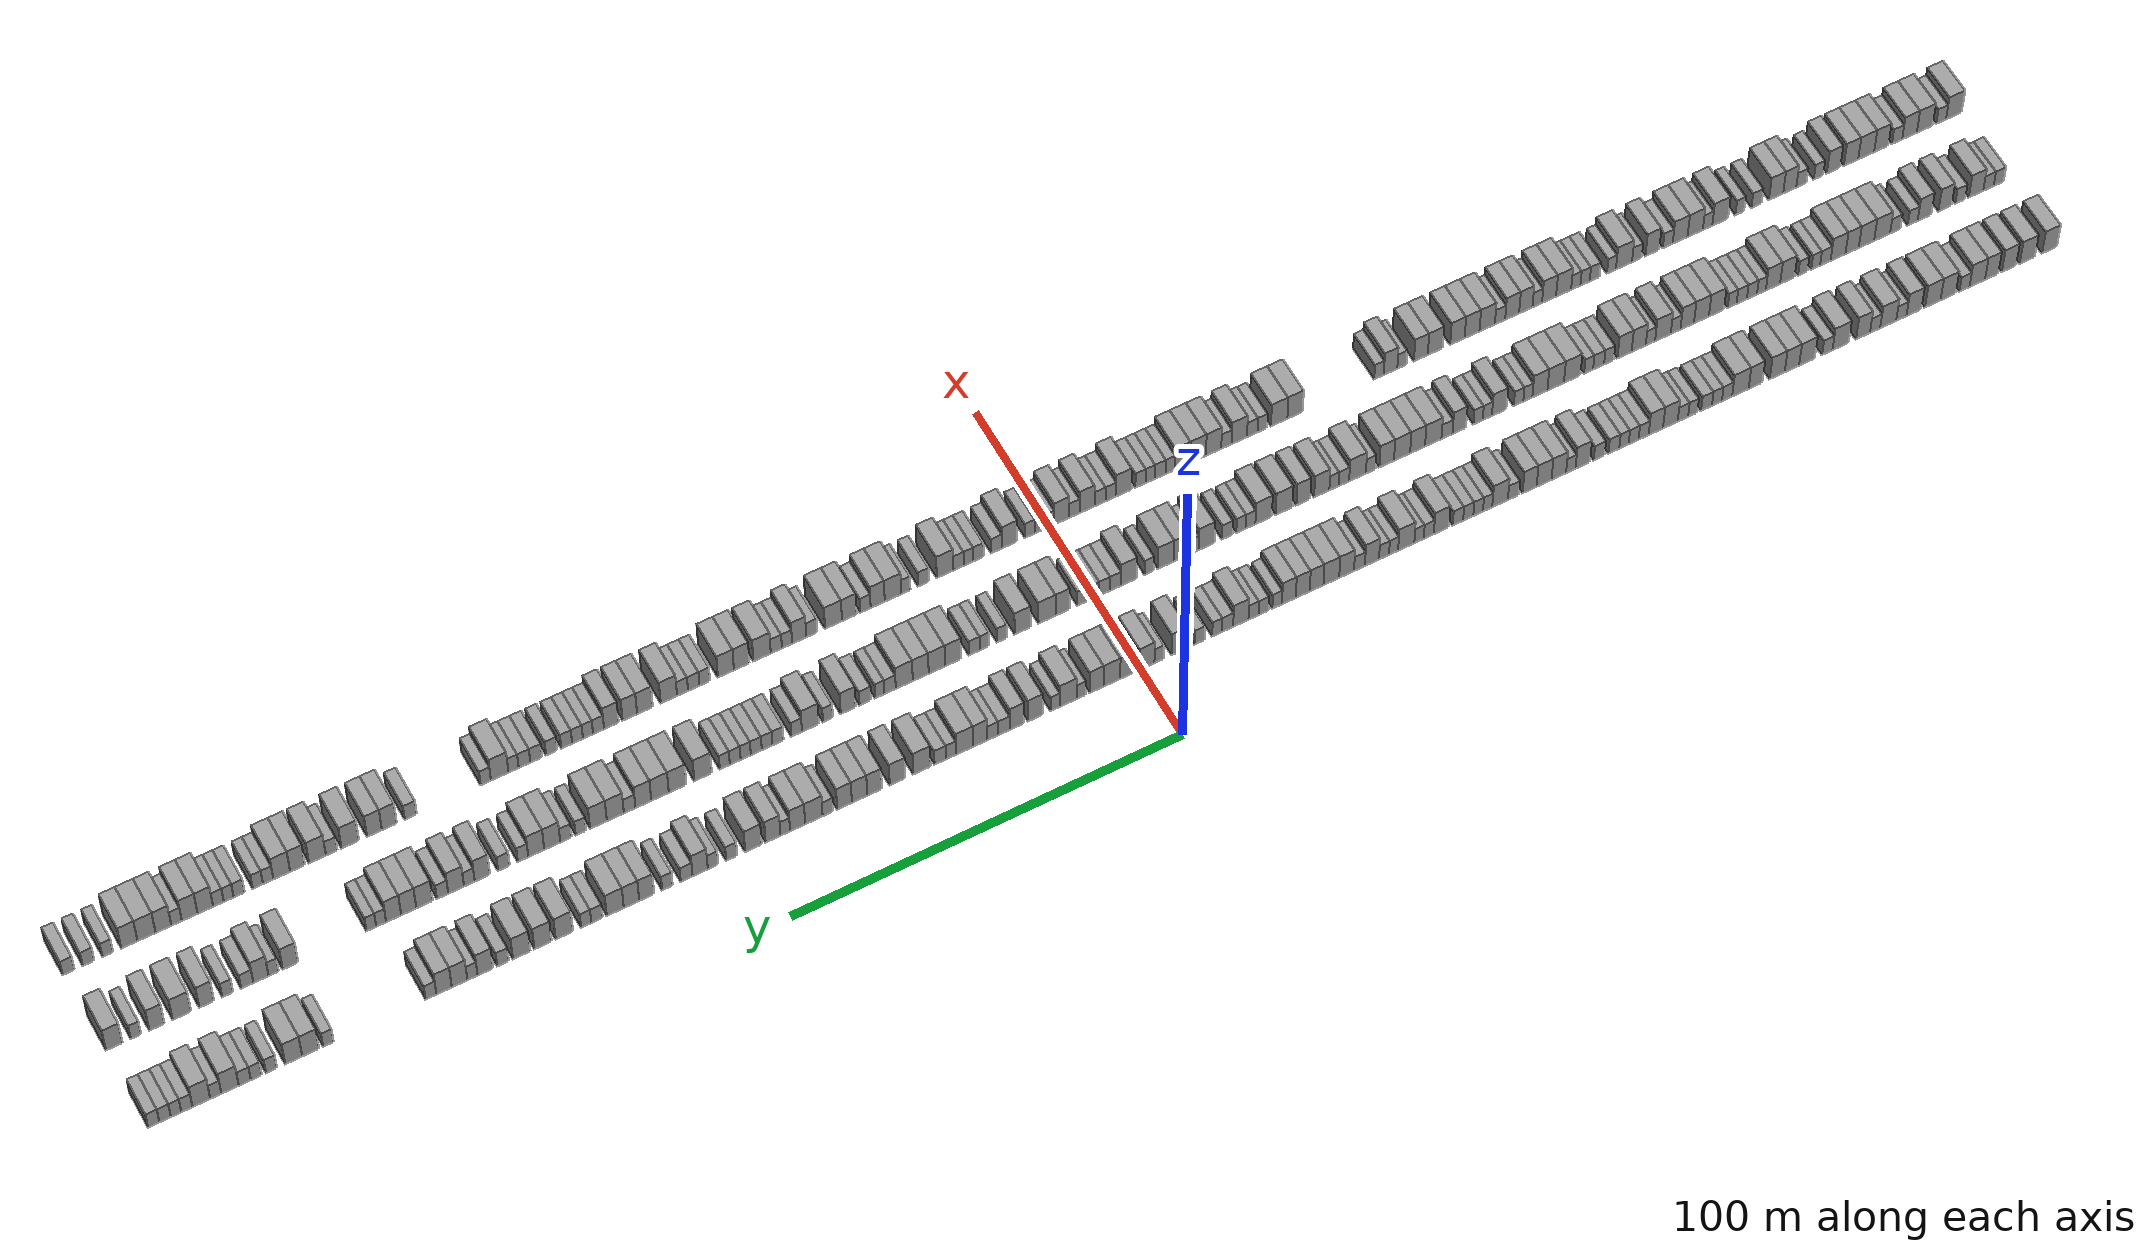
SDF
<sdf version="1.6">
 <world name="default">
  <scene>
   <sky><clouds><speed>12</speed></clouds></sky>
   <ambient>0.4 0.4 0.4 1</ambient>
   <background>0.7 0.7 0.7 1</background>
   <shadows>1</shadows>
  </scene>
  <gravity>0 0 -9.8066</gravity>
  <magnetic_field>6e-06 2.3e-05 -4.2e-05</magnetic_field>
  <physics default="0" name="default_physics" type="ode">
   <ode>
    <solver>
     <type>quick</type>
     <iters>10</iters>
     <sor>1.0</sor>
     <use_dynamic_moi_rescaling>0</use_dynamic_moi_rescaling>
    </solver>
    <constraints>
     <cfm>0</cfm>
     <erp>0.2</erp>
     <contact_max_correcting_vel>100</contact_max_correcting_vel>
     <contact_surface_layer>0.001</contact_surface_layer>
    </constraints>
   </ode>
   <max_step_size>0.004</max_step_size>
   <real_time_factor>1</real_time_factor>
   <real_time_update_rate>250</real_time_update_rate>
  </physics>
  <light name="sun" type="directional">
   <pose>0 0 10 0 0 0</pose>
   <diffuse>0.8 0.8 0.8 1</diffuse>
   <specular>0.2 0.2 0.2 1</specular>
   <attenuation>
    <range>1000</range>
    <constant>0.9</constant>
    <linear>0.01</linear>
    <quadratic>0.001</quadratic>
   </attenuation>
   <direction>-0.5 0.1 -0.9</direction>
  </light>
  <model name="building_1">
   <static>1</static>
   <pose>25.0000 -244.9082 0 0.000000 0.000000 0.000000</pose>
   <link name="link">
    <pose>0 0 4.50 0 0 0</pose>
    <collision name="collision"><geometry><box><size>10.0000 4.1835 9.0000</size></box></geometry></collision>
    <visual name="visual">
     <cast_shadows>0</cast_shadows>
     <geometry><box><size>10.0000 4.1835 9.0000</size></box></geometry>
     <material>
      <script>
       <uri>model://grey_wall/materials/scripts</uri>
       <uri>model://grey_wall/materials/textures</uri>
       <name>vrc/grey_wall</name>
      </script>
     </material>
    </visual>
   </link>
  </model>
  <model name="building_2">
   <static>1</static>
   <pose>25.0000 -238.6850 0 0.000000 0.000000 0.000000</pose>
   <link name="link">
    <pose>0 0 4.50 0 0 0</pose>
    <collision name="collision"><geometry><box><size>10.0000 4.2630 9.0000</size></box></geometry></collision>
    <visual name="visual">
     <cast_shadows>0</cast_shadows>
     <geometry><box><size>10.0000 4.2630 9.0000</size></box></geometry>
     <material>
      <script>
       <uri>model://grey_wall/materials/scripts</uri>
       <uri>model://grey_wall/materials/textures</uri>
       <name>vrc/grey_wall</name>
      </script>
     </material>
    </visual>
   </link>
  </model>
  <model name="building_3">
   <static>1</static>
   <pose>25.0000 -233.5706 0 0.000000 0.000000 0.000000</pose>
   <link name="link">
    <pose>0 0 4.50 0 0 0</pose>
    <collision name="collision"><geometry><box><size>10.0000 3.9658 9.0000</size></box></geometry></collision>
    <visual name="visual">
     <cast_shadows>0</cast_shadows>
     <geometry><box><size>10.0000 3.9658 9.0000</size></box></geometry>
     <material>
      <script>
       <uri>model://grey_wall/materials/scripts</uri>
       <uri>model://grey_wall/materials/textures</uri>
       <name>vrc/grey_wall</name>
      </script>
     </material>
    </visual>
   </link>
  </model>
  <model name="building_4">
   <static>1</static>
   <pose>25.0000 -228.7367 0 0.000000 0.000000 0.000000</pose>
   <link name="link">
    <pose>0 0 4.50 0 0 0</pose>
    <collision name="collision"><geometry><box><size>10.0000 3.7020 9.0000</size></box></geometry></collision>
    <visual name="visual">
     <cast_shadows>0</cast_shadows>
     <geometry><box><size>10.0000 3.7020 9.0000</size></box></geometry>
     <material>
      <script>
       <uri>model://grey_wall/materials/scripts</uri>
       <uri>model://grey_wall/materials/textures</uri>
       <name>vrc/grey_wall</name>
      </script>
     </material>
    </visual>
   </link>
  </model>
  <model name="building_5">
   <static>1</static>
   <pose>25.0000 -224.7353 0 0.000000 0.000000 0.000000</pose>
   <link name="link">
    <pose>0 0 4.50 0 0 0</pose>
    <collision name="collision"><geometry><box><size>10.0000 4.3007 9.0000</size></box></geometry></collision>
    <visual name="visual">
     <cast_shadows>0</cast_shadows>
     <geometry><box><size>10.0000 4.3007 9.0000</size></box></geometry>
     <material>
      <script>
       <uri>model://grey_wall/materials/scripts</uri>
       <uri>model://grey_wall/materials/textures</uri>
       <name>vrc/grey_wall</name>
      </script>
     </material>
    </visual>
   </link>
  </model>
  <model name="building_6">
   <static>1</static>
   <pose>25.0000 -221.1922 0 0.000000 0.000000 0.000000</pose>
   <link name="link">
    <pose>0 0 3.00 0 0 0</pose>
    <collision name="collision"><geometry><box><size>10.0000 2.7856 6.0000</size></box></geometry></collision>
    <visual name="visual">
     <cast_shadows>0</cast_shadows>
     <geometry><box><size>10.0000 2.7856 6.0000</size></box></geometry>
     <material>
      <script>
       <uri>model://grey_wall/materials/scripts</uri>
       <uri>model://grey_wall/materials/textures</uri>
       <name>vrc/grey_wall</name>
      </script>
     </material>
    </visual>
   </link>
  </model>
  <model name="building_7">
   <static>1</static>
   <pose>25.0000 -216.6792 0 0.000000 0.000000 0.000000</pose>
   <link name="link">
    <pose>0 0 4.50 0 0 0</pose>
    <collision name="collision"><geometry><box><size>10.0000 4.2403 9.0000</size></box></geometry></collision>
    <visual name="visual">
     <cast_shadows>0</cast_shadows>
     <geometry><box><size>10.0000 4.2403 9.0000</size></box></geometry>
     <material>
      <script>
       <uri>model://grey_wall/materials/scripts</uri>
       <uri>model://grey_wall/materials/textures</uri>
       <name>vrc/grey_wall</name>
      </script>
     </material>
    </visual>
   </link>
  </model>
  <model name="building_8">
   <static>1</static>
   <pose>25.0000 -212.3979 0 0.000000 0.000000 0.000000</pose>
   <link name="link">
    <pose>0 0 4.50 0 0 0</pose>
    <collision name="collision"><geometry><box><size>10.0000 4.3224 9.0000</size></box></geometry></collision>
    <visual name="visual">
     <cast_shadows>0</cast_shadows>
     <geometry><box><size>10.0000 4.3224 9.0000</size></box></geometry>
     <material>
      <script>
       <uri>model://grey_wall/materials/scripts</uri>
       <uri>model://grey_wall/materials/textures</uri>
       <name>vrc/grey_wall</name>
      </script>
     </material>
    </visual>
   </link>
  </model>
  <model name="building_9">
   <static>1</static>
   <pose>25.0000 -207.1791 0 0.000000 0.000000 0.000000</pose>
   <link name="link">
    <pose>0 0 4.50 0 0 0</pose>
    <collision name="collision"><geometry><box><size>10.0000 4.1153 9.0000</size></box></geometry></collision>
    <visual name="visual">
     <cast_shadows>0</cast_shadows>
     <geometry><box><size>10.0000 4.1153 9.0000</size></box></geometry>
     <material>
      <script>
       <uri>model://grey_wall/materials/scripts</uri>
       <uri>model://grey_wall/materials/textures</uri>
       <name>vrc/grey_wall</name>
      </script>
     </material>
    </visual>
   </link>
  </model>
  <model name="building_10">
   <static>1</static>
   <pose>25.0000 -203.7104 0 0.000000 0.000000 0.000000</pose>
   <link name="link">
    <pose>0 0 3.00 0 0 0</pose>
    <collision name="collision"><geometry><box><size>10.0000 2.8221 6.0000</size></box></geometry></collision>
    <visual name="visual">
     <cast_shadows>0</cast_shadows>
     <geometry><box><size>10.0000 2.8221 6.0000</size></box></geometry>
     <material>
      <script>
       <uri>model://grey_wall/materials/scripts</uri>
       <uri>model://grey_wall/materials/textures</uri>
       <name>vrc/grey_wall</name>
      </script>
     </material>
    </visual>
   </link>
  </model>
  <model name="building_11">
   <static>1</static>
   <pose>25.0000 -200.0836 0 0.000000 0.000000 0.000000</pose>
   <link name="link">
    <pose>0 0 4.50 0 0 0</pose>
    <collision name="collision"><geometry><box><size>10.0000 4.4316 9.0000</size></box></geometry></collision>
    <visual name="visual">
     <cast_shadows>0</cast_shadows>
     <geometry><box><size>10.0000 4.4316 9.0000</size></box></geometry>
     <material>
      <script>
       <uri>model://grey_wall/materials/scripts</uri>
       <uri>model://grey_wall/materials/textures</uri>
       <name>vrc/grey_wall</name>
      </script>
     </material>
    </visual>
   </link>
  </model>
  <model name="building_12">
   <static>1</static>
   <pose>25.0000 -196.4589 0 0.000000 0.000000 0.000000</pose>
   <link name="link">
    <pose>0 0 3.00 0 0 0</pose>
    <collision name="collision"><geometry><box><size>10.0000 2.8177 6.0000</size></box></geometry></collision>
    <visual name="visual">
     <cast_shadows>0</cast_shadows>
     <geometry><box><size>10.0000 2.8177 6.0000</size></box></geometry>
     <material>
      <script>
       <uri>model://grey_wall/materials/scripts</uri>
       <uri>model://grey_wall/materials/textures</uri>
       <name>vrc/grey_wall</name>
      </script>
     </material>
    </visual>
   </link>
  </model>
  <model name="building_13">
   <static>1</static>
   <pose>25.0000 -193.1327 0 0.000000 0.000000 0.000000</pose>
   <link name="link">
    <pose>0 0 4.50 0 0 0</pose>
    <collision name="collision"><geometry><box><size>10.0000 3.8347 9.0000</size></box></geometry></collision>
    <visual name="visual">
     <cast_shadows>0</cast_shadows>
     <geometry><box><size>10.0000 3.8347 9.0000</size></box></geometry>
     <material>
      <script>
       <uri>model://grey_wall/materials/scripts</uri>
       <uri>model://grey_wall/materials/textures</uri>
       <name>vrc/grey_wall</name>
      </script>
     </material>
    </visual>
   </link>
  </model>
  <model name="building_14">
   <static>1</static>
   <pose>25.0000 -186.9744 0 0.000000 0.000000 0.000000</pose>
   <link name="link">
    <pose>0 0 4.50 0 0 0</pose>
    <collision name="collision"><geometry><box><size>10.0000 4.4820 9.0000</size></box></geometry></collision>
    <visual name="visual">
     <cast_shadows>0</cast_shadows>
     <geometry><box><size>10.0000 4.4820 9.0000</size></box></geometry>
     <material>
      <script>
       <uri>model://grey_wall/materials/scripts</uri>
       <uri>model://grey_wall/materials/textures</uri>
       <name>vrc/grey_wall</name>
      </script>
     </material>
    </visual>
   </link>
  </model>
  <model name="building_15">
   <static>1</static>
   <pose>25.0000 -183.3123 0 0.000000 0.000000 0.000000</pose>
   <link name="link">
    <pose>0 0 3.00 0 0 0</pose>
    <collision name="collision"><geometry><box><size>10.0000 2.8422 6.0000</size></box></geometry></collision>
    <visual name="visual">
     <cast_shadows>0</cast_shadows>
     <geometry><box><size>10.0000 2.8422 6.0000</size></box></geometry>
     <material>
      <script>
       <uri>model://grey_wall/materials/scripts</uri>
       <uri>model://grey_wall/materials/textures</uri>
       <name>vrc/grey_wall</name>
      </script>
     </material>
    </visual>
   </link>
  </model>
  <model name="building_16">
   <static>1</static>
   <pose>25.0000 -177.7389 0 0.000000 0.000000 0.000000</pose>
   <link name="link">
    <pose>0 0 4.50 0 0 0</pose>
    <collision name="collision"><geometry><box><size>10.0000 4.3045 9.0000</size></box></geometry></collision>
    <visual name="visual">
     <cast_shadows>0</cast_shadows>
     <geometry><box><size>10.0000 4.3045 9.0000</size></box></geometry>
     <material>
      <script>
       <uri>model://grey_wall/materials/scripts</uri>
       <uri>model://grey_wall/materials/textures</uri>
       <name>vrc/grey_wall</name>
      </script>
     </material>
    </visual>
   </link>
  </model>
  <model name="building_17">
   <static>1</static>
   <pose>25.0000 -173.6084 0 0.000000 0.000000 0.000000</pose>
   <link name="link">
    <pose>0 0 4.50 0 0 0</pose>
    <collision name="collision"><geometry><box><size>10.0000 3.9565 9.0000</size></box></geometry></collision>
    <visual name="visual">
     <cast_shadows>0</cast_shadows>
     <geometry><box><size>10.0000 3.9565 9.0000</size></box></geometry>
     <material>
      <script>
       <uri>model://grey_wall/materials/scripts</uri>
       <uri>model://grey_wall/materials/textures</uri>
       <name>vrc/grey_wall</name>
      </script>
     </material>
    </visual>
   </link>
  </model>
  <model name="building_18">
   <static>1</static>
   <pose>25.0000 -169.5832 0 0.000000 0.000000 0.000000</pose>
   <link name="link">
    <pose>0 0 4.50 0 0 0</pose>
    <collision name="collision"><geometry><box><size>10.0000 4.0939 9.0000</size></box></geometry></collision>
    <visual name="visual">
     <cast_shadows>0</cast_shadows>
     <geometry><box><size>10.0000 4.0939 9.0000</size></box></geometry>
     <material>
      <script>
       <uri>model://grey_wall/materials/scripts</uri>
       <uri>model://grey_wall/materials/textures</uri>
       <name>vrc/grey_wall</name>
      </script>
     </material>
    </visual>
   </link>
  </model>
  <model name="building_19">
   <static>1</static>
   <pose>25.0000 -163.6562 0 0.000000 0.000000 0.000000</pose>
   <link name="link">
    <pose>0 0 4.50 0 0 0</pose>
    <collision name="collision"><geometry><box><size>10.0000 3.7602 9.0000</size></box></geometry></collision>
    <visual name="visual">
     <cast_shadows>0</cast_shadows>
     <geometry><box><size>10.0000 3.7602 9.0000</size></box></geometry>
     <material>
      <script>
       <uri>model://grey_wall/materials/scripts</uri>
       <uri>model://grey_wall/materials/textures</uri>
       <name>vrc/grey_wall</name>
      </script>
     </material>
    </visual>
   </link>
  </model>
  <model name="building_20">
   <static>1</static>
   <pose>25.0000 -159.5274 0 0.000000 0.000000 0.000000</pose>
   <link name="link">
    <pose>0 0 4.50 0 0 0</pose>
    <collision name="collision"><geometry><box><size>10.0000 4.4974 9.0000</size></box></geometry></collision>
    <visual name="visual">
     <cast_shadows>0</cast_shadows>
     <geometry><box><size>10.0000 4.4974 9.0000</size></box></geometry>
     <material>
      <script>
       <uri>model://grey_wall/materials/scripts</uri>
       <uri>model://grey_wall/materials/textures</uri>
       <name>vrc/grey_wall</name>
      </script>
     </material>
    </visual>
   </link>
  </model>
  <model name="building_21">
   <static>1</static>
   <pose>25.0000 -155.8811 0 0.000000 0.000000 0.000000</pose>
   <link name="link">
    <pose>0 0 3.00 0 0 0</pose>
    <collision name="collision"><geometry><box><size>10.0000 2.7952 6.0000</size></box></geometry></collision>
    <visual name="visual">
     <cast_shadows>0</cast_shadows>
     <geometry><box><size>10.0000 2.7952 6.0000</size></box></geometry>
     <material>
      <script>
       <uri>model://grey_wall/materials/scripts</uri>
       <uri>model://grey_wall/materials/textures</uri>
       <name>vrc/grey_wall</name>
      </script>
     </material>
    </visual>
   </link>
  </model>
  <model name="building_22">
   <static>1</static>
   <pose>25.0000 -153.1354 0 0.000000 0.000000 0.000000</pose>
   <link name="link">
    <pose>0 0 3.00 0 0 0</pose>
    <collision name="collision"><geometry><box><size>10.0000 2.6961 6.0000</size></box></geometry></collision>
    <visual name="visual">
     <cast_shadows>0</cast_shadows>
     <geometry><box><size>10.0000 2.6961 6.0000</size></box></geometry>
     <material>
      <script>
       <uri>model://grey_wall/materials/scripts</uri>
       <uri>model://grey_wall/materials/textures</uri>
       <name>vrc/grey_wall</name>
      </script>
     </material>
    </visual>
   </link>
  </model>
  <model name="building_23">
   <static>1</static>
   <pose>25.0000 -150.3138 0 0.000000 0.000000 0.000000</pose>
   <link name="link">
    <pose>0 0 3.00 0 0 0</pose>
    <collision name="collision"><geometry><box><size>10.0000 2.9470 6.0000</size></box></geometry></collision>
    <visual name="visual">
     <cast_shadows>0</cast_shadows>
     <geometry><box><size>10.0000 2.9470 6.0000</size></box></geometry>
     <material>
      <script>
       <uri>model://grey_wall/materials/scripts</uri>
       <uri>model://grey_wall/materials/textures</uri>
       <name>vrc/grey_wall</name>
      </script>
     </material>
    </visual>
   </link>
  </model>
  <model name="building_24">
   <static>1</static>
   <pose>25.0000 -146.5695 0 0.000000 0.000000 0.000000</pose>
   <link name="link">
    <pose>0 0 3.00 0 0 0</pose>
    <collision name="collision"><geometry><box><size>10.0000 2.5416 6.0000</size></box></geometry></collision>
    <visual name="visual">
     <cast_shadows>0</cast_shadows>
     <geometry><box><size>10.0000 2.5416 6.0000</size></box></geometry>
     <material>
      <script>
       <uri>model://grey_wall/materials/scripts</uri>
       <uri>model://grey_wall/materials/textures</uri>
       <name>vrc/grey_wall</name>
      </script>
     </material>
    </visual>
   </link>
  </model>
  <model name="building_25">
   <static>1</static>
   <pose>25.0000 -143.8819 0 0.000000 0.000000 0.000000</pose>
   <link name="link">
    <pose>0 0 3.00 0 0 0</pose>
    <collision name="collision"><geometry><box><size>10.0000 2.8336 6.0000</size></box></geometry></collision>
    <visual name="visual">
     <cast_shadows>0</cast_shadows>
     <geometry><box><size>10.0000 2.8336 6.0000</size></box></geometry>
     <material>
      <script>
       <uri>model://grey_wall/materials/scripts</uri>
       <uri>model://grey_wall/materials/textures</uri>
       <name>vrc/grey_wall</name>
      </script>
     </material>
    </visual>
   </link>
  </model>
  <model name="building_26">
   <static>1</static>
   <pose>25.0000 -140.4807 0 0.000000 0.000000 0.000000</pose>
   <link name="link">
    <pose>0 0 4.50 0 0 0</pose>
    <collision name="collision"><geometry><box><size>10.0000 3.9688 9.0000</size></box></geometry></collision>
    <visual name="visual">
     <cast_shadows>0</cast_shadows>
     <geometry><box><size>10.0000 3.9688 9.0000</size></box></geometry>
     <material>
      <script>
       <uri>model://grey_wall/materials/scripts</uri>
       <uri>model://grey_wall/materials/textures</uri>
       <name>vrc/grey_wall</name>
      </script>
     </material>
    </visual>
   </link>
  </model>
  <model name="building_27">
   <static>1</static>
   <pose>25.0000 -136.5511 0 0.000000 0.000000 0.000000</pose>
   <link name="link">
    <pose>0 0 4.50 0 0 0</pose>
    <collision name="collision"><geometry><box><size>10.0000 3.8904 9.0000</size></box></geometry></collision>
    <visual name="visual">
     <cast_shadows>0</cast_shadows>
     <geometry><box><size>10.0000 3.8904 9.0000</size></box></geometry>
     <material>
      <script>
       <uri>model://grey_wall/materials/scripts</uri>
       <uri>model://grey_wall/materials/textures</uri>
       <name>vrc/grey_wall</name>
      </script>
     </material>
    </visual>
   </link>
  </model>
  <model name="building_28">
   <static>1</static>
   <pose>25.0000 -133.2498 0 0.000000 0.000000 0.000000</pose>
   <link name="link">
    <pose>0 0 3.00 0 0 0</pose>
    <collision name="collision"><geometry><box><size>10.0000 2.7122 6.0000</size></box></geometry></collision>
    <visual name="visual">
     <cast_shadows>0</cast_shadows>
     <geometry><box><size>10.0000 2.7122 6.0000</size></box></geometry>
     <material>
      <script>
       <uri>model://grey_wall/materials/scripts</uri>
       <uri>model://grey_wall/materials/textures</uri>
       <name>vrc/grey_wall</name>
      </script>
     </material>
    </visual>
   </link>
  </model>
  <model name="building_29">
   <static>1</static>
   <pose>25.0000 -130.5531 0 0.000000 0.000000 0.000000</pose>
   <link name="link">
    <pose>0 0 3.00 0 0 0</pose>
    <collision name="collision"><geometry><box><size>10.0000 2.6812 6.0000</size></box></geometry></collision>
    <visual name="visual">
     <cast_shadows>0</cast_shadows>
     <geometry><box><size>10.0000 2.6812 6.0000</size></box></geometry>
     <material>
      <script>
       <uri>model://grey_wall/materials/scripts</uri>
       <uri>model://grey_wall/materials/textures</uri>
       <name>vrc/grey_wall</name>
      </script>
     </material>
    </visual>
   </link>
  </model>
  <model name="building_30">
   <static>1</static>
   <pose>25.0000 -127.9489 0 0.000000 0.000000 0.000000</pose>
   <link name="link">
    <pose>0 0 3.00 0 0 0</pose>
    <collision name="collision"><geometry><box><size>10.0000 2.5270 6.0000</size></box></geometry></collision>
    <visual name="visual">
     <cast_shadows>0</cast_shadows>
     <geometry><box><size>10.0000 2.5270 6.0000</size></box></geometry>
     <material>
      <script>
       <uri>model://grey_wall/materials/scripts</uri>
       <uri>model://grey_wall/materials/textures</uri>
       <name>vrc/grey_wall</name>
      </script>
     </material>
    </visual>
   </link>
  </model>
  <model name="building_31">
   <static>1</static>
   <pose>25.0000 -125.2089 0 0.000000 0.000000 0.000000</pose>
   <link name="link">
    <pose>0 0 3.00 0 0 0</pose>
    <collision name="collision"><geometry><box><size>10.0000 2.9530 6.0000</size></box></geometry></collision>
    <visual name="visual">
     <cast_shadows>0</cast_shadows>
     <geometry><box><size>10.0000 2.9530 6.0000</size></box></geometry>
     <material>
      <script>
       <uri>model://grey_wall/materials/scripts</uri>
       <uri>model://grey_wall/materials/textures</uri>
       <name>vrc/grey_wall</name>
      </script>
     </material>
    </visual>
   </link>
  </model>
  <model name="building_32">
   <static>1</static>
   <pose>25.0000 -121.2491 0 0.000000 0.000000 0.000000</pose>
   <link name="link">
    <pose>0 0 3.00 0 0 0</pose>
    <collision name="collision"><geometry><box><size>10.0000 2.9667 6.0000</size></box></geometry></collision>
    <visual name="visual">
     <cast_shadows>0</cast_shadows>
     <geometry><box><size>10.0000 2.9667 6.0000</size></box></geometry>
     <material>
      <script>
       <uri>model://grey_wall/materials/scripts</uri>
       <uri>model://grey_wall/materials/textures</uri>
       <name>vrc/grey_wall</name>
      </script>
     </material>
    </visual>
   </link>
  </model>
  <model name="building_33">
   <static>1</static>
   <pose>25.0000 -116.8174 0 0.000000 0.000000 0.000000</pose>
   <link name="link">
    <pose>0 0 4.50 0 0 0</pose>
    <collision name="collision"><geometry><box><size>10.0000 3.8967 9.0000</size></box></geometry></collision>
    <visual name="visual">
     <cast_shadows>0</cast_shadows>
     <geometry><box><size>10.0000 3.8967 9.0000</size></box></geometry>
     <material>
      <script>
       <uri>model://grey_wall/materials/scripts</uri>
       <uri>model://grey_wall/materials/textures</uri>
       <name>vrc/grey_wall</name>
      </script>
     </material>
    </visual>
   </link>
  </model>
  <model name="building_34">
   <static>1</static>
   <pose>25.0000 -113.5964 0 0.000000 0.000000 0.000000</pose>
   <link name="link">
    <pose>0 0 3.00 0 0 0</pose>
    <collision name="collision"><geometry><box><size>10.0000 2.5452 6.0000</size></box></geometry></collision>
    <visual name="visual">
     <cast_shadows>0</cast_shadows>
     <geometry><box><size>10.0000 2.5452 6.0000</size></box></geometry>
     <material>
      <script>
       <uri>model://grey_wall/materials/scripts</uri>
       <uri>model://grey_wall/materials/textures</uri>
       <name>vrc/grey_wall</name>
      </script>
     </material>
    </visual>
   </link>
  </model>
  <model name="building_35">
   <static>1</static>
   <pose>25.0000 -110.3677 0 0.000000 0.000000 0.000000</pose>
   <link name="link">
    <pose>0 0 4.50 0 0 0</pose>
    <collision name="collision"><geometry><box><size>10.0000 3.9122 9.0000</size></box></geometry></collision>
    <visual name="visual">
     <cast_shadows>0</cast_shadows>
     <geometry><box><size>10.0000 3.9122 9.0000</size></box></geometry>
     <material>
      <script>
       <uri>model://grey_wall/materials/scripts</uri>
       <uri>model://grey_wall/materials/textures</uri>
       <name>vrc/grey_wall</name>
      </script>
     </material>
    </visual>
   </link>
  </model>
  <model name="building_36">
   <static>1</static>
   <pose>25.0000 -106.4191 0 0.000000 0.000000 0.000000</pose>
   <link name="link">
    <pose>0 0 4.50 0 0 0</pose>
    <collision name="collision"><geometry><box><size>10.0000 3.9849 9.0000</size></box></geometry></collision>
    <visual name="visual">
     <cast_shadows>0</cast_shadows>
     <geometry><box><size>10.0000 3.9849 9.0000</size></box></geometry>
     <material>
      <script>
       <uri>model://grey_wall/materials/scripts</uri>
       <uri>model://grey_wall/materials/textures</uri>
       <name>vrc/grey_wall</name>
      </script>
     </material>
    </visual>
   </link>
  </model>
  <model name="building_37">
   <static>1</static>
   <pose>25.0000 -102.5497 0 0.000000 0.000000 0.000000</pose>
   <link name="link">
    <pose>0 0 4.50 0 0 0</pose>
    <collision name="collision"><geometry><box><size>10.0000 3.7540 9.0000</size></box></geometry></collision>
    <visual name="visual">
     <cast_shadows>0</cast_shadows>
     <geometry><box><size>10.0000 3.7540 9.0000</size></box></geometry>
     <material>
      <script>
       <uri>model://grey_wall/materials/scripts</uri>
       <uri>model://grey_wall/materials/textures</uri>
       <name>vrc/grey_wall</name>
      </script>
     </material>
    </visual>
   </link>
  </model>
  <model name="building_38">
   <static>1</static>
   <pose>25.0000 -98.1888 0 0.000000 0.000000 0.000000</pose>
   <link name="link">
    <pose>0 0 3.00 0 0 0</pose>
    <collision name="collision"><geometry><box><size>10.0000 2.9676 6.0000</size></box></geometry></collision>
    <visual name="visual">
     <cast_shadows>0</cast_shadows>
     <geometry><box><size>10.0000 2.9676 6.0000</size></box></geometry>
     <material>
      <script>
       <uri>model://grey_wall/materials/scripts</uri>
       <uri>model://grey_wall/materials/textures</uri>
       <name>vrc/grey_wall</name>
      </script>
     </material>
    </visual>
   </link>
  </model>
  <model name="building_39">
   <static>1</static>
   <pose>25.0000 -94.6192 0 0.000000 0.000000 0.000000</pose>
   <link name="link">
    <pose>0 0 4.50 0 0 0</pose>
    <collision name="collision"><geometry><box><size>10.0000 4.1716 9.0000</size></box></geometry></collision>
    <visual name="visual">
     <cast_shadows>0</cast_shadows>
     <geometry><box><size>10.0000 4.1716 9.0000</size></box></geometry>
     <material>
      <script>
       <uri>model://grey_wall/materials/scripts</uri>
       <uri>model://grey_wall/materials/textures</uri>
       <name>vrc/grey_wall</name>
      </script>
     </material>
    </visual>
   </link>
  </model>
  <model name="building_40">
   <static>1</static>
   <pose>25.0000 -91.2941 0 0.000000 0.000000 0.000000</pose>
   <link name="link">
    <pose>0 0 3.00 0 0 0</pose>
    <collision name="collision"><geometry><box><size>10.0000 2.4787 6.0000</size></box></geometry></collision>
    <visual name="visual">
     <cast_shadows>0</cast_shadows>
     <geometry><box><size>10.0000 2.4787 6.0000</size></box></geometry>
     <material>
      <script>
       <uri>model://grey_wall/materials/scripts</uri>
       <uri>model://grey_wall/materials/textures</uri>
       <name>vrc/grey_wall</name>
      </script>
     </material>
    </visual>
   </link>
  </model>
  <model name="building_41">
   <static>1</static>
   <pose>25.0000 -88.7697 0 0.000000 0.000000 0.000000</pose>
   <link name="link">
    <pose>0 0 3.00 0 0 0</pose>
    <collision name="collision"><geometry><box><size>10.0000 2.5702 6.0000</size></box></geometry></collision>
    <visual name="visual">
     <cast_shadows>0</cast_shadows>
     <geometry><box><size>10.0000 2.5702 6.0000</size></box></geometry>
     <material>
      <script>
       <uri>model://grey_wall/materials/scripts</uri>
       <uri>model://grey_wall/materials/textures</uri>
       <name>vrc/grey_wall</name>
      </script>
     </material>
    </visual>
   </link>
  </model>
  <model name="building_42">
   <static>1</static>
   <pose>25.0000 -86.1177 0 0.000000 0.000000 0.000000</pose>
   <link name="link">
    <pose>0 0 3.00 0 0 0</pose>
    <collision name="collision"><geometry><box><size>10.0000 2.7337 6.0000</size></box></geometry></collision>
    <visual name="visual">
     <cast_shadows>0</cast_shadows>
     <geometry><box><size>10.0000 2.7337 6.0000</size></box></geometry>
     <material>
      <script>
       <uri>model://grey_wall/materials/scripts</uri>
       <uri>model://grey_wall/materials/textures</uri>
       <name>vrc/grey_wall</name>
      </script>
     </material>
    </visual>
   </link>
  </model>
  <model name="building_43">
   <static>1</static>
   <pose>25.0000 -83.3711 0 0.000000 0.000000 0.000000</pose>
   <link name="link">
    <pose>0 0 3.00 0 0 0</pose>
    <collision name="collision"><geometry><box><size>10.0000 2.7595 6.0000</size></box></geometry></collision>
    <visual name="visual">
     <cast_shadows>0</cast_shadows>
     <geometry><box><size>10.0000 2.7595 6.0000</size></box></geometry>
     <material>
      <script>
       <uri>model://grey_wall/materials/scripts</uri>
       <uri>model://grey_wall/materials/textures</uri>
       <name>vrc/grey_wall</name>
      </script>
     </material>
    </visual>
   </link>
  </model>
  <model name="building_44">
   <static>1</static>
   <pose>25.0000 -78.9670 0 0.000000 0.000000 0.000000</pose>
   <link name="link">
    <pose>0 0 4.50 0 0 0</pose>
    <collision name="collision"><geometry><box><size>10.0000 4.0487 9.0000</size></box></geometry></collision>
    <visual name="visual">
     <cast_shadows>0</cast_shadows>
     <geometry><box><size>10.0000 4.0487 9.0000</size></box></geometry>
     <material>
      <script>
       <uri>model://grey_wall/materials/scripts</uri>
       <uri>model://grey_wall/materials/textures</uri>
       <name>vrc/grey_wall</name>
      </script>
     </material>
    </visual>
   </link>
  </model>
  <model name="building_45">
   <static>1</static>
   <pose>25.0000 -75.6088 0 0.000000 0.000000 0.000000</pose>
   <link name="link">
    <pose>0 0 3.00 0 0 0</pose>
    <collision name="collision"><geometry><box><size>10.0000 2.6677 6.0000</size></box></geometry></collision>
    <visual name="visual">
     <cast_shadows>0</cast_shadows>
     <geometry><box><size>10.0000 2.6677 6.0000</size></box></geometry>
     <material>
      <script>
       <uri>model://grey_wall/materials/scripts</uri>
       <uri>model://grey_wall/materials/textures</uri>
       <name>vrc/grey_wall</name>
      </script>
     </material>
    </visual>
   </link>
  </model>
  <model name="building_46">
   <static>1</static>
   <pose>25.0000 -73.0191 0 0.000000 0.000000 0.000000</pose>
   <link name="link">
    <pose>0 0 3.00 0 0 0</pose>
    <collision name="collision"><geometry><box><size>10.0000 2.5119 6.0000</size></box></geometry></collision>
    <visual name="visual">
     <cast_shadows>0</cast_shadows>
     <geometry><box><size>10.0000 2.5119 6.0000</size></box></geometry>
     <material>
      <script>
       <uri>model://grey_wall/materials/scripts</uri>
       <uri>model://grey_wall/materials/textures</uri>
       <name>vrc/grey_wall</name>
      </script>
     </material>
    </visual>
   </link>
  </model>
  <model name="building_47">
   <static>1</static>
   <pose>25.0000 -69.6125 0 0.000000 0.000000 0.000000</pose>
   <link name="link">
    <pose>0 0 4.50 0 0 0</pose>
    <collision name="collision"><geometry><box><size>10.0000 4.3013 9.0000</size></box></geometry></collision>
    <visual name="visual">
     <cast_shadows>0</cast_shadows>
     <geometry><box><size>10.0000 4.3013 9.0000</size></box></geometry>
     <material>
      <script>
       <uri>model://grey_wall/materials/scripts</uri>
       <uri>model://grey_wall/materials/textures</uri>
       <name>vrc/grey_wall</name>
      </script>
     </material>
    </visual>
   </link>
  </model>
  <model name="building_48">
   <static>1</static>
   <pose>25.0000 -66.2549 0 0.000000 0.000000 0.000000</pose>
   <link name="link">
    <pose>0 0 3.00 0 0 0</pose>
    <collision name="collision"><geometry><box><size>10.0000 2.4138 6.0000</size></box></geometry></collision>
    <visual name="visual">
     <cast_shadows>0</cast_shadows>
     <geometry><box><size>10.0000 2.4138 6.0000</size></box></geometry>
     <material>
      <script>
       <uri>model://grey_wall/materials/scripts</uri>
       <uri>model://grey_wall/materials/textures</uri>
       <name>vrc/grey_wall</name>
      </script>
     </material>
    </visual>
   </link>
  </model>
  <model name="building_49">
   <static>1</static>
   <pose>25.0000 -63.7254 0 0.000000 0.000000 0.000000</pose>
   <link name="link">
    <pose>0 0 3.00 0 0 0</pose>
    <collision name="collision"><geometry><box><size>10.0000 2.6452 6.0000</size></box></geometry></collision>
    <visual name="visual">
     <cast_shadows>0</cast_shadows>
     <geometry><box><size>10.0000 2.6452 6.0000</size></box></geometry>
     <material>
      <script>
       <uri>model://grey_wall/materials/scripts</uri>
       <uri>model://grey_wall/materials/textures</uri>
       <name>vrc/grey_wall</name>
      </script>
     </material>
    </visual>
   </link>
  </model>
  <model name="building_50">
   <static>1</static>
   <pose>25.0000 -60.5292 0 0.000000 0.000000 0.000000</pose>
   <link name="link">
    <pose>0 0 4.50 0 0 0</pose>
    <collision name="collision"><geometry><box><size>10.0000 3.7474 9.0000</size></box></geometry></collision>
    <visual name="visual">
     <cast_shadows>0</cast_shadows>
     <geometry><box><size>10.0000 3.7474 9.0000</size></box></geometry>
     <material>
      <script>
       <uri>model://grey_wall/materials/scripts</uri>
       <uri>model://grey_wall/materials/textures</uri>
       <name>vrc/grey_wall</name>
      </script>
     </material>
    </visual>
   </link>
  </model>
  <model name="building_51">
   <static>1</static>
   <pose>25.0000 -57.2158 0 0.000000 0.000000 0.000000</pose>
   <link name="link">
    <pose>0 0 3.00 0 0 0</pose>
    <collision name="collision"><geometry><box><size>10.0000 2.8793 6.0000</size></box></geometry></collision>
    <visual name="visual">
     <cast_shadows>0</cast_shadows>
     <geometry><box><size>10.0000 2.8793 6.0000</size></box></geometry>
     <material>
      <script>
       <uri>model://grey_wall/materials/scripts</uri>
       <uri>model://grey_wall/materials/textures</uri>
       <name>vrc/grey_wall</name>
      </script>
     </material>
    </visual>
   </link>
  </model>
  <model name="building_52">
   <static>1</static>
   <pose>25.0000 -53.8270 0 0.000000 0.000000 0.000000</pose>
   <link name="link">
    <pose>0 0 4.50 0 0 0</pose>
    <collision name="collision"><geometry><box><size>10.0000 3.8983 9.0000</size></box></geometry></collision>
    <visual name="visual">
     <cast_shadows>0</cast_shadows>
     <geometry><box><size>10.0000 3.8983 9.0000</size></box></geometry>
     <material>
      <script>
       <uri>model://grey_wall/materials/scripts</uri>
       <uri>model://grey_wall/materials/textures</uri>
       <name>vrc/grey_wall</name>
      </script>
     </material>
    </visual>
   </link>
  </model>
  <model name="building_53">
   <static>1</static>
   <pose>25.0000 -49.7944 0 0.000000 0.000000 0.000000</pose>
   <link name="link">
    <pose>0 0 4.50 0 0 0</pose>
    <collision name="collision"><geometry><box><size>10.0000 4.1670 9.0000</size></box></geometry></collision>
    <visual name="visual">
     <cast_shadows>0</cast_shadows>
     <geometry><box><size>10.0000 4.1670 9.0000</size></box></geometry>
     <material>
      <script>
       <uri>model://grey_wall/materials/scripts</uri>
       <uri>model://grey_wall/materials/textures</uri>
       <name>vrc/grey_wall</name>
      </script>
     </material>
    </visual>
   </link>
  </model>
  <model name="building_54">
   <static>1</static>
   <pose>25.0000 -45.9077 0 0.000000 0.000000 0.000000</pose>
   <link name="link">
    <pose>0 0 4.50 0 0 0</pose>
    <collision name="collision"><geometry><box><size>10.0000 3.6064 9.0000</size></box></geometry></collision>
    <visual name="visual">
     <cast_shadows>0</cast_shadows>
     <geometry><box><size>10.0000 3.6064 9.0000</size></box></geometry>
     <material>
      <script>
       <uri>model://grey_wall/materials/scripts</uri>
       <uri>model://grey_wall/materials/textures</uri>
       <name>vrc/grey_wall</name>
      </script>
     </material>
    </visual>
   </link>
  </model>
  <model name="building_55">
   <static>1</static>
   <pose>25.0000 -42.2686 0 0.000000 0.000000 0.000000</pose>
   <link name="link">
    <pose>0 0 4.50 0 0 0</pose>
    <collision name="collision"><geometry><box><size>10.0000 3.6719 9.0000</size></box></geometry></collision>
    <visual name="visual">
     <cast_shadows>0</cast_shadows>
     <geometry><box><size>10.0000 3.6719 9.0000</size></box></geometry>
     <material>
      <script>
       <uri>model://grey_wall/materials/scripts</uri>
       <uri>model://grey_wall/materials/textures</uri>
       <name>vrc/grey_wall</name>
      </script>
     </material>
    </visual>
   </link>
  </model>
  <model name="building_56">
   <static>1</static>
   <pose>25.0000 -38.6117 0 0.000000 0.000000 0.000000</pose>
   <link name="link">
    <pose>0 0 4.50 0 0 0</pose>
    <collision name="collision"><geometry><box><size>10.0000 3.6418 9.0000</size></box></geometry></collision>
    <visual name="visual">
     <cast_shadows>0</cast_shadows>
     <geometry><box><size>10.0000 3.6418 9.0000</size></box></geometry>
     <material>
      <script>
       <uri>model://grey_wall/materials/scripts</uri>
       <uri>model://grey_wall/materials/textures</uri>
       <name>vrc/grey_wall</name>
      </script>
     </material>
    </visual>
   </link>
  </model>
  <model name="building_57">
   <static>1</static>
   <pose>25.0000 -35.5270 0 0.000000 0.000000 0.000000</pose>
   <link name="link">
    <pose>0 0 3.00 0 0 0</pose>
    <collision name="collision"><geometry><box><size>10.0000 2.5277 6.0000</size></box></geometry></collision>
    <visual name="visual">
     <cast_shadows>0</cast_shadows>
     <geometry><box><size>10.0000 2.5277 6.0000</size></box></geometry>
     <material>
      <script>
       <uri>model://grey_wall/materials/scripts</uri>
       <uri>model://grey_wall/materials/textures</uri>
       <name>vrc/grey_wall</name>
      </script>
     </material>
    </visual>
   </link>
  </model>
  <model name="building_58">
   <static>1</static>
   <pose>25.0000 -31.9532 0 0.000000 0.000000 0.000000</pose>
   <link name="link">
    <pose>0 0 3.00 0 0 0</pose>
    <collision name="collision"><geometry><box><size>10.0000 2.6199 6.0000</size></box></geometry></collision>
    <visual name="visual">
     <cast_shadows>0</cast_shadows>
     <geometry><box><size>10.0000 2.6199 6.0000</size></box></geometry>
     <material>
      <script>
       <uri>model://grey_wall/materials/scripts</uri>
       <uri>model://grey_wall/materials/textures</uri>
       <name>vrc/grey_wall</name>
      </script>
     </material>
    </visual>
   </link>
  </model>
  <model name="building_59">
   <static>1</static>
   <pose>25.0000 -29.3172 0 0.000000 0.000000 0.000000</pose>
   <link name="link">
    <pose>0 0 3.00 0 0 0</pose>
    <collision name="collision"><geometry><box><size>10.0000 2.6520 6.0000</size></box></geometry></collision>
    <visual name="visual">
     <cast_shadows>0</cast_shadows>
     <geometry><box><size>10.0000 2.6520 6.0000</size></box></geometry>
     <material>
      <script>
       <uri>model://grey_wall/materials/scripts</uri>
       <uri>model://grey_wall/materials/textures</uri>
       <name>vrc/grey_wall</name>
      </script>
     </material>
    </visual>
   </link>
  </model>
  <model name="building_60">
   <static>1</static>
   <pose>25.0000 -25.9939 0 0.000000 0.000000 0.000000</pose>
   <link name="link">
    <pose>0 0 4.50 0 0 0</pose>
    <collision name="collision"><geometry><box><size>10.0000 3.9946 9.0000</size></box></geometry></collision>
    <visual name="visual">
     <cast_shadows>0</cast_shadows>
     <geometry><box><size>10.0000 3.9946 9.0000</size></box></geometry>
     <material>
      <script>
       <uri>model://grey_wall/materials/scripts</uri>
       <uri>model://grey_wall/materials/textures</uri>
       <name>vrc/grey_wall</name>
      </script>
     </material>
    </visual>
   </link>
  </model>
  <model name="building_61">
   <static>1</static>
   <pose>25.0000 -22.5409 0 0.000000 0.000000 0.000000</pose>
   <link name="link">
    <pose>0 0 3.00 0 0 0</pose>
    <collision name="collision"><geometry><box><size>10.0000 2.9115 6.0000</size></box></geometry></collision>
    <visual name="visual">
     <cast_shadows>0</cast_shadows>
     <geometry><box><size>10.0000 2.9115 6.0000</size></box></geometry>
     <material>
      <script>
       <uri>model://grey_wall/materials/scripts</uri>
       <uri>model://grey_wall/materials/textures</uri>
       <name>vrc/grey_wall</name>
      </script>
     </material>
    </visual>
   </link>
  </model>
  <model name="building_62">
   <static>1</static>
   <pose>25.0000 -19.7989 0 0.000000 0.000000 0.000000</pose>
   <link name="link">
    <pose>0 0 3.00 0 0 0</pose>
    <collision name="collision"><geometry><box><size>10.0000 2.5723 6.0000</size></box></geometry></collision>
    <visual name="visual">
     <cast_shadows>0</cast_shadows>
     <geometry><box><size>10.0000 2.5723 6.0000</size></box></geometry>
     <material>
      <script>
       <uri>model://grey_wall/materials/scripts</uri>
       <uri>model://grey_wall/materials/textures</uri>
       <name>vrc/grey_wall</name>
      </script>
     </material>
    </visual>
   </link>
  </model>
  <model name="building_63">
   <static>1</static>
   <pose>25.0000 -15.2357 0 0.000000 0.000000 0.000000</pose>
   <link name="link">
    <pose>0 0 3.00 0 0 0</pose>
    <collision name="collision"><geometry><box><size>10.0000 2.5540 6.0000</size></box></geometry></collision>
    <visual name="visual">
     <cast_shadows>0</cast_shadows>
     <geometry><box><size>10.0000 2.5540 6.0000</size></box></geometry>
     <material>
      <script>
       <uri>model://grey_wall/materials/scripts</uri>
       <uri>model://grey_wall/materials/textures</uri>
       <name>vrc/grey_wall</name>
      </script>
     </material>
    </visual>
   </link>
  </model>
  <model name="building_64">
   <static>1</static>
   <pose>25.0000 -9.9495 0 0.000000 0.000000 0.000000</pose>
   <link name="link">
    <pose>0 0 4.50 0 0 0</pose>
    <collision name="collision"><geometry><box><size>10.0000 4.0184 9.0000</size></box></geometry></collision>
    <visual name="visual">
     <cast_shadows>0</cast_shadows>
     <geometry><box><size>10.0000 4.0184 9.0000</size></box></geometry>
     <material>
      <script>
       <uri>model://grey_wall/materials/scripts</uri>
       <uri>model://grey_wall/materials/textures</uri>
       <name>vrc/grey_wall</name>
      </script>
     </material>
    </visual>
   </link>
  </model>
  <model name="building_65">
   <static>1</static>
   <pose>25.0000 -4.6840 0 0.000000 0.000000 0.000000</pose>
   <link name="link">
    <pose>0 0 3.00 0 0 0</pose>
    <collision name="collision"><geometry><box><size>10.0000 2.5126 6.0000</size></box></geometry></collision>
    <visual name="visual">
     <cast_shadows>0</cast_shadows>
     <geometry><box><size>10.0000 2.5126 6.0000</size></box></geometry>
     <material>
      <script>
       <uri>model://grey_wall/materials/scripts</uri>
       <uri>model://grey_wall/materials/textures</uri>
       <name>vrc/grey_wall</name>
      </script>
     </material>
    </visual>
   </link>
  </model>
  <model name="building_66">
   <static>1</static>
   <pose>25.0000 -1.4756 0 0.000000 0.000000 0.000000</pose>
   <link name="link">
    <pose>0 0 4.50 0 0 0</pose>
    <collision name="collision"><geometry><box><size>10.0000 3.9042 9.0000</size></box></geometry></collision>
    <visual name="visual">
     <cast_shadows>0</cast_shadows>
     <geometry><box><size>10.0000 3.9042 9.0000</size></box></geometry>
     <material>
      <script>
       <uri>model://grey_wall/materials/scripts</uri>
       <uri>model://grey_wall/materials/textures</uri>
       <name>vrc/grey_wall</name>
      </script>
     </material>
    </visual>
   </link>
  </model>
  <model name="building_67">
   <static>1</static>
   <pose>25.0000 3.4564 0 0.000000 0.000000 0.000000</pose>
   <link name="link">
    <pose>0 0 4.50 0 0 0</pose>
    <collision name="collision"><geometry><box><size>10.0000 3.9598 9.0000</size></box></geometry></collision>
    <visual name="visual">
     <cast_shadows>0</cast_shadows>
     <geometry><box><size>10.0000 3.9598 9.0000</size></box></geometry>
     <material>
      <script>
       <uri>model://grey_wall/materials/scripts</uri>
       <uri>model://grey_wall/materials/textures</uri>
       <name>vrc/grey_wall</name>
      </script>
     </material>
    </visual>
   </link>
  </model>
  <model name="building_68">
   <static>1</static>
   <pose>25.0000 7.5896 0 0.000000 0.000000 0.000000</pose>
   <link name="link">
    <pose>0 0 4.50 0 0 0</pose>
    <collision name="collision"><geometry><box><size>10.0000 4.3065 9.0000</size></box></geometry></collision>
    <visual name="visual">
     <cast_shadows>0</cast_shadows>
     <geometry><box><size>10.0000 4.3065 9.0000</size></box></geometry>
     <material>
      <script>
       <uri>model://grey_wall/materials/scripts</uri>
       <uri>model://grey_wall/materials/textures</uri>
       <name>vrc/grey_wall</name>
      </script>
     </material>
    </visual>
   </link>
  </model>
  <model name="building_69">
   <static>1</static>
   <pose>25.0000 11.5523 0 0.000000 0.000000 0.000000</pose>
   <link name="link">
    <pose>0 0 4.50 0 0 0</pose>
    <collision name="collision"><geometry><box><size>10.0000 3.6191 9.0000</size></box></geometry></collision>
    <visual name="visual">
     <cast_shadows>0</cast_shadows>
     <geometry><box><size>10.0000 3.6191 9.0000</size></box></geometry>
     <material>
      <script>
       <uri>model://grey_wall/materials/scripts</uri>
       <uri>model://grey_wall/materials/textures</uri>
       <name>vrc/grey_wall</name>
      </script>
     </material>
    </visual>
   </link>
  </model>
  <model name="building_70">
   <static>1</static>
   <pose>25.0000 15.5752 0 0.000000 0.000000 0.000000</pose>
   <link name="link">
    <pose>0 0 3.00 0 0 0</pose>
    <collision name="collision"><geometry><box><size>10.0000 2.4266 6.0000</size></box></geometry></collision>
    <visual name="visual">
     <cast_shadows>0</cast_shadows>
     <geometry><box><size>10.0000 2.4266 6.0000</size></box></geometry>
     <material>
      <script>
       <uri>model://grey_wall/materials/scripts</uri>
       <uri>model://grey_wall/materials/textures</uri>
       <name>vrc/grey_wall</name>
      </script>
     </material>
    </visual>
   </link>
  </model>
  <model name="building_71">
   <static>1</static>
   <pose>25.0000 18.9392 0 0.000000 0.000000 0.000000</pose>
   <link name="link">
    <pose>0 0 4.50 0 0 0</pose>
    <collision name="collision"><geometry><box><size>10.0000 4.3015 9.0000</size></box></geometry></collision>
    <visual name="visual">
     <cast_shadows>0</cast_shadows>
     <geometry><box><size>10.0000 4.3015 9.0000</size></box></geometry>
     <material>
      <script>
       <uri>model://grey_wall/materials/scripts</uri>
       <uri>model://grey_wall/materials/textures</uri>
       <name>vrc/grey_wall</name>
      </script>
     </material>
    </visual>
   </link>
  </model>
  <model name="building_72">
   <static>1</static>
   <pose>25.0000 22.2941 0 0.000000 0.000000 0.000000</pose>
   <link name="link">
    <pose>0 0 3.00 0 0 0</pose>
    <collision name="collision"><geometry><box><size>10.0000 2.4084 6.0000</size></box></geometry></collision>
    <visual name="visual">
     <cast_shadows>0</cast_shadows>
     <geometry><box><size>10.0000 2.4084 6.0000</size></box></geometry>
     <material>
      <script>
       <uri>model://grey_wall/materials/scripts</uri>
       <uri>model://grey_wall/materials/textures</uri>
       <name>vrc/grey_wall</name>
      </script>
     </material>
    </visual>
   </link>
  </model>
  <model name="building_73">
   <static>1</static>
   <pose>25.0000 27.3943 0 0.000000 0.000000 0.000000</pose>
   <link name="link">
    <pose>0 0 4.50 0 0 0</pose>
    <collision name="collision"><geometry><box><size>10.0000 3.7920 9.0000</size></box></geometry></collision>
    <visual name="visual">
     <cast_shadows>0</cast_shadows>
     <geometry><box><size>10.0000 3.7920 9.0000</size></box></geometry>
     <material>
      <script>
       <uri>model://grey_wall/materials/scripts</uri>
       <uri>model://grey_wall/materials/textures</uri>
       <name>vrc/grey_wall</name>
      </script>
     </material>
    </visual>
   </link>
  </model>
  <model name="building_74">
   <static>1</static>
   <pose>25.0000 32.1384 0 0.000000 0.000000 0.000000</pose>
   <link name="link">
    <pose>0 0 4.50 0 0 0</pose>
    <collision name="collision"><geometry><box><size>10.0000 3.6961 9.0000</size></box></geometry></collision>
    <visual name="visual">
     <cast_shadows>0</cast_shadows>
     <geometry><box><size>10.0000 3.6961 9.0000</size></box></geometry>
     <material>
      <script>
       <uri>model://grey_wall/materials/scripts</uri>
       <uri>model://grey_wall/materials/textures</uri>
       <name>vrc/grey_wall</name>
      </script>
     </material>
    </visual>
   </link>
  </model>
  <model name="building_75">
   <static>1</static>
   <pose>25.0000 35.4859 0 0.000000 0.000000 0.000000</pose>
   <link name="link">
    <pose>0 0 3.00 0 0 0</pose>
    <collision name="collision"><geometry><box><size>10.0000 2.9990 6.0000</size></box></geometry></collision>
    <visual name="visual">
     <cast_shadows>0</cast_shadows>
     <geometry><box><size>10.0000 2.9990 6.0000</size></box></geometry>
     <material>
      <script>
       <uri>model://grey_wall/materials/scripts</uri>
       <uri>model://grey_wall/materials/textures</uri>
       <name>vrc/grey_wall</name>
      </script>
     </material>
    </visual>
   </link>
  </model>
  <model name="building_76">
   <static>1</static>
   <pose>25.0000 38.3679 0 0.000000 0.000000 0.000000</pose>
   <link name="link">
    <pose>0 0 3.00 0 0 0</pose>
    <collision name="collision"><geometry><box><size>10.0000 2.7649 6.0000</size></box></geometry></collision>
    <visual name="visual">
     <cast_shadows>0</cast_shadows>
     <geometry><box><size>10.0000 2.7649 6.0000</size></box></geometry>
     <material>
      <script>
       <uri>model://grey_wall/materials/scripts</uri>
       <uri>model://grey_wall/materials/textures</uri>
       <name>vrc/grey_wall</name>
      </script>
     </material>
    </visual>
   </link>
  </model>
  <model name="building_77">
   <static>1</static>
   <pose>25.0000 41.5709 0 0.000000 0.000000 0.000000</pose>
   <link name="link">
    <pose>0 0 4.50 0 0 0</pose>
    <collision name="collision"><geometry><box><size>10.0000 3.6411 9.0000</size></box></geometry></collision>
    <visual name="visual">
     <cast_shadows>0</cast_shadows>
     <geometry><box><size>10.0000 3.6411 9.0000</size></box></geometry>
     <material>
      <script>
       <uri>model://grey_wall/materials/scripts</uri>
       <uri>model://grey_wall/materials/textures</uri>
       <name>vrc/grey_wall</name>
      </script>
     </material>
    </visual>
   </link>
  </model>
  <model name="building_78">
   <static>1</static>
   <pose>25.0000 45.6113 0 0.000000 0.000000 0.000000</pose>
   <link name="link">
    <pose>0 0 4.50 0 0 0</pose>
    <collision name="collision"><geometry><box><size>10.0000 4.4396 9.0000</size></box></geometry></collision>
    <visual name="visual">
     <cast_shadows>0</cast_shadows>
     <geometry><box><size>10.0000 4.4396 9.0000</size></box></geometry>
     <material>
      <script>
       <uri>model://grey_wall/materials/scripts</uri>
       <uri>model://grey_wall/materials/textures</uri>
       <name>vrc/grey_wall</name>
      </script>
     </material>
    </visual>
   </link>
  </model>
  <model name="building_79">
   <static>1</static>
   <pose>25.0000 49.1122 0 0.000000 0.000000 0.000000</pose>
   <link name="link">
    <pose>0 0 3.00 0 0 0</pose>
    <collision name="collision"><geometry><box><size>10.0000 2.5622 6.0000</size></box></geometry></collision>
    <visual name="visual">
     <cast_shadows>0</cast_shadows>
     <geometry><box><size>10.0000 2.5622 6.0000</size></box></geometry>
     <material>
      <script>
       <uri>model://grey_wall/materials/scripts</uri>
       <uri>model://grey_wall/materials/textures</uri>
       <name>vrc/grey_wall</name>
      </script>
     </material>
    </visual>
   </link>
  </model>
  <model name="building_80">
   <static>1</static>
   <pose>25.0000 51.8571 0 0.000000 0.000000 0.000000</pose>
   <link name="link">
    <pose>0 0 3.00 0 0 0</pose>
    <collision name="collision"><geometry><box><size>10.0000 2.9275 6.0000</size></box></geometry></collision>
    <visual name="visual">
     <cast_shadows>0</cast_shadows>
     <geometry><box><size>10.0000 2.9275 6.0000</size></box></geometry>
     <material>
      <script>
       <uri>model://grey_wall/materials/scripts</uri>
       <uri>model://grey_wall/materials/textures</uri>
       <name>vrc/grey_wall</name>
      </script>
     </material>
    </visual>
   </link>
  </model>
  <model name="building_81">
   <static>1</static>
   <pose>25.0000 56.5417 0 0.000000 0.000000 0.000000</pose>
   <link name="link">
    <pose>0 0 4.50 0 0 0</pose>
    <collision name="collision"><geometry><box><size>10.0000 4.4417 9.0000</size></box></geometry></collision>
    <visual name="visual">
     <cast_shadows>0</cast_shadows>
     <geometry><box><size>10.0000 4.4417 9.0000</size></box></geometry>
     <material>
      <script>
       <uri>model://grey_wall/materials/scripts</uri>
       <uri>model://grey_wall/materials/textures</uri>
       <name>vrc/grey_wall</name>
      </script>
     </material>
    </visual>
   </link>
  </model>
  <model name="building_82">
   <static>1</static>
   <pose>25.0000 62.7658 0 0.000000 0.000000 0.000000</pose>
   <link name="link">
    <pose>0 0 4.50 0 0 0</pose>
    <collision name="collision"><geometry><box><size>10.0000 4.0066 9.0000</size></box></geometry></collision>
    <visual name="visual">
     <cast_shadows>0</cast_shadows>
     <geometry><box><size>10.0000 4.0066 9.0000</size></box></geometry>
     <material>
      <script>
       <uri>model://grey_wall/materials/scripts</uri>
       <uri>model://grey_wall/materials/textures</uri>
       <name>vrc/grey_wall</name>
      </script>
     </material>
    </visual>
   </link>
  </model>
  <model name="building_83">
   <static>1</static>
   <pose>25.0000 68.6392 0 0.000000 0.000000 0.000000</pose>
   <link name="link">
    <pose>0 0 4.50 0 0 0</pose>
    <collision name="collision"><geometry><box><size>10.0000 3.7401 9.0000</size></box></geometry></collision>
    <visual name="visual">
     <cast_shadows>0</cast_shadows>
     <geometry><box><size>10.0000 3.7401 9.0000</size></box></geometry>
     <material>
      <script>
       <uri>model://grey_wall/materials/scripts</uri>
       <uri>model://grey_wall/materials/textures</uri>
       <name>vrc/grey_wall</name>
      </script>
     </material>
    </visual>
   </link>
  </model>
  <model name="building_84">
   <static>1</static>
   <pose>25.0000 72.4593 0 0.000000 0.000000 0.000000</pose>
   <link name="link">
    <pose>0 0 4.50 0 0 0</pose>
    <collision name="collision"><geometry><box><size>10.0000 3.9002 9.0000</size></box></geometry></collision>
    <visual name="visual">
     <cast_shadows>0</cast_shadows>
     <geometry><box><size>10.0000 3.9002 9.0000</size></box></geometry>
     <material>
      <script>
       <uri>model://grey_wall/materials/scripts</uri>
       <uri>model://grey_wall/materials/textures</uri>
       <name>vrc/grey_wall</name>
      </script>
     </material>
    </visual>
   </link>
  </model>
  <model name="building_85">
   <static>1</static>
   <pose>25.0000 76.2775 0 0.000000 0.000000 0.000000</pose>
   <link name="link">
    <pose>0 0 4.50 0 0 0</pose>
    <collision name="collision"><geometry><box><size>10.0000 3.7361 9.0000</size></box></geometry></collision>
    <visual name="visual">
     <cast_shadows>0</cast_shadows>
     <geometry><box><size>10.0000 3.7361 9.0000</size></box></geometry>
     <material>
      <script>
       <uri>model://grey_wall/materials/scripts</uri>
       <uri>model://grey_wall/materials/textures</uri>
       <name>vrc/grey_wall</name>
      </script>
     </material>
    </visual>
   </link>
  </model>
  <model name="building_86">
   <static>1</static>
   <pose>25.0000 80.4934 0 0.000000 0.000000 0.000000</pose>
   <link name="link">
    <pose>0 0 3.00 0 0 0</pose>
    <collision name="collision"><geometry><box><size>10.0000 2.6956 6.0000</size></box></geometry></collision>
    <visual name="visual">
     <cast_shadows>0</cast_shadows>
     <geometry><box><size>10.0000 2.6956 6.0000</size></box></geometry>
     <material>
      <script>
       <uri>model://grey_wall/materials/scripts</uri>
       <uri>model://grey_wall/materials/textures</uri>
       <name>vrc/grey_wall</name>
      </script>
     </material>
    </visual>
   </link>
  </model>
  <model name="building_87">
   <static>1</static>
   <pose>25.0000 84.0499 0 0.000000 0.000000 0.000000</pose>
   <link name="link">
    <pose>0 0 4.50 0 0 0</pose>
    <collision name="collision"><geometry><box><size>10.0000 4.4173 9.0000</size></box></geometry></collision>
    <visual name="visual">
     <cast_shadows>0</cast_shadows>
     <geometry><box><size>10.0000 4.4173 9.0000</size></box></geometry>
     <material>
      <script>
       <uri>model://grey_wall/materials/scripts</uri>
       <uri>model://grey_wall/materials/textures</uri>
       <name>vrc/grey_wall</name>
      </script>
     </material>
    </visual>
   </link>
  </model>
  <model name="building_88">
   <static>1</static>
   <pose>25.0000 88.1691 0 0.000000 0.000000 0.000000</pose>
   <link name="link">
    <pose>0 0 4.50 0 0 0</pose>
    <collision name="collision"><geometry><box><size>10.0000 3.8210 9.0000</size></box></geometry></collision>
    <visual name="visual">
     <cast_shadows>0</cast_shadows>
     <geometry><box><size>10.0000 3.8210 9.0000</size></box></geometry>
     <material>
      <script>
       <uri>model://grey_wall/materials/scripts</uri>
       <uri>model://grey_wall/materials/textures</uri>
       <name>vrc/grey_wall</name>
      </script>
     </material>
    </visual>
   </link>
  </model>
  <model name="building_89">
   <static>1</static>
   <pose>25.0000 91.2960 0 0.000000 0.000000 0.000000</pose>
   <link name="link">
    <pose>0 0 3.00 0 0 0</pose>
    <collision name="collision"><geometry><box><size>10.0000 2.4328 6.0000</size></box></geometry></collision>
    <visual name="visual">
     <cast_shadows>0</cast_shadows>
     <geometry><box><size>10.0000 2.4328 6.0000</size></box></geometry>
     <material>
      <script>
       <uri>model://grey_wall/materials/scripts</uri>
       <uri>model://grey_wall/materials/textures</uri>
       <name>vrc/grey_wall</name>
      </script>
     </material>
    </visual>
   </link>
  </model>
  <model name="building_90">
   <static>1</static>
   <pose>25.0000 94.3941 0 0.000000 0.000000 0.000000</pose>
   <link name="link">
    <pose>0 0 4.50 0 0 0</pose>
    <collision name="collision"><geometry><box><size>10.0000 3.7634 9.0000</size></box></geometry></collision>
    <visual name="visual">
     <cast_shadows>0</cast_shadows>
     <geometry><box><size>10.0000 3.7634 9.0000</size></box></geometry>
     <material>
      <script>
       <uri>model://grey_wall/materials/scripts</uri>
       <uri>model://grey_wall/materials/textures</uri>
       <name>vrc/grey_wall</name>
      </script>
     </material>
    </visual>
   </link>
  </model>
  <model name="building_91">
   <static>1</static>
   <pose>25.0000 99.3492 0 0.000000 0.000000 0.000000</pose>
   <link name="link">
    <pose>0 0 4.50 0 0 0</pose>
    <collision name="collision"><geometry><box><size>10.0000 4.1468 9.0000</size></box></geometry></collision>
    <visual name="visual">
     <cast_shadows>0</cast_shadows>
     <geometry><box><size>10.0000 4.1468 9.0000</size></box></geometry>
     <material>
      <script>
       <uri>model://grey_wall/materials/scripts</uri>
       <uri>model://grey_wall/materials/textures</uri>
       <name>vrc/grey_wall</name>
      </script>
     </material>
    </visual>
   </link>
  </model>
  <model name="building_92">
   <static>1</static>
   <pose>25.0000 104.8178 0 0.000000 0.000000 0.000000</pose>
   <link name="link">
    <pose>0 0 3.00 0 0 0</pose>
    <collision name="collision"><geometry><box><size>10.0000 2.7903 6.0000</size></box></geometry></collision>
    <visual name="visual">
     <cast_shadows>0</cast_shadows>
     <geometry><box><size>10.0000 2.7903 6.0000</size></box></geometry>
     <material>
      <script>
       <uri>model://grey_wall/materials/scripts</uri>
       <uri>model://grey_wall/materials/textures</uri>
       <name>vrc/grey_wall</name>
      </script>
     </material>
    </visual>
   </link>
  </model>
  <model name="building_93">
   <static>1</static>
   <pose>25.0000 109.5246 0 0.000000 0.000000 0.000000</pose>
   <link name="link">
    <pose>0 0 3.00 0 0 0</pose>
    <collision name="collision"><geometry><box><size>10.0000 2.6234 6.0000</size></box></geometry></collision>
    <visual name="visual">
     <cast_shadows>0</cast_shadows>
     <geometry><box><size>10.0000 2.6234 6.0000</size></box></geometry>
     <material>
      <script>
       <uri>model://grey_wall/materials/scripts</uri>
       <uri>model://grey_wall/materials/textures</uri>
       <name>vrc/grey_wall</name>
      </script>
     </material>
    </visual>
   </link>
  </model>
  <model name="building_94">
   <static>1</static>
   <pose>25.0000 112.7478 0 0.000000 0.000000 0.000000</pose>
   <link name="link">
    <pose>0 0 4.50 0 0 0</pose>
    <collision name="collision"><geometry><box><size>10.0000 3.8230 9.0000</size></box></geometry></collision>
    <visual name="visual">
     <cast_shadows>0</cast_shadows>
     <geometry><box><size>10.0000 3.8230 9.0000</size></box></geometry>
     <material>
      <script>
       <uri>model://grey_wall/materials/scripts</uri>
       <uri>model://grey_wall/materials/textures</uri>
       <name>vrc/grey_wall</name>
      </script>
     </material>
    </visual>
   </link>
  </model>
  <model name="building_95">
   <static>1</static>
   <pose>25.0000 116.1501 0 0.000000 0.000000 0.000000</pose>
   <link name="link">
    <pose>0 0 3.00 0 0 0</pose>
    <collision name="collision"><geometry><box><size>10.0000 2.9815 6.0000</size></box></geometry></collision>
    <visual name="visual">
     <cast_shadows>0</cast_shadows>
     <geometry><box><size>10.0000 2.9815 6.0000</size></box></geometry>
     <material>
      <script>
       <uri>model://grey_wall/materials/scripts</uri>
       <uri>model://grey_wall/materials/textures</uri>
       <name>vrc/grey_wall</name>
      </script>
     </material>
    </visual>
   </link>
  </model>
  <model name="building_96">
   <static>1</static>
   <pose>25.0000 120.9619 0 0.000000 0.000000 0.000000</pose>
   <link name="link">
    <pose>0 0 3.00 0 0 0</pose>
    <collision name="collision"><geometry><box><size>10.0000 2.6422 6.0000</size></box></geometry></collision>
    <visual name="visual">
     <cast_shadows>0</cast_shadows>
     <geometry><box><size>10.0000 2.6422 6.0000</size></box></geometry>
     <material>
      <script>
       <uri>model://grey_wall/materials/scripts</uri>
       <uri>model://grey_wall/materials/textures</uri>
       <name>vrc/grey_wall</name>
      </script>
     </material>
    </visual>
   </link>
  </model>
  <model name="building_97">
   <static>1</static>
   <pose>25.0000 126.1494 0 0.000000 0.000000 0.000000</pose>
   <link name="link">
    <pose>0 0 4.50 0 0 0</pose>
    <collision name="collision"><geometry><box><size>10.0000 3.7326 9.0000</size></box></geometry></collision>
    <visual name="visual">
     <cast_shadows>0</cast_shadows>
     <geometry><box><size>10.0000 3.7326 9.0000</size></box></geometry>
     <material>
      <script>
       <uri>model://grey_wall/materials/scripts</uri>
       <uri>model://grey_wall/materials/textures</uri>
       <name>vrc/grey_wall</name>
      </script>
     </material>
    </visual>
   </link>
  </model>
  <model name="building_98">
   <static>1</static>
   <pose>25.0000 129.9535 0 0.000000 0.000000 0.000000</pose>
   <link name="link">
    <pose>0 0 4.50 0 0 0</pose>
    <collision name="collision"><geometry><box><size>10.0000 3.8756 9.0000</size></box></geometry></collision>
    <visual name="visual">
     <cast_shadows>0</cast_shadows>
     <geometry><box><size>10.0000 3.8756 9.0000</size></box></geometry>
     <material>
      <script>
       <uri>model://grey_wall/materials/scripts</uri>
       <uri>model://grey_wall/materials/textures</uri>
       <name>vrc/grey_wall</name>
      </script>
     </material>
    </visual>
   </link>
  </model>
  <model name="building_99">
   <static>1</static>
   <pose>25.0000 134.0172 0 0.000000 0.000000 0.000000</pose>
   <link name="link">
    <pose>0 0 4.50 0 0 0</pose>
    <collision name="collision"><geometry><box><size>10.0000 4.2518 9.0000</size></box></geometry></collision>
    <visual name="visual">
     <cast_shadows>0</cast_shadows>
     <geometry><box><size>10.0000 4.2518 9.0000</size></box></geometry>
     <material>
      <script>
       <uri>model://grey_wall/materials/scripts</uri>
       <uri>model://grey_wall/materials/textures</uri>
       <name>vrc/grey_wall</name>
      </script>
     </material>
    </visual>
   </link>
  </model>
  <model name="building_100">
   <static>1</static>
   <pose>25.0000 138.5593 0 0.000000 0.000000 0.000000</pose>
   <link name="link">
    <pose>0 0 3.00 0 0 0</pose>
    <collision name="collision"><geometry><box><size>10.0000 2.8324 6.0000</size></box></geometry></collision>
    <visual name="visual">
     <cast_shadows>0</cast_shadows>
     <geometry><box><size>10.0000 2.8324 6.0000</size></box></geometry>
     <material>
      <script>
       <uri>model://grey_wall/materials/scripts</uri>
       <uri>model://grey_wall/materials/textures</uri>
       <name>vrc/grey_wall</name>
      </script>
     </material>
    </visual>
   </link>
  </model>
  <model name="building_101">
   <static>1</static>
   <pose>25.0000 141.2569 0 0.000000 0.000000 0.000000</pose>
   <link name="link">
    <pose>0 0 3.00 0 0 0</pose>
    <collision name="collision"><geometry><box><size>10.0000 2.5628 6.0000</size></box></geometry></collision>
    <visual name="visual">
     <cast_shadows>0</cast_shadows>
     <geometry><box><size>10.0000 2.5628 6.0000</size></box></geometry>
     <material>
      <script>
       <uri>model://grey_wall/materials/scripts</uri>
       <uri>model://grey_wall/materials/textures</uri>
       <name>vrc/grey_wall</name>
      </script>
     </material>
    </visual>
   </link>
  </model>
  <model name="building_102">
   <static>1</static>
   <pose>25.0000 146.6880 0 0.000000 0.000000 0.000000</pose>
   <link name="link">
    <pose>0 0 4.50 0 0 0</pose>
    <collision name="collision"><geometry><box><size>10.0000 4.2995 9.0000</size></box></geometry></collision>
    <visual name="visual">
     <cast_shadows>0</cast_shadows>
     <geometry><box><size>10.0000 4.2995 9.0000</size></box></geometry>
     <material>
      <script>
       <uri>model://grey_wall/materials/scripts</uri>
       <uri>model://grey_wall/materials/textures</uri>
       <name>vrc/grey_wall</name>
      </script>
     </material>
    </visual>
   </link>
  </model>
  <model name="building_103">
   <static>1</static>
   <pose>25.0000 151.9792 0 0.000000 0.000000 0.000000</pose>
   <link name="link">
    <pose>0 0 4.50 0 0 0</pose>
    <collision name="collision"><geometry><box><size>10.0000 4.2827 9.0000</size></box></geometry></collision>
    <visual name="visual">
     <cast_shadows>0</cast_shadows>
     <geometry><box><size>10.0000 4.2827 9.0000</size></box></geometry>
     <material>
      <script>
       <uri>model://grey_wall/materials/scripts</uri>
       <uri>model://grey_wall/materials/textures</uri>
       <name>vrc/grey_wall</name>
      </script>
     </material>
    </visual>
   </link>
  </model>
  <model name="building_104">
   <static>1</static>
   <pose>25.0000 157.2899 0 0.000000 0.000000 0.000000</pose>
   <link name="link">
    <pose>0 0 4.50 0 0 0</pose>
    <collision name="collision"><geometry><box><size>10.0000 4.3387 9.0000</size></box></geometry></collision>
    <visual name="visual">
     <cast_shadows>0</cast_shadows>
     <geometry><box><size>10.0000 4.3387 9.0000</size></box></geometry>
     <material>
      <script>
       <uri>model://grey_wall/materials/scripts</uri>
       <uri>model://grey_wall/materials/textures</uri>
       <name>vrc/grey_wall</name>
      </script>
     </material>
    </visual>
   </link>
  </model>
  <model name="building_105">
   <static>1</static>
   <pose>25.0000 161.8982 0 0.000000 0.000000 0.000000</pose>
   <link name="link">
    <pose>0 0 3.00 0 0 0</pose>
    <collision name="collision"><geometry><box><size>10.0000 2.8780 6.0000</size></box></geometry></collision>
    <visual name="visual">
     <cast_shadows>0</cast_shadows>
     <geometry><box><size>10.0000 2.8780 6.0000</size></box></geometry>
     <material>
      <script>
       <uri>model://grey_wall/materials/scripts</uri>
       <uri>model://grey_wall/materials/textures</uri>
       <name>vrc/grey_wall</name>
      </script>
     </material>
    </visual>
   </link>
  </model>
  <model name="building_106">
   <static>1</static>
   <pose>25.0000 166.2672 0 0.000000 0.000000 0.000000</pose>
   <link name="link">
    <pose>0 0 4.50 0 0 0</pose>
    <collision name="collision"><geometry><box><size>10.0000 3.8599 9.0000</size></box></geometry></collision>
    <visual name="visual">
     <cast_shadows>0</cast_shadows>
     <geometry><box><size>10.0000 3.8599 9.0000</size></box></geometry>
     <material>
      <script>
       <uri>model://grey_wall/materials/scripts</uri>
       <uri>model://grey_wall/materials/textures</uri>
       <name>vrc/grey_wall</name>
      </script>
     </material>
    </visual>
   </link>
  </model>
  <model name="building_107">
   <static>1</static>
   <pose>25.0000 169.4553 0 0.000000 0.000000 0.000000</pose>
   <link name="link">
    <pose>0 0 3.00 0 0 0</pose>
    <collision name="collision"><geometry><box><size>10.0000 2.5162 6.0000</size></box></geometry></collision>
    <visual name="visual">
     <cast_shadows>0</cast_shadows>
     <geometry><box><size>10.0000 2.5162 6.0000</size></box></geometry>
     <material>
      <script>
       <uri>model://grey_wall/materials/scripts</uri>
       <uri>model://grey_wall/materials/textures</uri>
       <name>vrc/grey_wall</name>
      </script>
     </material>
    </visual>
   </link>
  </model>
  <model name="building_108">
   <static>1</static>
   <pose>25.0000 172.6331 0 0.000000 0.000000 0.000000</pose>
   <link name="link">
    <pose>0 0 4.50 0 0 0</pose>
    <collision name="collision"><geometry><box><size>10.0000 3.8395 9.0000</size></box></geometry></collision>
    <visual name="visual">
     <cast_shadows>0</cast_shadows>
     <geometry><box><size>10.0000 3.8395 9.0000</size></box></geometry>
     <material>
      <script>
       <uri>model://grey_wall/materials/scripts</uri>
       <uri>model://grey_wall/materials/textures</uri>
       <name>vrc/grey_wall</name>
      </script>
     </material>
    </visual>
   </link>
  </model>
  <model name="building_109">
   <static>1</static>
   <pose>25.0000 176.4520 0 0.000000 0.000000 0.000000</pose>
   <link name="link">
    <pose>0 0 4.50 0 0 0</pose>
    <collision name="collision"><geometry><box><size>10.0000 3.7984 9.0000</size></box></geometry></collision>
    <visual name="visual">
     <cast_shadows>0</cast_shadows>
     <geometry><box><size>10.0000 3.7984 9.0000</size></box></geometry>
     <material>
      <script>
       <uri>model://grey_wall/materials/scripts</uri>
       <uri>model://grey_wall/materials/textures</uri>
       <name>vrc/grey_wall</name>
      </script>
     </material>
    </visual>
   </link>
  </model>
  <model name="building_110">
   <static>1</static>
   <pose>25.0000 179.6811 0 0.000000 0.000000 0.000000</pose>
   <link name="link">
    <pose>0 0 3.00 0 0 0</pose>
    <collision name="collision"><geometry><box><size>10.0000 2.6598 6.0000</size></box></geometry></collision>
    <visual name="visual">
     <cast_shadows>0</cast_shadows>
     <geometry><box><size>10.0000 2.6598 6.0000</size></box></geometry>
     <material>
      <script>
       <uri>model://grey_wall/materials/scripts</uri>
       <uri>model://grey_wall/materials/textures</uri>
       <name>vrc/grey_wall</name>
      </script>
     </material>
    </visual>
   </link>
  </model>
  <model name="building_111">
   <static>1</static>
   <pose>25.0000 204.8555 0 0.000000 0.000000 0.000000</pose>
   <link name="link">
    <pose>0 0 3.00 0 0 0</pose>
    <collision name="collision"><geometry><box><size>10.0000 2.5630 6.0000</size></box></geometry></collision>
    <visual name="visual">
     <cast_shadows>0</cast_shadows>
     <geometry><box><size>10.0000 2.5630 6.0000</size></box></geometry>
     <material>
      <script>
       <uri>model://grey_wall/materials/scripts</uri>
       <uri>model://grey_wall/materials/textures</uri>
       <name>vrc/grey_wall</name>
      </script>
     </material>
    </visual>
   </link>
  </model>
  <model name="building_112">
   <static>1</static>
   <pose>25.0000 209.1923 0 0.000000 0.000000 0.000000</pose>
   <link name="link">
    <pose>0 0 4.50 0 0 0</pose>
    <collision name="collision"><geometry><box><size>10.0000 4.1105 9.0000</size></box></geometry></collision>
    <visual name="visual">
     <cast_shadows>0</cast_shadows>
     <geometry><box><size>10.0000 4.1105 9.0000</size></box></geometry>
     <material>
      <script>
       <uri>model://grey_wall/materials/scripts</uri>
       <uri>model://grey_wall/materials/textures</uri>
       <name>vrc/grey_wall</name>
      </script>
     </material>
    </visual>
   </link>
  </model>
  <model name="building_113">
   <static>1</static>
   <pose>25.0000 213.3170 0 0.000000 0.000000 0.000000</pose>
   <link name="link">
    <pose>0 0 4.50 0 0 0</pose>
    <collision name="collision"><geometry><box><size>10.0000 4.1390 9.0000</size></box></geometry></collision>
    <visual name="visual">
     <cast_shadows>0</cast_shadows>
     <geometry><box><size>10.0000 4.1390 9.0000</size></box></geometry>
     <material>
      <script>
       <uri>model://grey_wall/materials/scripts</uri>
       <uri>model://grey_wall/materials/textures</uri>
       <name>vrc/grey_wall</name>
      </script>
     </material>
    </visual>
   </link>
  </model>
  <model name="building_114">
   <static>1</static>
   <pose>25.0000 218.7199 0 0.000000 0.000000 0.000000</pose>
   <link name="link">
    <pose>0 0 3.00 0 0 0</pose>
    <collision name="collision"><geometry><box><size>10.0000 2.6667 6.0000</size></box></geometry></collision>
    <visual name="visual">
     <cast_shadows>0</cast_shadows>
     <geometry><box><size>10.0000 2.6667 6.0000</size></box></geometry>
     <material>
      <script>
       <uri>model://grey_wall/materials/scripts</uri>
       <uri>model://grey_wall/materials/textures</uri>
       <name>vrc/grey_wall</name>
      </script>
     </material>
    </visual>
   </link>
  </model>
  <model name="building_115">
   <static>1</static>
   <pose>25.0000 222.4004 0 0.000000 0.000000 0.000000</pose>
   <link name="link">
    <pose>0 0 3.00 0 0 0</pose>
    <collision name="collision"><geometry><box><size>10.0000 2.6942 6.0000</size></box></geometry></collision>
    <visual name="visual">
     <cast_shadows>0</cast_shadows>
     <geometry><box><size>10.0000 2.6942 6.0000</size></box></geometry>
     <material>
      <script>
       <uri>model://grey_wall/materials/scripts</uri>
       <uri>model://grey_wall/materials/textures</uri>
       <name>vrc/grey_wall</name>
      </script>
     </material>
    </visual>
   </link>
  </model>
  <model name="building_116">
   <static>1</static>
   <pose>25.0000 225.2044 0 0.000000 0.000000 0.000000</pose>
   <link name="link">
    <pose>0 0 3.00 0 0 0</pose>
    <collision name="collision"><geometry><box><size>10.0000 2.9139 6.0000</size></box></geometry></collision>
    <visual name="visual">
     <cast_shadows>0</cast_shadows>
     <geometry><box><size>10.0000 2.9139 6.0000</size></box></geometry>
     <material>
      <script>
       <uri>model://grey_wall/materials/scripts</uri>
       <uri>model://grey_wall/materials/textures</uri>
       <name>vrc/grey_wall</name>
      </script>
     </material>
    </visual>
   </link>
  </model>
  <model name="building_117">
   <static>1</static>
   <pose>25.0000 228.7733 0 0.000000 0.000000 0.000000</pose>
   <link name="link">
    <pose>0 0 4.50 0 0 0</pose>
    <collision name="collision"><geometry><box><size>10.0000 4.2240 9.0000</size></box></geometry></collision>
    <visual name="visual">
     <cast_shadows>0</cast_shadows>
     <geometry><box><size>10.0000 4.2240 9.0000</size></box></geometry>
     <material>
      <script>
       <uri>model://grey_wall/materials/scripts</uri>
       <uri>model://grey_wall/materials/textures</uri>
       <name>vrc/grey_wall</name>
      </script>
     </material>
    </visual>
   </link>
  </model>
  <model name="building_118">
   <static>1</static>
   <pose>25.0000 232.2210 0 0.000000 0.000000 0.000000</pose>
   <link name="link">
    <pose>0 0 3.00 0 0 0</pose>
    <collision name="collision"><geometry><box><size>10.0000 2.6713 6.0000</size></box></geometry></collision>
    <visual name="visual">
     <cast_shadows>0</cast_shadows>
     <geometry><box><size>10.0000 2.6713 6.0000</size></box></geometry>
     <material>
      <script>
       <uri>model://grey_wall/materials/scripts</uri>
       <uri>model://grey_wall/materials/textures</uri>
       <name>vrc/grey_wall</name>
      </script>
     </material>
    </visual>
   </link>
  </model>
  <model name="building_119">
   <static>1</static>
   <pose>25.0000 235.7053 0 0.000000 0.000000 0.000000</pose>
   <link name="link">
    <pose>0 0 4.50 0 0 0</pose>
    <collision name="collision"><geometry><box><size>10.0000 4.2974 9.0000</size></box></geometry></collision>
    <visual name="visual">
     <cast_shadows>0</cast_shadows>
     <geometry><box><size>10.0000 4.2974 9.0000</size></box></geometry>
     <material>
      <script>
       <uri>model://grey_wall/materials/scripts</uri>
       <uri>model://grey_wall/materials/textures</uri>
       <name>vrc/grey_wall</name>
      </script>
     </material>
    </visual>
   </link>
  </model>
  <model name="building_120">
   <static>1</static>
   <pose>25.0000 239.2014 0 0.000000 0.000000 0.000000</pose>
   <link name="link">
    <pose>0 0 3.00 0 0 0</pose>
    <collision name="collision"><geometry><box><size>10.0000 2.6949 6.0000</size></box></geometry></collision>
    <visual name="visual">
     <cast_shadows>0</cast_shadows>
     <geometry><box><size>10.0000 2.6949 6.0000</size></box></geometry>
     <material>
      <script>
       <uri>model://grey_wall/materials/scripts</uri>
       <uri>model://grey_wall/materials/textures</uri>
       <name>vrc/grey_wall</name>
      </script>
     </material>
    </visual>
   </link>
  </model>
  <model name="building_121">
   <static>1</static>
   <pose>25.0000 241.8188 0 0.000000 0.000000 0.000000</pose>
   <link name="link">
    <pose>0 0 3.00 0 0 0</pose>
    <collision name="collision"><geometry><box><size>10.0000 2.5398 6.0000</size></box></geometry></collision>
    <visual name="visual">
     <cast_shadows>0</cast_shadows>
     <geometry><box><size>10.0000 2.5398 6.0000</size></box></geometry>
     <material>
      <script>
       <uri>model://grey_wall/materials/scripts</uri>
       <uri>model://grey_wall/materials/textures</uri>
       <name>vrc/grey_wall</name>
      </script>
     </material>
    </visual>
   </link>
  </model>
  <model name="building_122">
   <static>1</static>
   <pose>25.0000 244.4660 0 0.000000 0.000000 0.000000</pose>
   <link name="link">
    <pose>0 0 3.00 0 0 0</pose>
    <collision name="collision"><geometry><box><size>10.0000 2.7547 6.0000</size></box></geometry></collision>
    <visual name="visual">
     <cast_shadows>0</cast_shadows>
     <geometry><box><size>10.0000 2.7547 6.0000</size></box></geometry>
     <material>
      <script>
       <uri>model://grey_wall/materials/scripts</uri>
       <uri>model://grey_wall/materials/textures</uri>
       <name>vrc/grey_wall</name>
      </script>
     </material>
    </visual>
   </link>
  </model>
  <model name="building_123">
   <static>1</static>
   <pose>25.0000 247.2127 0 0.000000 0.000000 0.000000</pose>
   <link name="link">
    <pose>0 0 3.00 0 0 0</pose>
    <collision name="collision"><geometry><box><size>10.0000 2.7388 6.0000</size></box></geometry></collision>
    <visual name="visual">
     <cast_shadows>0</cast_shadows>
     <geometry><box><size>10.0000 2.7388 6.0000</size></box></geometry>
     <material>
      <script>
       <uri>model://grey_wall/materials/scripts</uri>
       <uri>model://grey_wall/materials/textures</uri>
       <name>vrc/grey_wall</name>
      </script>
     </material>
    </visual>
   </link>
  </model>
  <model name="building_124">
   <static>1</static>
   <pose>47.0000 -244.5716 0 0.000000 0.000000 0.000000</pose>
   <link name="link">
    <pose>0 0 3.00 0 0 0</pose>
    <collision name="collision"><geometry><box><size>10.0000 2.8569 6.0000</size></box></geometry></collision>
    <visual name="visual">
     <cast_shadows>0</cast_shadows>
     <geometry><box><size>10.0000 2.8569 6.0000</size></box></geometry>
     <material>
      <script>
       <uri>model://grey_wall/materials/scripts</uri>
       <uri>model://grey_wall/materials/textures</uri>
       <name>vrc/grey_wall</name>
      </script>
     </material>
    </visual>
   </link>
  </model>
  <model name="building_125">
   <static>1</static>
   <pose>47.0000 -241.6814 0 0.000000 0.000000 0.000000</pose>
   <link name="link">
    <pose>0 0 3.00 0 0 0</pose>
    <collision name="collision"><geometry><box><size>10.0000 2.9236 6.0000</size></box></geometry></collision>
    <visual name="visual">
     <cast_shadows>0</cast_shadows>
     <geometry><box><size>10.0000 2.9236 6.0000</size></box></geometry>
     <material>
      <script>
       <uri>model://grey_wall/materials/scripts</uri>
       <uri>model://grey_wall/materials/textures</uri>
       <name>vrc/grey_wall</name>
      </script>
     </material>
    </visual>
   </link>
  </model>
  <model name="building_126">
   <static>1</static>
   <pose>47.0000 -238.2048 0 0.000000 0.000000 0.000000</pose>
   <link name="link">
    <pose>0 0 4.50 0 0 0</pose>
    <collision name="collision"><geometry><box><size>10.0000 4.0295 9.0000</size></box></geometry></collision>
    <visual name="visual">
     <cast_shadows>0</cast_shadows>
     <geometry><box><size>10.0000 4.0295 9.0000</size></box></geometry>
     <material>
      <script>
       <uri>model://grey_wall/materials/scripts</uri>
       <uri>model://grey_wall/materials/textures</uri>
       <name>vrc/grey_wall</name>
      </script>
     </material>
    </visual>
   </link>
  </model>
  <model name="building_127">
   <static>1</static>
   <pose>47.0000 -233.7948 0 0.000000 0.000000 0.000000</pose>
   <link name="link">
    <pose>0 0 3.00 0 0 0</pose>
    <collision name="collision"><geometry><box><size>10.0000 2.7905 6.0000</size></box></geometry></collision>
    <visual name="visual">
     <cast_shadows>0</cast_shadows>
     <geometry><box><size>10.0000 2.7905 6.0000</size></box></geometry>
     <material>
      <script>
       <uri>model://grey_wall/materials/scripts</uri>
       <uri>model://grey_wall/materials/textures</uri>
       <name>vrc/grey_wall</name>
      </script>
     </material>
    </visual>
   </link>
  </model>
  <model name="building_128">
   <static>1</static>
   <pose>47.0000 -229.5479 0 0.000000 0.000000 0.000000</pose>
   <link name="link">
    <pose>0 0 4.50 0 0 0</pose>
    <collision name="collision"><geometry><box><size>10.0000 3.7033 9.0000</size></box></geometry></collision>
    <visual name="visual">
     <cast_shadows>0</cast_shadows>
     <geometry><box><size>10.0000 3.7033 9.0000</size></box></geometry>
     <material>
      <script>
       <uri>model://grey_wall/materials/scripts</uri>
       <uri>model://grey_wall/materials/textures</uri>
       <name>vrc/grey_wall</name>
      </script>
     </material>
    </visual>
   </link>
  </model>
  <model name="building_129">
   <static>1</static>
   <pose>47.0000 -223.8020 0 0.000000 0.000000 0.000000</pose>
   <link name="link">
    <pose>0 0 4.50 0 0 0</pose>
    <collision name="collision"><geometry><box><size>10.0000 3.7887 9.0000</size></box></geometry></collision>
    <visual name="visual">
     <cast_shadows>0</cast_shadows>
     <geometry><box><size>10.0000 3.7887 9.0000</size></box></geometry>
     <material>
      <script>
       <uri>model://grey_wall/materials/scripts</uri>
       <uri>model://grey_wall/materials/textures</uri>
       <name>vrc/grey_wall</name>
      </script>
     </material>
    </visual>
   </link>
  </model>
  <model name="building_130">
   <static>1</static>
   <pose>47.0000 -220.5128 0 0.000000 0.000000 0.000000</pose>
   <link name="link">
    <pose>0 0 3.00 0 0 0</pose>
    <collision name="collision"><geometry><box><size>10.0000 2.7896 6.0000</size></box></geometry></collision>
    <visual name="visual">
     <cast_shadows>0</cast_shadows>
     <geometry><box><size>10.0000 2.7896 6.0000</size></box></geometry>
     <material>
      <script>
       <uri>model://grey_wall/materials/scripts</uri>
       <uri>model://grey_wall/materials/textures</uri>
       <name>vrc/grey_wall</name>
      </script>
     </material>
    </visual>
   </link>
  </model>
  <model name="building_131">
   <static>1</static>
   <pose>47.0000 -215.6573 0 0.000000 0.000000 0.000000</pose>
   <link name="link">
    <pose>0 0 3.00 0 0 0</pose>
    <collision name="collision"><geometry><box><size>10.0000 2.9215 6.0000</size></box></geometry></collision>
    <visual name="visual">
     <cast_shadows>0</cast_shadows>
     <geometry><box><size>10.0000 2.9215 6.0000</size></box></geometry>
     <material>
      <script>
       <uri>model://grey_wall/materials/scripts</uri>
       <uri>model://grey_wall/materials/textures</uri>
       <name>vrc/grey_wall</name>
      </script>
     </material>
    </visual>
   </link>
  </model>
  <model name="building_132">
   <static>1</static>
   <pose>47.0000 -211.9879 0 0.000000 0.000000 0.000000</pose>
   <link name="link">
    <pose>0 0 4.50 0 0 0</pose>
    <collision name="collision"><geometry><box><size>10.0000 4.4173 9.0000</size></box></geometry></collision>
    <visual name="visual">
     <cast_shadows>0</cast_shadows>
     <geometry><box><size>10.0000 4.4173 9.0000</size></box></geometry>
     <material>
      <script>
       <uri>model://grey_wall/materials/scripts</uri>
       <uri>model://grey_wall/materials/textures</uri>
       <name>vrc/grey_wall</name>
      </script>
     </material>
    </visual>
   </link>
  </model>
  <model name="building_133">
   <static>1</static>
   <pose>47.0000 -207.6420 0 0.000000 0.000000 0.000000</pose>
   <link name="link">
    <pose>0 0 4.50 0 0 0</pose>
    <collision name="collision"><geometry><box><size>10.0000 4.2745 9.0000</size></box></geometry></collision>
    <visual name="visual">
     <cast_shadows>0</cast_shadows>
     <geometry><box><size>10.0000 4.2745 9.0000</size></box></geometry>
     <material>
      <script>
       <uri>model://grey_wall/materials/scripts</uri>
       <uri>model://grey_wall/materials/textures</uri>
       <name>vrc/grey_wall</name>
      </script>
     </material>
    </visual>
   </link>
  </model>
  <model name="building_134">
   <static>1</static>
   <pose>47.0000 -203.6676 0 0.000000 0.000000 0.000000</pose>
   <link name="link">
    <pose>0 0 4.50 0 0 0</pose>
    <collision name="collision"><geometry><box><size>10.0000 3.6743 9.0000</size></box></geometry></collision>
    <visual name="visual">
     <cast_shadows>0</cast_shadows>
     <geometry><box><size>10.0000 3.6743 9.0000</size></box></geometry>
     <material>
      <script>
       <uri>model://grey_wall/materials/scripts</uri>
       <uri>model://grey_wall/materials/textures</uri>
       <name>vrc/grey_wall</name>
      </script>
     </material>
    </visual>
   </link>
  </model>
  <model name="building_135">
   <static>1</static>
   <pose>47.0000 -199.7702 0 0.000000 0.000000 0.000000</pose>
   <link name="link">
    <pose>0 0 4.50 0 0 0</pose>
    <collision name="collision"><geometry><box><size>10.0000 4.1204 9.0000</size></box></geometry></collision>
    <visual name="visual">
     <cast_shadows>0</cast_shadows>
     <geometry><box><size>10.0000 4.1204 9.0000</size></box></geometry>
     <material>
      <script>
       <uri>model://grey_wall/materials/scripts</uri>
       <uri>model://grey_wall/materials/textures</uri>
       <name>vrc/grey_wall</name>
      </script>
     </material>
    </visual>
   </link>
  </model>
  <model name="building_136">
   <static>1</static>
   <pose>47.0000 -196.2594 0 0.000000 0.000000 0.000000</pose>
   <link name="link">
    <pose>0 0 3.00 0 0 0</pose>
    <collision name="collision"><geometry><box><size>10.0000 2.9012 6.0000</size></box></geometry></collision>
    <visual name="visual">
     <cast_shadows>0</cast_shadows>
     <geometry><box><size>10.0000 2.9012 6.0000</size></box></geometry>
     <material>
      <script>
       <uri>model://grey_wall/materials/scripts</uri>
       <uri>model://grey_wall/materials/textures</uri>
       <name>vrc/grey_wall</name>
      </script>
     </material>
    </visual>
   </link>
  </model>
  <model name="building_137">
   <static>1</static>
   <pose>47.0000 -193.5684 0 0.000000 0.000000 0.000000</pose>
   <link name="link">
    <pose>0 0 3.00 0 0 0</pose>
    <collision name="collision"><geometry><box><size>10.0000 2.4809 6.0000</size></box></geometry></collision>
    <visual name="visual">
     <cast_shadows>0</cast_shadows>
     <geometry><box><size>10.0000 2.4809 6.0000</size></box></geometry>
     <material>
      <script>
       <uri>model://grey_wall/materials/scripts</uri>
       <uri>model://grey_wall/materials/textures</uri>
       <name>vrc/grey_wall</name>
      </script>
     </material>
    </visual>
   </link>
  </model>
  <model name="building_138">
   <static>1</static>
   <pose>47.0000 -190.0298 0 0.000000 0.000000 0.000000</pose>
   <link name="link">
    <pose>0 0 3.00 0 0 0</pose>
    <collision name="collision"><geometry><box><size>10.0000 2.5963 6.0000</size></box></geometry></collision>
    <visual name="visual">
     <cast_shadows>0</cast_shadows>
     <geometry><box><size>10.0000 2.5963 6.0000</size></box></geometry>
     <material>
      <script>
       <uri>model://grey_wall/materials/scripts</uri>
       <uri>model://grey_wall/materials/textures</uri>
       <name>vrc/grey_wall</name>
      </script>
     </material>
    </visual>
   </link>
  </model>
  <model name="building_139">
   <static>1</static>
   <pose>47.0000 -185.7372 0 0.000000 0.000000 0.000000</pose>
   <link name="link">
    <pose>0 0 4.50 0 0 0</pose>
    <collision name="collision"><geometry><box><size>10.0000 3.9888 9.0000</size></box></geometry></collision>
    <visual name="visual">
     <cast_shadows>0</cast_shadows>
     <geometry><box><size>10.0000 3.9888 9.0000</size></box></geometry>
     <material>
      <script>
       <uri>model://grey_wall/materials/scripts</uri>
       <uri>model://grey_wall/materials/textures</uri>
       <name>vrc/grey_wall</name>
      </script>
     </material>
    </visual>
   </link>
  </model>
  <model name="building_140">
   <static>1</static>
   <pose>47.0000 -181.7795 0 0.000000 0.000000 0.000000</pose>
   <link name="link">
    <pose>0 0 4.50 0 0 0</pose>
    <collision name="collision"><geometry><box><size>10.0000 3.9267 9.0000</size></box></geometry></collision>
    <visual name="visual">
     <cast_shadows>0</cast_shadows>
     <geometry><box><size>10.0000 3.9267 9.0000</size></box></geometry>
     <material>
      <script>
       <uri>model://grey_wall/materials/scripts</uri>
       <uri>model://grey_wall/materials/textures</uri>
       <name>vrc/grey_wall</name>
      </script>
     </material>
    </visual>
   </link>
  </model>
  <model name="building_141">
   <static>1</static>
   <pose>47.0000 -178.6076 0 0.000000 0.000000 0.000000</pose>
   <link name="link">
    <pose>0 0 3.00 0 0 0</pose>
    <collision name="collision"><geometry><box><size>10.0000 2.4170 6.0000</size></box></geometry></collision>
    <visual name="visual">
     <cast_shadows>0</cast_shadows>
     <geometry><box><size>10.0000 2.4170 6.0000</size></box></geometry>
     <material>
      <script>
       <uri>model://grey_wall/materials/scripts</uri>
       <uri>model://grey_wall/materials/textures</uri>
       <name>vrc/grey_wall</name>
      </script>
     </material>
    </visual>
   </link>
  </model>
  <model name="building_142">
   <static>1</static>
   <pose>47.0000 -176.0089 0 0.000000 0.000000 0.000000</pose>
   <link name="link">
    <pose>0 0 3.00 0 0 0</pose>
    <collision name="collision"><geometry><box><size>10.0000 2.7804 6.0000</size></box></geometry></collision>
    <visual name="visual">
     <cast_shadows>0</cast_shadows>
     <geometry><box><size>10.0000 2.7804 6.0000</size></box></geometry>
     <material>
      <script>
       <uri>model://grey_wall/materials/scripts</uri>
       <uri>model://grey_wall/materials/textures</uri>
       <name>vrc/grey_wall</name>
      </script>
     </material>
    </visual>
   </link>
  </model>
  <model name="building_143">
   <static>1</static>
   <pose>47.0000 -173.2004 0 0.000000 0.000000 0.000000</pose>
   <link name="link">
    <pose>0 0 3.00 0 0 0</pose>
    <collision name="collision"><geometry><box><size>10.0000 2.8364 6.0000</size></box></geometry></collision>
    <visual name="visual">
     <cast_shadows>0</cast_shadows>
     <geometry><box><size>10.0000 2.8364 6.0000</size></box></geometry>
     <material>
      <script>
       <uri>model://grey_wall/materials/scripts</uri>
       <uri>model://grey_wall/materials/textures</uri>
       <name>vrc/grey_wall</name>
      </script>
     </material>
    </visual>
   </link>
  </model>
  <model name="building_144">
   <static>1</static>
   <pose>47.0000 -170.5539 0 0.000000 0.000000 0.000000</pose>
   <link name="link">
    <pose>0 0 3.00 0 0 0</pose>
    <collision name="collision"><geometry><box><size>10.0000 2.4566 6.0000</size></box></geometry></collision>
    <visual name="visual">
     <cast_shadows>0</cast_shadows>
     <geometry><box><size>10.0000 2.4566 6.0000</size></box></geometry>
     <material>
      <script>
       <uri>model://grey_wall/materials/scripts</uri>
       <uri>model://grey_wall/materials/textures</uri>
       <name>vrc/grey_wall</name>
      </script>
     </material>
    </visual>
   </link>
  </model>
  <model name="building_145">
   <static>1</static>
   <pose>47.0000 -166.2543 0 0.000000 0.000000 0.000000</pose>
   <link name="link">
    <pose>0 0 4.50 0 0 0</pose>
    <collision name="collision"><geometry><box><size>10.0000 4.1425 9.0000</size></box></geometry></collision>
    <visual name="visual">
     <cast_shadows>0</cast_shadows>
     <geometry><box><size>10.0000 4.1425 9.0000</size></box></geometry>
     <material>
      <script>
       <uri>model://grey_wall/materials/scripts</uri>
       <uri>model://grey_wall/materials/textures</uri>
       <name>vrc/grey_wall</name>
      </script>
     </material>
    </visual>
   </link>
  </model>
  <model name="building_146">
   <static>1</static>
   <pose>47.0000 -162.1371 0 0.000000 0.000000 0.000000</pose>
   <link name="link">
    <pose>0 0 4.50 0 0 0</pose>
    <collision name="collision"><geometry><box><size>10.0000 4.0920 9.0000</size></box></geometry></collision>
    <visual name="visual">
     <cast_shadows>0</cast_shadows>
     <geometry><box><size>10.0000 4.0920 9.0000</size></box></geometry>
     <material>
      <script>
       <uri>model://grey_wall/materials/scripts</uri>
       <uri>model://grey_wall/materials/textures</uri>
       <name>vrc/grey_wall</name>
      </script>
     </material>
    </visual>
   </link>
  </model>
  <model name="building_147">
   <static>1</static>
   <pose>47.0000 -158.2473 0 0.000000 0.000000 0.000000</pose>
   <link name="link">
    <pose>0 0 4.50 0 0 0</pose>
    <collision name="collision"><geometry><box><size>10.0000 3.6875 9.0000</size></box></geometry></collision>
    <visual name="visual">
     <cast_shadows>0</cast_shadows>
     <geometry><box><size>10.0000 3.6875 9.0000</size></box></geometry>
     <material>
      <script>
       <uri>model://grey_wall/materials/scripts</uri>
       <uri>model://grey_wall/materials/textures</uri>
       <name>vrc/grey_wall</name>
      </script>
     </material>
    </visual>
   </link>
  </model>
  <model name="building_148">
   <static>1</static>
   <pose>47.0000 -155.0669 0 0.000000 0.000000 0.000000</pose>
   <link name="link">
    <pose>0 0 3.00 0 0 0</pose>
    <collision name="collision"><geometry><box><size>10.0000 2.6734 6.0000</size></box></geometry></collision>
    <visual name="visual">
     <cast_shadows>0</cast_shadows>
     <geometry><box><size>10.0000 2.6734 6.0000</size></box></geometry>
     <material>
      <script>
       <uri>model://grey_wall/materials/scripts</uri>
       <uri>model://grey_wall/materials/textures</uri>
       <name>vrc/grey_wall</name>
      </script>
     </material>
    </visual>
   </link>
  </model>
  <model name="building_149">
   <static>1</static>
   <pose>47.0000 -151.5965 0 0.000000 0.000000 0.000000</pose>
   <link name="link">
    <pose>0 0 4.50 0 0 0</pose>
    <collision name="collision"><geometry><box><size>10.0000 4.2673 9.0000</size></box></geometry></collision>
    <visual name="visual">
     <cast_shadows>0</cast_shadows>
     <geometry><box><size>10.0000 4.2673 9.0000</size></box></geometry>
     <material>
      <script>
       <uri>model://grey_wall/materials/scripts</uri>
       <uri>model://grey_wall/materials/textures</uri>
       <name>vrc/grey_wall</name>
      </script>
     </material>
    </visual>
   </link>
  </model>
  <model name="building_150">
   <static>1</static>
   <pose>47.0000 -148.1839 0 0.000000 0.000000 0.000000</pose>
   <link name="link">
    <pose>0 0 3.00 0 0 0</pose>
    <collision name="collision"><geometry><box><size>10.0000 2.5579 6.0000</size></box></geometry></collision>
    <visual name="visual">
     <cast_shadows>0</cast_shadows>
     <geometry><box><size>10.0000 2.5579 6.0000</size></box></geometry>
     <material>
      <script>
       <uri>model://grey_wall/materials/scripts</uri>
       <uri>model://grey_wall/materials/textures</uri>
       <name>vrc/grey_wall</name>
      </script>
     </material>
    </visual>
   </link>
  </model>
  <model name="building_151">
   <static>1</static>
   <pose>47.0000 -144.9830 0 0.000000 0.000000 0.000000</pose>
   <link name="link">
    <pose>0 0 4.50 0 0 0</pose>
    <collision name="collision"><geometry><box><size>10.0000 3.8438 9.0000</size></box></geometry></collision>
    <visual name="visual">
     <cast_shadows>0</cast_shadows>
     <geometry><box><size>10.0000 3.8438 9.0000</size></box></geometry>
     <material>
      <script>
       <uri>model://grey_wall/materials/scripts</uri>
       <uri>model://grey_wall/materials/textures</uri>
       <name>vrc/grey_wall</name>
      </script>
     </material>
    </visual>
   </link>
  </model>
  <model name="building_152">
   <static>1</static>
   <pose>47.0000 -141.1372 0 0.000000 0.000000 0.000000</pose>
   <link name="link">
    <pose>0 0 4.50 0 0 0</pose>
    <collision name="collision"><geometry><box><size>10.0000 3.8479 9.0000</size></box></geometry></collision>
    <visual name="visual">
     <cast_shadows>0</cast_shadows>
     <geometry><box><size>10.0000 3.8479 9.0000</size></box></geometry>
     <material>
      <script>
       <uri>model://grey_wall/materials/scripts</uri>
       <uri>model://grey_wall/materials/textures</uri>
       <name>vrc/grey_wall</name>
      </script>
     </material>
    </visual>
   </link>
  </model>
  <model name="building_153">
   <static>1</static>
   <pose>47.0000 -136.8875 0 0.000000 0.000000 0.000000</pose>
   <link name="link">
    <pose>0 0 3.00 0 0 0</pose>
    <collision name="collision"><geometry><box><size>10.0000 2.6517 6.0000</size></box></geometry></collision>
    <visual name="visual">
     <cast_shadows>0</cast_shadows>
     <geometry><box><size>10.0000 2.6517 6.0000</size></box></geometry>
     <material>
      <script>
       <uri>model://grey_wall/materials/scripts</uri>
       <uri>model://grey_wall/materials/textures</uri>
       <name>vrc/grey_wall</name>
      </script>
     </material>
    </visual>
   </link>
  </model>
  <model name="building_154">
   <static>1</static>
   <pose>47.0000 -134.0745 0 0.000000 0.000000 0.000000</pose>
   <link name="link">
    <pose>0 0 3.00 0 0 0</pose>
    <collision name="collision"><geometry><box><size>10.0000 2.9743 6.0000</size></box></geometry></collision>
    <visual name="visual">
     <cast_shadows>0</cast_shadows>
     <geometry><box><size>10.0000 2.9743 6.0000</size></box></geometry>
     <material>
      <script>
       <uri>model://grey_wall/materials/scripts</uri>
       <uri>model://grey_wall/materials/textures</uri>
       <name>vrc/grey_wall</name>
      </script>
     </material>
    </visual>
   </link>
  </model>
  <model name="building_155">
   <static>1</static>
   <pose>47.0000 -131.3615 0 0.000000 0.000000 0.000000</pose>
   <link name="link">
    <pose>0 0 3.00 0 0 0</pose>
    <collision name="collision"><geometry><box><size>10.0000 2.4516 6.0000</size></box></geometry></collision>
    <visual name="visual">
     <cast_shadows>0</cast_shadows>
     <geometry><box><size>10.0000 2.4516 6.0000</size></box></geometry>
     <material>
      <script>
       <uri>model://grey_wall/materials/scripts</uri>
       <uri>model://grey_wall/materials/textures</uri>
       <name>vrc/grey_wall</name>
      </script>
     </material>
    </visual>
   </link>
  </model>
  <model name="building_156">
   <static>1</static>
   <pose>47.0000 -126.8989 0 0.000000 0.000000 0.000000</pose>
   <link name="link">
    <pose>0 0 4.50 0 0 0</pose>
    <collision name="collision"><geometry><box><size>10.0000 4.4736 9.0000</size></box></geometry></collision>
    <visual name="visual">
     <cast_shadows>0</cast_shadows>
     <geometry><box><size>10.0000 4.4736 9.0000</size></box></geometry>
     <material>
      <script>
       <uri>model://grey_wall/materials/scripts</uri>
       <uri>model://grey_wall/materials/textures</uri>
       <name>vrc/grey_wall</name>
      </script>
     </material>
    </visual>
   </link>
  </model>
  <model name="building_157">
   <static>1</static>
   <pose>47.0000 -122.4296 0 0.000000 0.000000 0.000000</pose>
   <link name="link">
    <pose>0 0 4.50 0 0 0</pose>
    <collision name="collision"><geometry><box><size>10.0000 4.4650 9.0000</size></box></geometry></collision>
    <visual name="visual">
     <cast_shadows>0</cast_shadows>
     <geometry><box><size>10.0000 4.4650 9.0000</size></box></geometry>
     <material>
      <script>
       <uri>model://grey_wall/materials/scripts</uri>
       <uri>model://grey_wall/materials/textures</uri>
       <name>vrc/grey_wall</name>
      </script>
     </material>
    </visual>
   </link>
  </model>
  <model name="building_158">
   <static>1</static>
   <pose>47.0000 -118.1539 0 0.000000 0.000000 0.000000</pose>
   <link name="link">
    <pose>0 0 4.50 0 0 0</pose>
    <collision name="collision"><geometry><box><size>10.0000 4.0863 9.0000</size></box></geometry></collision>
    <visual name="visual">
     <cast_shadows>0</cast_shadows>
     <geometry><box><size>10.0000 4.0863 9.0000</size></box></geometry>
     <material>
      <script>
       <uri>model://grey_wall/materials/scripts</uri>
       <uri>model://grey_wall/materials/textures</uri>
       <name>vrc/grey_wall</name>
      </script>
     </material>
    </visual>
   </link>
  </model>
  <model name="building_159">
   <static>1</static>
   <pose>47.0000 -114.8946 0 0.000000 0.000000 0.000000</pose>
   <link name="link">
    <pose>0 0 3.00 0 0 0</pose>
    <collision name="collision"><geometry><box><size>10.0000 2.4323 6.0000</size></box></geometry></collision>
    <visual name="visual">
     <cast_shadows>0</cast_shadows>
     <geometry><box><size>10.0000 2.4323 6.0000</size></box></geometry>
     <material>
      <script>
       <uri>model://grey_wall/materials/scripts</uri>
       <uri>model://grey_wall/materials/textures</uri>
       <name>vrc/grey_wall</name>
      </script>
     </material>
    </visual>
   </link>
  </model>
  <model name="building_160">
   <static>1</static>
   <pose>47.0000 -112.3926 0 0.000000 0.000000 0.000000</pose>
   <link name="link">
    <pose>0 0 3.00 0 0 0</pose>
    <collision name="collision"><geometry><box><size>10.0000 2.5717 6.0000</size></box></geometry></collision>
    <visual name="visual">
     <cast_shadows>0</cast_shadows>
     <geometry><box><size>10.0000 2.5717 6.0000</size></box></geometry>
     <material>
      <script>
       <uri>model://grey_wall/materials/scripts</uri>
       <uri>model://grey_wall/materials/textures</uri>
       <name>vrc/grey_wall</name>
      </script>
     </material>
    </visual>
   </link>
  </model>
  <model name="building_161">
   <static>1</static>
   <pose>47.0000 -107.1591 0 0.000000 0.000000 0.000000</pose>
   <link name="link">
    <pose>0 0 4.50 0 0 0</pose>
    <collision name="collision"><geometry><box><size>10.0000 3.8954 9.0000</size></box></geometry></collision>
    <visual name="visual">
     <cast_shadows>0</cast_shadows>
     <geometry><box><size>10.0000 3.8954 9.0000</size></box></geometry>
     <material>
      <script>
       <uri>model://grey_wall/materials/scripts</uri>
       <uri>model://grey_wall/materials/textures</uri>
       <name>vrc/grey_wall</name>
      </script>
     </material>
    </visual>
   </link>
  </model>
  <model name="building_162">
   <static>1</static>
   <pose>47.0000 -103.9714 0 0.000000 0.000000 0.000000</pose>
   <link name="link">
    <pose>0 0 3.00 0 0 0</pose>
    <collision name="collision"><geometry><box><size>10.0000 2.4798 6.0000</size></box></geometry></collision>
    <visual name="visual">
     <cast_shadows>0</cast_shadows>
     <geometry><box><size>10.0000 2.4798 6.0000</size></box></geometry>
     <material>
      <script>
       <uri>model://grey_wall/materials/scripts</uri>
       <uri>model://grey_wall/materials/textures</uri>
       <name>vrc/grey_wall</name>
      </script>
     </material>
    </visual>
   </link>
  </model>
  <model name="building_163">
   <static>1</static>
   <pose>47.0000 -101.4872 0 0.000000 0.000000 0.000000</pose>
   <link name="link">
    <pose>0 0 3.00 0 0 0</pose>
    <collision name="collision"><geometry><box><size>10.0000 2.4887 6.0000</size></box></geometry></collision>
    <visual name="visual">
     <cast_shadows>0</cast_shadows>
     <geometry><box><size>10.0000 2.4887 6.0000</size></box></geometry>
     <material>
      <script>
       <uri>model://grey_wall/materials/scripts</uri>
       <uri>model://grey_wall/materials/textures</uri>
       <name>vrc/grey_wall</name>
      </script>
     </material>
    </visual>
   </link>
  </model>
  <model name="building_164">
   <static>1</static>
   <pose>47.0000 -96.4196 0 0.000000 0.000000 0.000000</pose>
   <link name="link">
    <pose>0 0 4.50 0 0 0</pose>
    <collision name="collision"><geometry><box><size>10.0000 3.6465 9.0000</size></box></geometry></collision>
    <visual name="visual">
     <cast_shadows>0</cast_shadows>
     <geometry><box><size>10.0000 3.6465 9.0000</size></box></geometry>
     <material>
      <script>
       <uri>model://grey_wall/materials/scripts</uri>
       <uri>model://grey_wall/materials/textures</uri>
       <name>vrc/grey_wall</name>
      </script>
     </material>
    </visual>
   </link>
  </model>
  <model name="building_165">
   <static>1</static>
   <pose>47.0000 -93.1145 0 0.000000 0.000000 0.000000</pose>
   <link name="link">
    <pose>0 0 3.00 0 0 0</pose>
    <collision name="collision"><geometry><box><size>10.0000 2.9637 6.0000</size></box></geometry></collision>
    <visual name="visual">
     <cast_shadows>0</cast_shadows>
     <geometry><box><size>10.0000 2.9637 6.0000</size></box></geometry>
     <material>
      <script>
       <uri>model://grey_wall/materials/scripts</uri>
       <uri>model://grey_wall/materials/textures</uri>
       <name>vrc/grey_wall</name>
      </script>
     </material>
    </visual>
   </link>
  </model>
  <model name="building_166">
   <static>1</static>
   <pose>47.0000 -89.4271 0 0.000000 0.000000 0.000000</pose>
   <link name="link">
    <pose>0 0 4.50 0 0 0</pose>
    <collision name="collision"><geometry><box><size>10.0000 4.4111 9.0000</size></box></geometry></collision>
    <visual name="visual">
     <cast_shadows>0</cast_shadows>
     <geometry><box><size>10.0000 4.4111 9.0000</size></box></geometry>
     <material>
      <script>
       <uri>model://grey_wall/materials/scripts</uri>
       <uri>model://grey_wall/materials/textures</uri>
       <name>vrc/grey_wall</name>
      </script>
     </material>
    </visual>
   </link>
  </model>
  <model name="building_167">
   <static>1</static>
   <pose>47.0000 -85.2304 0 0.000000 0.000000 0.000000</pose>
   <link name="link">
    <pose>0 0 4.50 0 0 0</pose>
    <collision name="collision"><geometry><box><size>10.0000 3.9824 9.0000</size></box></geometry></collision>
    <visual name="visual">
     <cast_shadows>0</cast_shadows>
     <geometry><box><size>10.0000 3.9824 9.0000</size></box></geometry>
     <material>
      <script>
       <uri>model://grey_wall/materials/scripts</uri>
       <uri>model://grey_wall/materials/textures</uri>
       <name>vrc/grey_wall</name>
      </script>
     </material>
    </visual>
   </link>
  </model>
  <model name="building_168">
   <static>1</static>
   <pose>47.0000 -81.0783 0 0.000000 0.000000 0.000000</pose>
   <link name="link">
    <pose>0 0 4.50 0 0 0</pose>
    <collision name="collision"><geometry><box><size>10.0000 4.3218 9.0000</size></box></geometry></collision>
    <visual name="visual">
     <cast_shadows>0</cast_shadows>
     <geometry><box><size>10.0000 4.3218 9.0000</size></box></geometry>
     <material>
      <script>
       <uri>model://grey_wall/materials/scripts</uri>
       <uri>model://grey_wall/materials/textures</uri>
       <name>vrc/grey_wall</name>
      </script>
     </material>
    </visual>
   </link>
  </model>
  <model name="building_169">
   <static>1</static>
   <pose>47.0000 -76.9669 0 0.000000 0.000000 0.000000</pose>
   <link name="link">
    <pose>0 0 4.50 0 0 0</pose>
    <collision name="collision"><geometry><box><size>10.0000 3.9010 9.0000</size></box></geometry></collision>
    <visual name="visual">
     <cast_shadows>0</cast_shadows>
     <geometry><box><size>10.0000 3.9010 9.0000</size></box></geometry>
     <material>
      <script>
       <uri>model://grey_wall/materials/scripts</uri>
       <uri>model://grey_wall/materials/textures</uri>
       <name>vrc/grey_wall</name>
      </script>
     </material>
    </visual>
   </link>
  </model>
  <model name="building_170">
   <static>1</static>
   <pose>47.0000 -72.7188 0 0.000000 0.000000 0.000000</pose>
   <link name="link">
    <pose>0 0 3.00 0 0 0</pose>
    <collision name="collision"><geometry><box><size>10.0000 2.5952 6.0000</size></box></geometry></collision>
    <visual name="visual">
     <cast_shadows>0</cast_shadows>
     <geometry><box><size>10.0000 2.5952 6.0000</size></box></geometry>
     <material>
      <script>
       <uri>model://grey_wall/materials/scripts</uri>
       <uri>model://grey_wall/materials/textures</uri>
       <name>vrc/grey_wall</name>
      </script>
     </material>
    </visual>
   </link>
  </model>
  <model name="building_171">
   <static>1</static>
   <pose>47.0000 -69.1838 0 0.000000 0.000000 0.000000</pose>
   <link name="link">
    <pose>0 0 4.50 0 0 0</pose>
    <collision name="collision"><geometry><box><size>10.0000 4.4747 9.0000</size></box></geometry></collision>
    <visual name="visual">
     <cast_shadows>0</cast_shadows>
     <geometry><box><size>10.0000 4.4747 9.0000</size></box></geometry>
     <material>
      <script>
       <uri>model://grey_wall/materials/scripts</uri>
       <uri>model://grey_wall/materials/textures</uri>
       <name>vrc/grey_wall</name>
      </script>
     </material>
    </visual>
   </link>
  </model>
  <model name="building_172">
   <static>1</static>
   <pose>47.0000 -65.5592 0 0.000000 0.000000 0.000000</pose>
   <link name="link">
    <pose>0 0 3.00 0 0 0</pose>
    <collision name="collision"><geometry><box><size>10.0000 2.7746 6.0000</size></box></geometry></collision>
    <visual name="visual">
     <cast_shadows>0</cast_shadows>
     <geometry><box><size>10.0000 2.7746 6.0000</size></box></geometry>
     <material>
      <script>
       <uri>model://grey_wall/materials/scripts</uri>
       <uri>model://grey_wall/materials/textures</uri>
       <name>vrc/grey_wall</name>
      </script>
     </material>
    </visual>
   </link>
  </model>
  <model name="building_173">
   <static>1</static>
   <pose>47.0000 -62.9297 0 0.000000 0.000000 0.000000</pose>
   <link name="link">
    <pose>0 0 3.00 0 0 0</pose>
    <collision name="collision"><geometry><box><size>10.0000 2.4844 6.0000</size></box></geometry></collision>
    <visual name="visual">
     <cast_shadows>0</cast_shadows>
     <geometry><box><size>10.0000 2.4844 6.0000</size></box></geometry>
     <material>
      <script>
       <uri>model://grey_wall/materials/scripts</uri>
       <uri>model://grey_wall/materials/textures</uri>
       <name>vrc/grey_wall</name>
      </script>
     </material>
    </visual>
   </link>
  </model>
  <model name="building_174">
   <static>1</static>
   <pose>47.0000 -59.6638 0 0.000000 0.000000 0.000000</pose>
   <link name="link">
    <pose>0 0 4.50 0 0 0</pose>
    <collision name="collision"><geometry><box><size>10.0000 4.0475 9.0000</size></box></geometry></collision>
    <visual name="visual">
     <cast_shadows>0</cast_shadows>
     <geometry><box><size>10.0000 4.0475 9.0000</size></box></geometry>
     <material>
      <script>
       <uri>model://grey_wall/materials/scripts</uri>
       <uri>model://grey_wall/materials/textures</uri>
       <name>vrc/grey_wall</name>
      </script>
     </material>
    </visual>
   </link>
  </model>
  <model name="building_175">
   <static>1</static>
   <pose>47.0000 -54.7906 0 0.000000 0.000000 0.000000</pose>
   <link name="link">
    <pose>0 0 4.50 0 0 0</pose>
    <collision name="collision"><geometry><box><size>10.0000 3.6987 9.0000</size></box></geometry></collision>
    <visual name="visual">
     <cast_shadows>0</cast_shadows>
     <geometry><box><size>10.0000 3.6987 9.0000</size></box></geometry>
     <material>
      <script>
       <uri>model://grey_wall/materials/scripts</uri>
       <uri>model://grey_wall/materials/textures</uri>
       <name>vrc/grey_wall</name>
      </script>
     </material>
    </visual>
   </link>
  </model>
  <model name="building_176">
   <static>1</static>
   <pose>47.0000 -49.7025 0 0.000000 0.000000 0.000000</pose>
   <link name="link">
    <pose>0 0 4.50 0 0 0</pose>
    <collision name="collision"><geometry><box><size>10.0000 4.4777 9.0000</size></box></geometry></collision>
    <visual name="visual">
     <cast_shadows>0</cast_shadows>
     <geometry><box><size>10.0000 4.4777 9.0000</size></box></geometry>
     <material>
      <script>
       <uri>model://grey_wall/materials/scripts</uri>
       <uri>model://grey_wall/materials/textures</uri>
       <name>vrc/grey_wall</name>
      </script>
     </material>
    </visual>
   </link>
  </model>
  <model name="building_177">
   <static>1</static>
   <pose>47.0000 -44.2681 0 0.000000 0.000000 0.000000</pose>
   <link name="link">
    <pose>0 0 4.50 0 0 0</pose>
    <collision name="collision"><geometry><box><size>10.0000 4.3910 9.0000</size></box></geometry></collision>
    <visual name="visual">
     <cast_shadows>0</cast_shadows>
     <geometry><box><size>10.0000 4.3910 9.0000</size></box></geometry>
     <material>
      <script>
       <uri>model://grey_wall/materials/scripts</uri>
       <uri>model://grey_wall/materials/textures</uri>
       <name>vrc/grey_wall</name>
      </script>
     </material>
    </visual>
   </link>
  </model>
  <model name="building_178">
   <static>1</static>
   <pose>47.0000 -40.8148 0 0.000000 0.000000 0.000000</pose>
   <link name="link">
    <pose>0 0 3.00 0 0 0</pose>
    <collision name="collision"><geometry><box><size>10.0000 2.5156 6.0000</size></box></geometry></collision>
    <visual name="visual">
     <cast_shadows>0</cast_shadows>
     <geometry><box><size>10.0000 2.5156 6.0000</size></box></geometry>
     <material>
      <script>
       <uri>model://grey_wall/materials/scripts</uri>
       <uri>model://grey_wall/materials/textures</uri>
       <name>vrc/grey_wall</name>
      </script>
     </material>
    </visual>
   </link>
  </model>
  <model name="building_179">
   <static>1</static>
   <pose>47.0000 -38.2989 0 0.000000 0.000000 0.000000</pose>
   <link name="link">
    <pose>0 0 3.00 0 0 0</pose>
    <collision name="collision"><geometry><box><size>10.0000 2.5162 6.0000</size></box></geometry></collision>
    <visual name="visual">
     <cast_shadows>0</cast_shadows>
     <geometry><box><size>10.0000 2.5162 6.0000</size></box></geometry>
     <material>
      <script>
       <uri>model://grey_wall/materials/scripts</uri>
       <uri>model://grey_wall/materials/textures</uri>
       <name>vrc/grey_wall</name>
      </script>
     </material>
    </visual>
   </link>
  </model>
  <model name="building_180">
   <static>1</static>
   <pose>47.0000 -34.6572 0 0.000000 0.000000 0.000000</pose>
   <link name="link">
    <pose>0 0 3.00 0 0 0</pose>
    <collision name="collision"><geometry><box><size>10.0000 2.7671 6.0000</size></box></geometry></collision>
    <visual name="visual">
     <cast_shadows>0</cast_shadows>
     <geometry><box><size>10.0000 2.7671 6.0000</size></box></geometry>
     <material>
      <script>
       <uri>model://grey_wall/materials/scripts</uri>
       <uri>model://grey_wall/materials/textures</uri>
       <name>vrc/grey_wall</name>
      </script>
     </material>
    </visual>
   </link>
  </model>
  <model name="building_181">
   <static>1</static>
   <pose>47.0000 -29.2161 0 0.000000 0.000000 0.000000</pose>
   <link name="link">
    <pose>0 0 4.50 0 0 0</pose>
    <collision name="collision"><geometry><box><size>10.0000 4.1152 9.0000</size></box></geometry></collision>
    <visual name="visual">
     <cast_shadows>0</cast_shadows>
     <geometry><box><size>10.0000 4.1152 9.0000</size></box></geometry>
     <material>
      <script>
       <uri>model://grey_wall/materials/scripts</uri>
       <uri>model://grey_wall/materials/textures</uri>
       <name>vrc/grey_wall</name>
      </script>
     </material>
    </visual>
   </link>
  </model>
  <model name="building_182">
   <static>1</static>
   <pose>47.0000 -25.7636 0 0.000000 0.000000 0.000000</pose>
   <link name="link">
    <pose>0 0 3.00 0 0 0</pose>
    <collision name="collision"><geometry><box><size>10.0000 2.7898 6.0000</size></box></geometry></collision>
    <visual name="visual">
     <cast_shadows>0</cast_shadows>
     <geometry><box><size>10.0000 2.7898 6.0000</size></box></geometry>
     <material>
      <script>
       <uri>model://grey_wall/materials/scripts</uri>
       <uri>model://grey_wall/materials/textures</uri>
       <name>vrc/grey_wall</name>
      </script>
     </material>
    </visual>
   </link>
  </model>
  <model name="building_183">
   <static>1</static>
   <pose>47.0000 -22.5018 0 0.000000 0.000000 0.000000</pose>
   <link name="link">
    <pose>0 0 4.50 0 0 0</pose>
    <collision name="collision"><geometry><box><size>10.0000 3.7336 9.0000</size></box></geometry></collision>
    <visual name="visual">
     <cast_shadows>0</cast_shadows>
     <geometry><box><size>10.0000 3.7336 9.0000</size></box></geometry>
     <material>
      <script>
       <uri>model://grey_wall/materials/scripts</uri>
       <uri>model://grey_wall/materials/textures</uri>
       <name>vrc/grey_wall</name>
      </script>
     </material>
    </visual>
   </link>
  </model>
  <model name="building_184">
   <static>1</static>
   <pose>47.0000 -18.5233 0 0.000000 0.000000 0.000000</pose>
   <link name="link">
    <pose>0 0 4.50 0 0 0</pose>
    <collision name="collision"><geometry><box><size>10.0000 4.2235 9.0000</size></box></geometry></collision>
    <visual name="visual">
     <cast_shadows>0</cast_shadows>
     <geometry><box><size>10.0000 4.2235 9.0000</size></box></geometry>
     <material>
      <script>
       <uri>model://grey_wall/materials/scripts</uri>
       <uri>model://grey_wall/materials/textures</uri>
       <name>vrc/grey_wall</name>
      </script>
     </material>
    </visual>
   </link>
  </model>
  <model name="building_185">
   <static>1</static>
   <pose>47.0000 -14.1688 0 0.000000 0.000000 0.000000</pose>
   <link name="link">
    <pose>0 0 3.00 0 0 0</pose>
    <collision name="collision"><geometry><box><size>10.0000 2.4854 6.0000</size></box></geometry></collision>
    <visual name="visual">
     <cast_shadows>0</cast_shadows>
     <geometry><box><size>10.0000 2.4854 6.0000</size></box></geometry>
     <material>
      <script>
       <uri>model://grey_wall/materials/scripts</uri>
       <uri>model://grey_wall/materials/textures</uri>
       <name>vrc/grey_wall</name>
      </script>
     </material>
    </visual>
   </link>
  </model>
  <model name="building_186">
   <static>1</static>
   <pose>47.0000 -8.8593 0 0.000000 0.000000 0.000000</pose>
   <link name="link">
    <pose>0 0 4.50 0 0 0</pose>
    <collision name="collision"><geometry><box><size>10.0000 4.1335 9.0000</size></box></geometry></collision>
    <visual name="visual">
     <cast_shadows>0</cast_shadows>
     <geometry><box><size>10.0000 4.1335 9.0000</size></box></geometry>
     <material>
      <script>
       <uri>model://grey_wall/materials/scripts</uri>
       <uri>model://grey_wall/materials/textures</uri>
       <name>vrc/grey_wall</name>
      </script>
     </material>
    </visual>
   </link>
  </model>
  <model name="building_187">
   <static>1</static>
   <pose>47.0000 -5.3504 0 0.000000 0.000000 0.000000</pose>
   <link name="link">
    <pose>0 0 3.00 0 0 0</pose>
    <collision name="collision"><geometry><box><size>10.0000 2.8844 6.0000</size></box></geometry></collision>
    <visual name="visual">
     <cast_shadows>0</cast_shadows>
     <geometry><box><size>10.0000 2.8844 6.0000</size></box></geometry>
     <material>
      <script>
       <uri>model://grey_wall/materials/scripts</uri>
       <uri>model://grey_wall/materials/textures</uri>
       <name>vrc/grey_wall</name>
      </script>
     </material>
    </visual>
   </link>
  </model>
  <model name="building_188">
   <static>1</static>
   <pose>47.0000 -2.4715 0 0.000000 0.000000 0.000000</pose>
   <link name="link">
    <pose>0 0 3.00 0 0 0</pose>
    <collision name="collision"><geometry><box><size>10.0000 2.8732 6.0000</size></box></geometry></collision>
    <visual name="visual">
     <cast_shadows>0</cast_shadows>
     <geometry><box><size>10.0000 2.8732 6.0000</size></box></geometry>
     <material>
      <script>
       <uri>model://grey_wall/materials/scripts</uri>
       <uri>model://grey_wall/materials/textures</uri>
       <name>vrc/grey_wall</name>
      </script>
     </material>
    </visual>
   </link>
  </model>
  <model name="building_189">
   <static>1</static>
   <pose>47.0000 0.4097 0 0.000000 0.000000 0.000000</pose>
   <link name="link">
    <pose>0 0 3.00 0 0 0</pose>
    <collision name="collision"><geometry><box><size>10.0000 2.8893 6.0000</size></box></geometry></collision>
    <visual name="visual">
     <cast_shadows>0</cast_shadows>
     <geometry><box><size>10.0000 2.8893 6.0000</size></box></geometry>
     <material>
      <script>
       <uri>model://grey_wall/materials/scripts</uri>
       <uri>model://grey_wall/materials/textures</uri>
       <name>vrc/grey_wall</name>
      </script>
     </material>
    </visual>
   </link>
  </model>
  <model name="building_190">
   <static>1</static>
   <pose>47.0000 3.2677 0 0.000000 0.000000 0.000000</pose>
   <link name="link">
    <pose>0 0 3.00 0 0 0</pose>
    <collision name="collision"><geometry><box><size>10.0000 2.8268 6.0000</size></box></geometry></collision>
    <visual name="visual">
     <cast_shadows>0</cast_shadows>
     <geometry><box><size>10.0000 2.8268 6.0000</size></box></geometry>
     <material>
      <script>
       <uri>model://grey_wall/materials/scripts</uri>
       <uri>model://grey_wall/materials/textures</uri>
       <name>vrc/grey_wall</name>
      </script>
     </material>
    </visual>
   </link>
  </model>
  <model name="building_191">
   <static>1</static>
   <pose>47.0000 8.5052 0 0.000000 0.000000 0.000000</pose>
   <link name="link">
    <pose>0 0 4.50 0 0 0</pose>
    <collision name="collision"><geometry><box><size>10.0000 3.6481 9.0000</size></box></geometry></collision>
    <visual name="visual">
     <cast_shadows>0</cast_shadows>
     <geometry><box><size>10.0000 3.6481 9.0000</size></box></geometry>
     <material>
      <script>
       <uri>model://grey_wall/materials/scripts</uri>
       <uri>model://grey_wall/materials/textures</uri>
       <name>vrc/grey_wall</name>
      </script>
     </material>
    </visual>
   </link>
  </model>
  <model name="building_192">
   <static>1</static>
   <pose>47.0000 12.5658 0 0.000000 0.000000 0.000000</pose>
   <link name="link">
    <pose>0 0 4.50 0 0 0</pose>
    <collision name="collision"><geometry><box><size>10.0000 4.4731 9.0000</size></box></geometry></collision>
    <visual name="visual">
     <cast_shadows>0</cast_shadows>
     <geometry><box><size>10.0000 4.4731 9.0000</size></box></geometry>
     <material>
      <script>
       <uri>model://grey_wall/materials/scripts</uri>
       <uri>model://grey_wall/materials/textures</uri>
       <name>vrc/grey_wall</name>
      </script>
     </material>
    </visual>
   </link>
  </model>
  <model name="building_193">
   <static>1</static>
   <pose>47.0000 18.8960 0 0.000000 0.000000 0.000000</pose>
   <link name="link">
    <pose>0 0 4.50 0 0 0</pose>
    <collision name="collision"><geometry><box><size>10.0000 4.1874 9.0000</size></box></geometry></collision>
    <visual name="visual">
     <cast_shadows>0</cast_shadows>
     <geometry><box><size>10.0000 4.1874 9.0000</size></box></geometry>
     <material>
      <script>
       <uri>model://grey_wall/materials/scripts</uri>
       <uri>model://grey_wall/materials/textures</uri>
       <name>vrc/grey_wall</name>
      </script>
     </material>
    </visual>
   </link>
  </model>
  <model name="building_194">
   <static>1</static>
   <pose>47.0000 24.2734 0 0.000000 0.000000 0.000000</pose>
   <link name="link">
    <pose>0 0 3.00 0 0 0</pose>
    <collision name="collision"><geometry><box><size>10.0000 2.5675 6.0000</size></box></geometry></collision>
    <visual name="visual">
     <cast_shadows>0</cast_shadows>
     <geometry><box><size>10.0000 2.5675 6.0000</size></box></geometry>
     <material>
      <script>
       <uri>model://grey_wall/materials/scripts</uri>
       <uri>model://grey_wall/materials/textures</uri>
       <name>vrc/grey_wall</name>
      </script>
     </material>
    </visual>
   </link>
  </model>
  <model name="building_195">
   <static>1</static>
   <pose>47.0000 28.7761 0 0.000000 0.000000 0.000000</pose>
   <link name="link">
    <pose>0 0 3.00 0 0 0</pose>
    <collision name="collision"><geometry><box><size>10.0000 2.4379 6.0000</size></box></geometry></collision>
    <visual name="visual">
     <cast_shadows>0</cast_shadows>
     <geometry><box><size>10.0000 2.4379 6.0000</size></box></geometry>
     <material>
      <script>
       <uri>model://grey_wall/materials/scripts</uri>
       <uri>model://grey_wall/materials/textures</uri>
       <name>vrc/grey_wall</name>
      </script>
     </material>
    </visual>
   </link>
  </model>
  <model name="building_196">
   <static>1</static>
   <pose>47.0000 31.4204 0 0.000000 0.000000 0.000000</pose>
   <link name="link">
    <pose>0 0 3.00 0 0 0</pose>
    <collision name="collision"><geometry><box><size>10.0000 2.8508 6.0000</size></box></geometry></collision>
    <visual name="visual">
     <cast_shadows>0</cast_shadows>
     <geometry><box><size>10.0000 2.8508 6.0000</size></box></geometry>
     <material>
      <script>
       <uri>model://grey_wall/materials/scripts</uri>
       <uri>model://grey_wall/materials/textures</uri>
       <name>vrc/grey_wall</name>
      </script>
     </material>
    </visual>
   </link>
  </model>
  <model name="building_197">
   <static>1</static>
   <pose>47.0000 36.9299 0 0.000000 0.000000 0.000000</pose>
   <link name="link">
    <pose>0 0 4.50 0 0 0</pose>
    <collision name="collision"><geometry><box><size>10.0000 4.1681 9.0000</size></box></geometry></collision>
    <visual name="visual">
     <cast_shadows>0</cast_shadows>
     <geometry><box><size>10.0000 4.1681 9.0000</size></box></geometry>
     <material>
      <script>
       <uri>model://grey_wall/materials/scripts</uri>
       <uri>model://grey_wall/materials/textures</uri>
       <name>vrc/grey_wall</name>
      </script>
     </material>
    </visual>
   </link>
  </model>
  <model name="building_198">
   <static>1</static>
   <pose>47.0000 41.1217 0 0.000000 0.000000 0.000000</pose>
   <link name="link">
    <pose>0 0 4.50 0 0 0</pose>
    <collision name="collision"><geometry><box><size>10.0000 4.2155 9.0000</size></box></geometry></collision>
    <visual name="visual">
     <cast_shadows>0</cast_shadows>
     <geometry><box><size>10.0000 4.2155 9.0000</size></box></geometry>
     <material>
      <script>
       <uri>model://grey_wall/materials/scripts</uri>
       <uri>model://grey_wall/materials/textures</uri>
       <name>vrc/grey_wall</name>
      </script>
     </material>
    </visual>
   </link>
  </model>
  <model name="building_199">
   <static>1</static>
   <pose>47.0000 45.2830 0 0.000000 0.000000 0.000000</pose>
   <link name="link">
    <pose>0 0 4.50 0 0 0</pose>
    <collision name="collision"><geometry><box><size>10.0000 4.1071 9.0000</size></box></geometry></collision>
    <visual name="visual">
     <cast_shadows>0</cast_shadows>
     <geometry><box><size>10.0000 4.1071 9.0000</size></box></geometry>
     <material>
      <script>
       <uri>model://grey_wall/materials/scripts</uri>
       <uri>model://grey_wall/materials/textures</uri>
       <name>vrc/grey_wall</name>
      </script>
     </material>
    </visual>
   </link>
  </model>
  <model name="building_200">
   <static>1</static>
   <pose>47.0000 49.5239 0 0.000000 0.000000 0.000000</pose>
   <link name="link">
    <pose>0 0 4.50 0 0 0</pose>
    <collision name="collision"><geometry><box><size>10.0000 4.3747 9.0000</size></box></geometry></collision>
    <visual name="visual">
     <cast_shadows>0</cast_shadows>
     <geometry><box><size>10.0000 4.3747 9.0000</size></box></geometry>
     <material>
      <script>
       <uri>model://grey_wall/materials/scripts</uri>
       <uri>model://grey_wall/materials/textures</uri>
       <name>vrc/grey_wall</name>
      </script>
     </material>
    </visual>
   </link>
  </model>
  <model name="building_201">
   <static>1</static>
   <pose>47.0000 53.1585 0 0.000000 0.000000 0.000000</pose>
   <link name="link">
    <pose>0 0 3.00 0 0 0</pose>
    <collision name="collision"><geometry><box><size>10.0000 2.8946 6.0000</size></box></geometry></collision>
    <visual name="visual">
     <cast_shadows>0</cast_shadows>
     <geometry><box><size>10.0000 2.8946 6.0000</size></box></geometry>
     <material>
      <script>
       <uri>model://grey_wall/materials/scripts</uri>
       <uri>model://grey_wall/materials/textures</uri>
       <name>vrc/grey_wall</name>
      </script>
     </material>
    </visual>
   </link>
  </model>
  <model name="building_202">
   <static>1</static>
   <pose>47.0000 55.8089 0 0.000000 0.000000 0.000000</pose>
   <link name="link">
    <pose>0 0 3.00 0 0 0</pose>
    <collision name="collision"><geometry><box><size>10.0000 2.4060 6.0000</size></box></geometry></collision>
    <visual name="visual">
     <cast_shadows>0</cast_shadows>
     <geometry><box><size>10.0000 2.4060 6.0000</size></box></geometry>
     <material>
      <script>
       <uri>model://grey_wall/materials/scripts</uri>
       <uri>model://grey_wall/materials/textures</uri>
       <name>vrc/grey_wall</name>
      </script>
     </material>
    </visual>
   </link>
  </model>
  <model name="building_203">
   <static>1</static>
   <pose>47.0000 59.5060 0 0.000000 0.000000 0.000000</pose>
   <link name="link">
    <pose>0 0 3.00 0 0 0</pose>
    <collision name="collision"><geometry><box><size>10.0000 2.9882 6.0000</size></box></geometry></collision>
    <visual name="visual">
     <cast_shadows>0</cast_shadows>
     <geometry><box><size>10.0000 2.9882 6.0000</size></box></geometry>
     <material>
      <script>
       <uri>model://grey_wall/materials/scripts</uri>
       <uri>model://grey_wall/materials/textures</uri>
       <name>vrc/grey_wall</name>
      </script>
     </material>
    </visual>
   </link>
  </model>
  <model name="building_204">
   <static>1</static>
   <pose>47.0000 63.9199 0 0.000000 0.000000 0.000000</pose>
   <link name="link">
    <pose>0 0 4.50 0 0 0</pose>
    <collision name="collision"><geometry><box><size>10.0000 3.8397 9.0000</size></box></geometry></collision>
    <visual name="visual">
     <cast_shadows>0</cast_shadows>
     <geometry><box><size>10.0000 3.8397 9.0000</size></box></geometry>
     <material>
      <script>
       <uri>model://grey_wall/materials/scripts</uri>
       <uri>model://grey_wall/materials/textures</uri>
       <name>vrc/grey_wall</name>
      </script>
     </material>
    </visual>
   </link>
  </model>
  <model name="building_205">
   <static>1</static>
   <pose>47.0000 69.1114 0 0.000000 0.000000 0.000000</pose>
   <link name="link">
    <pose>0 0 3.00 0 0 0</pose>
    <collision name="collision"><geometry><box><size>10.0000 2.5434 6.0000</size></box></geometry></collision>
    <visual name="visual">
     <cast_shadows>0</cast_shadows>
     <geometry><box><size>10.0000 2.5434 6.0000</size></box></geometry>
     <material>
      <script>
       <uri>model://grey_wall/materials/scripts</uri>
       <uri>model://grey_wall/materials/textures</uri>
       <name>vrc/grey_wall</name>
      </script>
     </material>
    </visual>
   </link>
  </model>
  <model name="building_206">
   <static>1</static>
   <pose>47.0000 73.5597 0 0.000000 0.000000 0.000000</pose>
   <link name="link">
    <pose>0 0 4.50 0 0 0</pose>
    <collision name="collision"><geometry><box><size>10.0000 4.3532 9.0000</size></box></geometry></collision>
    <visual name="visual">
     <cast_shadows>0</cast_shadows>
     <geometry><box><size>10.0000 4.3532 9.0000</size></box></geometry>
     <material>
      <script>
       <uri>model://grey_wall/materials/scripts</uri>
       <uri>model://grey_wall/materials/textures</uri>
       <name>vrc/grey_wall</name>
      </script>
     </material>
    </visual>
   </link>
  </model>
  <model name="building_207">
   <static>1</static>
   <pose>47.0000 77.0814 0 0.000000 0.000000 0.000000</pose>
   <link name="link">
    <pose>0 0 3.00 0 0 0</pose>
    <collision name="collision"><geometry><box><size>10.0000 2.6901 6.0000</size></box></geometry></collision>
    <visual name="visual">
     <cast_shadows>0</cast_shadows>
     <geometry><box><size>10.0000 2.6901 6.0000</size></box></geometry>
     <material>
      <script>
       <uri>model://grey_wall/materials/scripts</uri>
       <uri>model://grey_wall/materials/textures</uri>
       <name>vrc/grey_wall</name>
      </script>
     </material>
    </visual>
   </link>
  </model>
  <model name="building_208">
   <static>1</static>
   <pose>47.0000 81.8401 0 0.000000 0.000000 0.000000</pose>
   <link name="link">
    <pose>0 0 3.00 0 0 0</pose>
    <collision name="collision"><geometry><box><size>10.0000 2.8274 6.0000</size></box></geometry></collision>
    <visual name="visual">
     <cast_shadows>0</cast_shadows>
     <geometry><box><size>10.0000 2.8274 6.0000</size></box></geometry>
     <material>
      <script>
       <uri>model://grey_wall/materials/scripts</uri>
       <uri>model://grey_wall/materials/textures</uri>
       <name>vrc/grey_wall</name>
      </script>
     </material>
    </visual>
   </link>
  </model>
  <model name="building_209">
   <static>1</static>
   <pose>47.0000 84.6065 0 0.000000 0.000000 0.000000</pose>
   <link name="link">
    <pose>0 0 3.00 0 0 0</pose>
    <collision name="collision"><geometry><box><size>10.0000 2.7054 6.0000</size></box></geometry></collision>
    <visual name="visual">
     <cast_shadows>0</cast_shadows>
     <geometry><box><size>10.0000 2.7054 6.0000</size></box></geometry>
     <material>
      <script>
       <uri>model://grey_wall/materials/scripts</uri>
       <uri>model://grey_wall/materials/textures</uri>
       <name>vrc/grey_wall</name>
      </script>
     </material>
    </visual>
   </link>
  </model>
  <model name="building_210">
   <static>1</static>
   <pose>47.0000 87.3638 0 0.000000 0.000000 0.000000</pose>
   <link name="link">
    <pose>0 0 3.00 0 0 0</pose>
    <collision name="collision"><geometry><box><size>10.0000 2.8093 6.0000</size></box></geometry></collision>
    <visual name="visual">
     <cast_shadows>0</cast_shadows>
     <geometry><box><size>10.0000 2.8093 6.0000</size></box></geometry>
     <material>
      <script>
       <uri>model://grey_wall/materials/scripts</uri>
       <uri>model://grey_wall/materials/textures</uri>
       <name>vrc/grey_wall</name>
      </script>
     </material>
    </visual>
   </link>
  </model>
  <model name="building_211">
   <static>1</static>
   <pose>47.0000 90.0542 0 0.000000 0.000000 0.000000</pose>
   <link name="link">
    <pose>0 0 3.00 0 0 0</pose>
    <collision name="collision"><geometry><box><size>10.0000 2.5715 6.0000</size></box></geometry></collision>
    <visual name="visual">
     <cast_shadows>0</cast_shadows>
     <geometry><box><size>10.0000 2.5715 6.0000</size></box></geometry>
     <material>
      <script>
       <uri>model://grey_wall/materials/scripts</uri>
       <uri>model://grey_wall/materials/textures</uri>
       <name>vrc/grey_wall</name>
      </script>
     </material>
    </visual>
   </link>
  </model>
  <model name="building_212">
   <static>1</static>
   <pose>47.0000 92.7164 0 0.000000 0.000000 0.000000</pose>
   <link name="link">
    <pose>0 0 3.00 0 0 0</pose>
    <collision name="collision"><geometry><box><size>10.0000 2.7530 6.0000</size></box></geometry></collision>
    <visual name="visual">
     <cast_shadows>0</cast_shadows>
     <geometry><box><size>10.0000 2.7530 6.0000</size></box></geometry>
     <material>
      <script>
       <uri>model://grey_wall/materials/scripts</uri>
       <uri>model://grey_wall/materials/textures</uri>
       <name>vrc/grey_wall</name>
      </script>
     </material>
    </visual>
   </link>
  </model>
  <model name="building_213">
   <static>1</static>
   <pose>47.0000 95.3705 0 0.000000 0.000000 0.000000</pose>
   <link name="link">
    <pose>0 0 3.00 0 0 0</pose>
    <collision name="collision"><geometry><box><size>10.0000 2.5551 6.0000</size></box></geometry></collision>
    <visual name="visual">
     <cast_shadows>0</cast_shadows>
     <geometry><box><size>10.0000 2.5551 6.0000</size></box></geometry>
     <material>
      <script>
       <uri>model://grey_wall/materials/scripts</uri>
       <uri>model://grey_wall/materials/textures</uri>
       <name>vrc/grey_wall</name>
      </script>
     </material>
    </visual>
   </link>
  </model>
  <model name="building_214">
   <static>1</static>
   <pose>47.0000 100.8773 0 0.000000 0.000000 0.000000</pose>
   <link name="link">
    <pose>0 0 4.50 0 0 0</pose>
    <collision name="collision"><geometry><box><size>10.0000 4.4587 9.0000</size></box></geometry></collision>
    <visual name="visual">
     <cast_shadows>0</cast_shadows>
     <geometry><box><size>10.0000 4.4587 9.0000</size></box></geometry>
     <material>
      <script>
       <uri>model://grey_wall/materials/scripts</uri>
       <uri>model://grey_wall/materials/textures</uri>
       <name>vrc/grey_wall</name>
      </script>
     </material>
    </visual>
   </link>
  </model>
  <model name="building_215">
   <static>1</static>
   <pose>47.0000 107.3339 0 0.000000 0.000000 0.000000</pose>
   <link name="link">
    <pose>0 0 4.50 0 0 0</pose>
    <collision name="collision"><geometry><box><size>10.0000 4.4544 9.0000</size></box></geometry></collision>
    <visual name="visual">
     <cast_shadows>0</cast_shadows>
     <geometry><box><size>10.0000 4.4544 9.0000</size></box></geometry>
     <material>
      <script>
       <uri>model://grey_wall/materials/scripts</uri>
       <uri>model://grey_wall/materials/textures</uri>
       <name>vrc/grey_wall</name>
      </script>
     </material>
    </visual>
   </link>
  </model>
  <model name="building_216">
   <static>1</static>
   <pose>47.0000 111.7693 0 0.000000 0.000000 0.000000</pose>
   <link name="link">
    <pose>0 0 4.50 0 0 0</pose>
    <collision name="collision"><geometry><box><size>10.0000 4.4164 9.0000</size></box></geometry></collision>
    <visual name="visual">
     <cast_shadows>0</cast_shadows>
     <geometry><box><size>10.0000 4.4164 9.0000</size></box></geometry>
     <material>
      <script>
       <uri>model://grey_wall/materials/scripts</uri>
       <uri>model://grey_wall/materials/textures</uri>
       <name>vrc/grey_wall</name>
      </script>
     </material>
    </visual>
   </link>
  </model>
  <model name="building_217">
   <static>1</static>
   <pose>47.0000 115.9719 0 0.000000 0.000000 0.000000</pose>
   <link name="link">
    <pose>0 0 4.50 0 0 0</pose>
    <collision name="collision"><geometry><box><size>10.0000 3.9889 9.0000</size></box></geometry></collision>
    <visual name="visual">
     <cast_shadows>0</cast_shadows>
     <geometry><box><size>10.0000 3.9889 9.0000</size></box></geometry>
     <material>
      <script>
       <uri>model://grey_wall/materials/scripts</uri>
       <uri>model://grey_wall/materials/textures</uri>
       <name>vrc/grey_wall</name>
      </script>
     </material>
    </visual>
   </link>
  </model>
  <model name="building_218">
   <static>1</static>
   <pose>47.0000 119.4221 0 0.000000 0.000000 0.000000</pose>
   <link name="link">
    <pose>0 0 3.00 0 0 0</pose>
    <collision name="collision"><geometry><box><size>10.0000 2.9116 6.0000</size></box></geometry></collision>
    <visual name="visual">
     <cast_shadows>0</cast_shadows>
     <geometry><box><size>10.0000 2.9116 6.0000</size></box></geometry>
     <material>
      <script>
       <uri>model://grey_wall/materials/scripts</uri>
       <uri>model://grey_wall/materials/textures</uri>
       <name>vrc/grey_wall</name>
      </script>
     </material>
    </visual>
   </link>
  </model>
  <model name="building_219">
   <static>1</static>
   <pose>47.0000 123.0238 0 0.000000 0.000000 0.000000</pose>
   <link name="link">
    <pose>0 0 4.50 0 0 0</pose>
    <collision name="collision"><geometry><box><size>10.0000 4.2919 9.0000</size></box></geometry></collision>
    <visual name="visual">
     <cast_shadows>0</cast_shadows>
     <geometry><box><size>10.0000 4.2919 9.0000</size></box></geometry>
     <material>
      <script>
       <uri>model://grey_wall/materials/scripts</uri>
       <uri>model://grey_wall/materials/textures</uri>
       <name>vrc/grey_wall</name>
      </script>
     </material>
    </visual>
   </link>
  </model>
  <model name="building_220">
   <static>1</static>
   <pose>47.0000 127.2705 0 0.000000 0.000000 0.000000</pose>
   <link name="link">
    <pose>0 0 4.50 0 0 0</pose>
    <collision name="collision"><geometry><box><size>10.0000 4.2015 9.0000</size></box></geometry></collision>
    <visual name="visual">
     <cast_shadows>0</cast_shadows>
     <geometry><box><size>10.0000 4.2015 9.0000</size></box></geometry>
     <material>
      <script>
       <uri>model://grey_wall/materials/scripts</uri>
       <uri>model://grey_wall/materials/textures</uri>
       <name>vrc/grey_wall</name>
      </script>
     </material>
    </visual>
   </link>
  </model>
  <model name="building_221">
   <static>1</static>
   <pose>47.0000 131.6841 0 0.000000 0.000000 0.000000</pose>
   <link name="link">
    <pose>0 0 3.00 0 0 0</pose>
    <collision name="collision"><geometry><box><size>10.0000 2.6257 6.0000</size></box></geometry></collision>
    <visual name="visual">
     <cast_shadows>0</cast_shadows>
     <geometry><box><size>10.0000 2.6257 6.0000</size></box></geometry>
     <material>
      <script>
       <uri>model://grey_wall/materials/scripts</uri>
       <uri>model://grey_wall/materials/textures</uri>
       <name>vrc/grey_wall</name>
      </script>
     </material>
    </visual>
   </link>
  </model>
  <model name="building_222">
   <static>1</static>
   <pose>47.0000 135.4198 0 0.000000 0.000000 0.000000</pose>
   <link name="link">
    <pose>0 0 3.00 0 0 0</pose>
    <collision name="collision"><geometry><box><size>10.0000 2.8456 6.0000</size></box></geometry></collision>
    <visual name="visual">
     <cast_shadows>0</cast_shadows>
     <geometry><box><size>10.0000 2.8456 6.0000</size></box></geometry>
     <material>
      <script>
       <uri>model://grey_wall/materials/scripts</uri>
       <uri>model://grey_wall/materials/textures</uri>
       <name>vrc/grey_wall</name>
      </script>
     </material>
    </visual>
   </link>
  </model>
  <model name="building_223">
   <static>1</static>
   <pose>47.0000 138.8496 0 0.000000 0.000000 0.000000</pose>
   <link name="link">
    <pose>0 0 4.50 0 0 0</pose>
    <collision name="collision"><geometry><box><size>10.0000 4.0140 9.0000</size></box></geometry></collision>
    <visual name="visual">
     <cast_shadows>0</cast_shadows>
     <geometry><box><size>10.0000 4.0140 9.0000</size></box></geometry>
     <material>
      <script>
       <uri>model://grey_wall/materials/scripts</uri>
       <uri>model://grey_wall/materials/textures</uri>
       <name>vrc/grey_wall</name>
      </script>
     </material>
    </visual>
   </link>
  </model>
  <model name="building_224">
   <static>1</static>
   <pose>47.0000 142.8489 0 0.000000 0.000000 0.000000</pose>
   <link name="link">
    <pose>0 0 4.50 0 0 0</pose>
    <collision name="collision"><geometry><box><size>10.0000 3.9846 9.0000</size></box></geometry></collision>
    <visual name="visual">
     <cast_shadows>0</cast_shadows>
     <geometry><box><size>10.0000 3.9846 9.0000</size></box></geometry>
     <material>
      <script>
       <uri>model://grey_wall/materials/scripts</uri>
       <uri>model://grey_wall/materials/textures</uri>
       <name>vrc/grey_wall</name>
      </script>
     </material>
    </visual>
   </link>
  </model>
  <model name="building_225">
   <static>1</static>
   <pose>47.0000 146.1616 0 0.000000 0.000000 0.000000</pose>
   <link name="link">
    <pose>0 0 3.00 0 0 0</pose>
    <collision name="collision"><geometry><box><size>10.0000 2.6408 6.0000</size></box></geometry></collision>
    <visual name="visual">
     <cast_shadows>0</cast_shadows>
     <geometry><box><size>10.0000 2.6408 6.0000</size></box></geometry>
     <material>
      <script>
       <uri>model://grey_wall/materials/scripts</uri>
       <uri>model://grey_wall/materials/textures</uri>
       <name>vrc/grey_wall</name>
      </script>
     </material>
    </visual>
   </link>
  </model>
  <model name="building_226">
   <static>1</static>
   <pose>47.0000 150.9477 0 0.000000 0.000000 0.000000</pose>
   <link name="link">
    <pose>0 0 3.00 0 0 0</pose>
    <collision name="collision"><geometry><box><size>10.0000 2.9312 6.0000</size></box></geometry></collision>
    <visual name="visual">
     <cast_shadows>0</cast_shadows>
     <geometry><box><size>10.0000 2.9312 6.0000</size></box></geometry>
     <material>
      <script>
       <uri>model://grey_wall/materials/scripts</uri>
       <uri>model://grey_wall/materials/textures</uri>
       <name>vrc/grey_wall</name>
      </script>
     </material>
    </visual>
   </link>
  </model>
  <model name="building_227">
   <static>1</static>
   <pose>47.0000 156.3072 0 0.000000 0.000000 0.000000</pose>
   <link name="link">
    <pose>0 0 4.50 0 0 0</pose>
    <collision name="collision"><geometry><box><size>10.0000 3.7879 9.0000</size></box></geometry></collision>
    <visual name="visual">
     <cast_shadows>0</cast_shadows>
     <geometry><box><size>10.0000 3.7879 9.0000</size></box></geometry>
     <material>
      <script>
       <uri>model://grey_wall/materials/scripts</uri>
       <uri>model://grey_wall/materials/textures</uri>
       <name>vrc/grey_wall</name>
      </script>
     </material>
    </visual>
   </link>
  </model>
  <model name="building_228">
   <static>1</static>
   <pose>47.0000 159.5427 0 0.000000 0.000000 0.000000</pose>
   <link name="link">
    <pose>0 0 3.00 0 0 0</pose>
    <collision name="collision"><geometry><box><size>10.0000 2.6829 6.0000</size></box></geometry></collision>
    <visual name="visual">
     <cast_shadows>0</cast_shadows>
     <geometry><box><size>10.0000 2.6829 6.0000</size></box></geometry>
     <material>
      <script>
       <uri>model://grey_wall/materials/scripts</uri>
       <uri>model://grey_wall/materials/textures</uri>
       <name>vrc/grey_wall</name>
      </script>
     </material>
    </visual>
   </link>
  </model>
  <model name="building_229">
   <static>1</static>
   <pose>47.0000 162.8414 0 0.000000 0.000000 0.000000</pose>
   <link name="link">
    <pose>0 0 4.50 0 0 0</pose>
    <collision name="collision"><geometry><box><size>10.0000 3.9146 9.0000</size></box></geometry></collision>
    <visual name="visual">
     <cast_shadows>0</cast_shadows>
     <geometry><box><size>10.0000 3.9146 9.0000</size></box></geometry>
     <material>
      <script>
       <uri>model://grey_wall/materials/scripts</uri>
       <uri>model://grey_wall/materials/textures</uri>
       <name>vrc/grey_wall</name>
      </script>
     </material>
    </visual>
   </link>
  </model>
  <model name="building_230">
   <static>1</static>
   <pose>47.0000 166.2160 0 0.000000 0.000000 0.000000</pose>
   <link name="link">
    <pose>0 0 3.00 0 0 0</pose>
    <collision name="collision"><geometry><box><size>10.0000 2.8346 6.0000</size></box></geometry></collision>
    <visual name="visual">
     <cast_shadows>0</cast_shadows>
     <geometry><box><size>10.0000 2.8346 6.0000</size></box></geometry>
     <material>
      <script>
       <uri>model://grey_wall/materials/scripts</uri>
       <uri>model://grey_wall/materials/textures</uri>
       <name>vrc/grey_wall</name>
      </script>
     </material>
    </visual>
   </link>
  </model>
  <model name="building_231">
   <static>1</static>
   <pose>47.0000 170.6762 0 0.000000 0.000000 0.000000</pose>
   <link name="link">
    <pose>0 0 4.50 0 0 0</pose>
    <collision name="collision"><geometry><box><size>10.0000 4.0859 9.0000</size></box></geometry></collision>
    <visual name="visual">
     <cast_shadows>0</cast_shadows>
     <geometry><box><size>10.0000 4.0859 9.0000</size></box></geometry>
     <material>
      <script>
       <uri>model://grey_wall/materials/scripts</uri>
       <uri>model://grey_wall/materials/textures</uri>
       <name>vrc/grey_wall</name>
      </script>
     </material>
    </visual>
   </link>
  </model>
  <model name="building_232">
   <static>1</static>
   <pose>47.0000 174.5950 0 0.000000 0.000000 0.000000</pose>
   <link name="link">
    <pose>0 0 4.50 0 0 0</pose>
    <collision name="collision"><geometry><box><size>10.0000 3.7517 9.0000</size></box></geometry></collision>
    <visual name="visual">
     <cast_shadows>0</cast_shadows>
     <geometry><box><size>10.0000 3.7517 9.0000</size></box></geometry>
     <material>
      <script>
       <uri>model://grey_wall/materials/scripts</uri>
       <uri>model://grey_wall/materials/textures</uri>
       <name>vrc/grey_wall</name>
      </script>
     </material>
    </visual>
   </link>
  </model>
  <model name="building_233">
   <static>1</static>
   <pose>47.0000 178.3323 0 0.000000 0.000000 0.000000</pose>
   <link name="link">
    <pose>0 0 4.50 0 0 0</pose>
    <collision name="collision"><geometry><box><size>10.0000 3.7228 9.0000</size></box></geometry></collision>
    <visual name="visual">
     <cast_shadows>0</cast_shadows>
     <geometry><box><size>10.0000 3.7228 9.0000</size></box></geometry>
     <material>
      <script>
       <uri>model://grey_wall/materials/scripts</uri>
       <uri>model://grey_wall/materials/textures</uri>
       <name>vrc/grey_wall</name>
      </script>
     </material>
    </visual>
   </link>
  </model>
  <model name="building_234">
   <static>1</static>
   <pose>47.0000 181.4216 0 0.000000 0.000000 0.000000</pose>
   <link name="link">
    <pose>0 0 3.00 0 0 0</pose>
    <collision name="collision"><geometry><box><size>10.0000 2.4558 6.0000</size></box></geometry></collision>
    <visual name="visual">
     <cast_shadows>0</cast_shadows>
     <geometry><box><size>10.0000 2.4558 6.0000</size></box></geometry>
     <material>
      <script>
       <uri>model://grey_wall/materials/scripts</uri>
       <uri>model://grey_wall/materials/textures</uri>
       <name>vrc/grey_wall</name>
      </script>
     </material>
    </visual>
   </link>
  </model>
  <model name="building_235">
   <static>1</static>
   <pose>47.0000 183.8625 0 0.000000 0.000000 0.000000</pose>
   <link name="link">
    <pose>0 0 3.00 0 0 0</pose>
    <collision name="collision"><geometry><box><size>10.0000 2.4261 6.0000</size></box></geometry></collision>
    <visual name="visual">
     <cast_shadows>0</cast_shadows>
     <geometry><box><size>10.0000 2.4261 6.0000</size></box></geometry>
     <material>
      <script>
       <uri>model://grey_wall/materials/scripts</uri>
       <uri>model://grey_wall/materials/textures</uri>
       <name>vrc/grey_wall</name>
      </script>
     </material>
    </visual>
   </link>
  </model>
  <model name="building_236">
   <static>1</static>
   <pose>47.0000 203.7697 0 0.000000 0.000000 0.000000</pose>
   <link name="link">
    <pose>0 0 4.50 0 0 0</pose>
    <collision name="collision"><geometry><box><size>10.0000 3.7961 9.0000</size></box></geometry></collision>
    <visual name="visual">
     <cast_shadows>0</cast_shadows>
     <geometry><box><size>10.0000 3.7961 9.0000</size></box></geometry>
     <material>
      <script>
       <uri>model://grey_wall/materials/scripts</uri>
       <uri>model://grey_wall/materials/textures</uri>
       <name>vrc/grey_wall</name>
      </script>
     </material>
    </visual>
   </link>
  </model>
  <model name="building_237">
   <static>1</static>
   <pose>47.0000 207.9058 0 0.000000 0.000000 0.000000</pose>
   <link name="link">
    <pose>0 0 3.00 0 0 0</pose>
    <collision name="collision"><geometry><box><size>10.0000 2.4761 6.0000</size></box></geometry></collision>
    <visual name="visual">
     <cast_shadows>0</cast_shadows>
     <geometry><box><size>10.0000 2.4761 6.0000</size></box></geometry>
     <material>
      <script>
       <uri>model://grey_wall/materials/scripts</uri>
       <uri>model://grey_wall/materials/textures</uri>
       <name>vrc/grey_wall</name>
      </script>
     </material>
    </visual>
   </link>
  </model>
  <model name="building_238">
   <static>1</static>
   <pose>47.0000 211.0096 0 0.000000 0.000000 0.000000</pose>
   <link name="link">
    <pose>0 0 4.50 0 0 0</pose>
    <collision name="collision"><geometry><box><size>10.0000 3.7315 9.0000</size></box></geometry></collision>
    <visual name="visual">
     <cast_shadows>0</cast_shadows>
     <geometry><box><size>10.0000 3.7315 9.0000</size></box></geometry>
     <material>
      <script>
       <uri>model://grey_wall/materials/scripts</uri>
       <uri>model://grey_wall/materials/textures</uri>
       <name>vrc/grey_wall</name>
      </script>
     </material>
    </visual>
   </link>
  </model>
  <model name="building_239">
   <static>1</static>
   <pose>47.0000 214.3592 0 0.000000 0.000000 0.000000</pose>
   <link name="link">
    <pose>0 0 3.00 0 0 0</pose>
    <collision name="collision"><geometry><box><size>10.0000 2.9677 6.0000</size></box></geometry></collision>
    <visual name="visual">
     <cast_shadows>0</cast_shadows>
     <geometry><box><size>10.0000 2.9677 6.0000</size></box></geometry>
     <material>
      <script>
       <uri>model://grey_wall/materials/scripts</uri>
       <uri>model://grey_wall/materials/textures</uri>
       <name>vrc/grey_wall</name>
      </script>
     </material>
    </visual>
   </link>
  </model>
  <model name="building_240">
   <static>1</static>
   <pose>47.0000 219.1511 0 0.000000 0.000000 0.000000</pose>
   <link name="link">
    <pose>0 0 3.00 0 0 0</pose>
    <collision name="collision"><geometry><box><size>10.0000 2.6161 6.0000</size></box></geometry></collision>
    <visual name="visual">
     <cast_shadows>0</cast_shadows>
     <geometry><box><size>10.0000 2.6161 6.0000</size></box></geometry>
     <material>
      <script>
       <uri>model://grey_wall/materials/scripts</uri>
       <uri>model://grey_wall/materials/textures</uri>
       <name>vrc/grey_wall</name>
      </script>
     </material>
    </visual>
   </link>
  </model>
  <model name="building_241">
   <static>1</static>
   <pose>47.0000 224.2629 0 0.000000 0.000000 0.000000</pose>
   <link name="link">
    <pose>0 0 4.50 0 0 0</pose>
    <collision name="collision"><geometry><box><size>10.0000 3.6075 9.0000</size></box></geometry></collision>
    <visual name="visual">
     <cast_shadows>0</cast_shadows>
     <geometry><box><size>10.0000 3.6075 9.0000</size></box></geometry>
     <material>
      <script>
       <uri>model://grey_wall/materials/scripts</uri>
       <uri>model://grey_wall/materials/textures</uri>
       <name>vrc/grey_wall</name>
      </script>
     </material>
    </visual>
   </link>
  </model>
  <model name="building_242">
   <static>1</static>
   <pose>47.0000 230.3086 0 0.000000 0.000000 0.000000</pose>
   <link name="link">
    <pose>0 0 4.50 0 0 0</pose>
    <collision name="collision"><geometry><box><size>10.0000 4.4839 9.0000</size></box></geometry></collision>
    <visual name="visual">
     <cast_shadows>0</cast_shadows>
     <geometry><box><size>10.0000 4.4839 9.0000</size></box></geometry>
     <material>
      <script>
       <uri>model://grey_wall/materials/scripts</uri>
       <uri>model://grey_wall/materials/textures</uri>
       <name>vrc/grey_wall</name>
      </script>
     </material>
    </visual>
   </link>
  </model>
  <model name="building_243">
   <static>1</static>
   <pose>47.0000 236.3908 0 0.000000 0.000000 0.000000</pose>
   <link name="link">
    <pose>0 0 4.50 0 0 0</pose>
    <collision name="collision"><geometry><box><size>10.0000 3.6805 9.0000</size></box></geometry></collision>
    <visual name="visual">
     <cast_shadows>0</cast_shadows>
     <geometry><box><size>10.0000 3.6805 9.0000</size></box></geometry>
     <material>
      <script>
       <uri>model://grey_wall/materials/scripts</uri>
       <uri>model://grey_wall/materials/textures</uri>
       <name>vrc/grey_wall</name>
      </script>
     </material>
    </visual>
   </link>
  </model>
  <model name="building_244">
   <static>1</static>
   <pose>47.0000 241.4790 0 0.000000 0.000000 0.000000</pose>
   <link name="link">
    <pose>0 0 3.00 0 0 0</pose>
    <collision name="collision"><geometry><box><size>10.0000 2.4959 6.0000</size></box></geometry></collision>
    <visual name="visual">
     <cast_shadows>0</cast_shadows>
     <geometry><box><size>10.0000 2.4959 6.0000</size></box></geometry>
     <material>
      <script>
       <uri>model://grey_wall/materials/scripts</uri>
       <uri>model://grey_wall/materials/textures</uri>
       <name>vrc/grey_wall</name>
      </script>
     </material>
    </visual>
   </link>
  </model>
  <model name="building_245">
   <static>1</static>
   <pose>47.0000 246.7386 0 0.000000 0.000000 0.000000</pose>
   <link name="link">
    <pose>0 0 4.50 0 0 0</pose>
    <collision name="collision"><geometry><box><size>10.0000 4.0232 9.0000</size></box></geometry></collision>
    <visual name="visual">
     <cast_shadows>0</cast_shadows>
     <geometry><box><size>10.0000 4.0232 9.0000</size></box></geometry>
     <material>
      <script>
       <uri>model://grey_wall/materials/scripts</uri>
       <uri>model://grey_wall/materials/textures</uri>
       <name>vrc/grey_wall</name>
      </script>
     </material>
    </visual>
   </link>
  </model>
  <model name="building_246">
   <static>1</static>
   <pose>69.0000 -245.7882 0 0.000000 0.000000 0.000000</pose>
   <link name="link">
    <pose>0 0 4.50 0 0 0</pose>
    <collision name="collision"><geometry><box><size>10.0000 4.4236 9.0000</size></box></geometry></collision>
    <visual name="visual">
     <cast_shadows>0</cast_shadows>
     <geometry><box><size>10.0000 4.4236 9.0000</size></box></geometry>
     <material>
      <script>
       <uri>model://grey_wall/materials/scripts</uri>
       <uri>model://grey_wall/materials/textures</uri>
       <name>vrc/grey_wall</name>
      </script>
     </material>
    </visual>
   </link>
  </model>
  <model name="building_247">
   <static>1</static>
   <pose>69.0000 -242.2033 0 0.000000 0.000000 0.000000</pose>
   <link name="link">
    <pose>0 0 3.00 0 0 0</pose>
    <collision name="collision"><geometry><box><size>10.0000 2.7462 6.0000</size></box></geometry></collision>
    <visual name="visual">
     <cast_shadows>0</cast_shadows>
     <geometry><box><size>10.0000 2.7462 6.0000</size></box></geometry>
     <material>
      <script>
       <uri>model://grey_wall/materials/scripts</uri>
       <uri>model://grey_wall/materials/textures</uri>
       <name>vrc/grey_wall</name>
      </script>
     </material>
    </visual>
   </link>
  </model>
  <model name="building_248">
   <static>1</static>
   <pose>69.0000 -237.5819 0 0.000000 0.000000 0.000000</pose>
   <link name="link">
    <pose>0 0 4.50 0 0 0</pose>
    <collision name="collision"><geometry><box><size>10.0000 4.4967 9.0000</size></box></geometry></collision>
    <visual name="visual">
     <cast_shadows>0</cast_shadows>
     <geometry><box><size>10.0000 4.4967 9.0000</size></box></geometry>
     <material>
      <script>
       <uri>model://grey_wall/materials/scripts</uri>
       <uri>model://grey_wall/materials/textures</uri>
       <name>vrc/grey_wall</name>
      </script>
     </material>
    </visual>
   </link>
  </model>
  <model name="building_249">
   <static>1</static>
   <pose>69.0000 -233.2804 0 0.000000 0.000000 0.000000</pose>
   <link name="link">
    <pose>0 0 4.50 0 0 0</pose>
    <collision name="collision"><geometry><box><size>10.0000 4.1063 9.0000</size></box></geometry></collision>
    <visual name="visual">
     <cast_shadows>0</cast_shadows>
     <geometry><box><size>10.0000 4.1063 9.0000</size></box></geometry>
     <material>
      <script>
       <uri>model://grey_wall/materials/scripts</uri>
       <uri>model://grey_wall/materials/textures</uri>
       <name>vrc/grey_wall</name>
      </script>
     </material>
    </visual>
   </link>
  </model>
  <model name="building_250">
   <static>1</static>
   <pose>69.0000 -229.7873 0 0.000000 0.000000 0.000000</pose>
   <link name="link">
    <pose>0 0 3.00 0 0 0</pose>
    <collision name="collision"><geometry><box><size>10.0000 2.8798 6.0000</size></box></geometry></collision>
    <visual name="visual">
     <cast_shadows>0</cast_shadows>
     <geometry><box><size>10.0000 2.8798 6.0000</size></box></geometry>
     <material>
      <script>
       <uri>model://grey_wall/materials/scripts</uri>
       <uri>model://grey_wall/materials/textures</uri>
       <name>vrc/grey_wall</name>
      </script>
     </material>
    </visual>
   </link>
  </model>
  <model name="building_251">
   <static>1</static>
   <pose>69.0000 -225.3647 0 0.000000 0.000000 0.000000</pose>
   <link name="link">
    <pose>0 0 4.50 0 0 0</pose>
    <collision name="collision"><geometry><box><size>10.0000 3.9653 9.0000</size></box></geometry></collision>
    <visual name="visual">
     <cast_shadows>0</cast_shadows>
     <geometry><box><size>10.0000 3.9653 9.0000</size></box></geometry>
     <material>
      <script>
       <uri>model://grey_wall/materials/scripts</uri>
       <uri>model://grey_wall/materials/textures</uri>
       <name>vrc/grey_wall</name>
      </script>
     </material>
    </visual>
   </link>
  </model>
  <model name="building_252">
   <static>1</static>
   <pose>69.0000 -221.1473 0 0.000000 0.000000 0.000000</pose>
   <link name="link">
    <pose>0 0 4.50 0 0 0</pose>
    <collision name="collision"><geometry><box><size>10.0000 4.4697 9.0000</size></box></geometry></collision>
    <visual name="visual">
     <cast_shadows>0</cast_shadows>
     <geometry><box><size>10.0000 4.4697 9.0000</size></box></geometry>
     <material>
      <script>
       <uri>model://grey_wall/materials/scripts</uri>
       <uri>model://grey_wall/materials/textures</uri>
       <name>vrc/grey_wall</name>
      </script>
     </material>
    </visual>
   </link>
  </model>
  <model name="building_253">
   <static>1</static>
   <pose>69.0000 -216.9129 0 0.000000 0.000000 0.000000</pose>
   <link name="link">
    <pose>0 0 4.50 0 0 0</pose>
    <collision name="collision"><geometry><box><size>10.0000 3.9989 9.0000</size></box></geometry></collision>
    <visual name="visual">
     <cast_shadows>0</cast_shadows>
     <geometry><box><size>10.0000 3.9989 9.0000</size></box></geometry>
     <material>
      <script>
       <uri>model://grey_wall/materials/scripts</uri>
       <uri>model://grey_wall/materials/textures</uri>
       <name>vrc/grey_wall</name>
      </script>
     </material>
    </visual>
   </link>
  </model>
  <model name="building_254">
   <static>1</static>
   <pose>69.0000 -212.0300 0 0.000000 0.000000 0.000000</pose>
   <link name="link">
    <pose>0 0 4.50 0 0 0</pose>
    <collision name="collision"><geometry><box><size>10.0000 3.7669 9.0000</size></box></geometry></collision>
    <visual name="visual">
     <cast_shadows>0</cast_shadows>
     <geometry><box><size>10.0000 3.7669 9.0000</size></box></geometry>
     <material>
      <script>
       <uri>model://grey_wall/materials/scripts</uri>
       <uri>model://grey_wall/materials/textures</uri>
       <name>vrc/grey_wall</name>
      </script>
     </material>
    </visual>
   </link>
  </model>
  <model name="building_255">
   <static>1</static>
   <pose>69.0000 -207.8271 0 0.000000 0.000000 0.000000</pose>
   <link name="link">
    <pose>0 0 3.00 0 0 0</pose>
    <collision name="collision"><geometry><box><size>10.0000 2.6388 6.0000</size></box></geometry></collision>
    <visual name="visual">
     <cast_shadows>0</cast_shadows>
     <geometry><box><size>10.0000 2.6388 6.0000</size></box></geometry>
     <material>
      <script>
       <uri>model://grey_wall/materials/scripts</uri>
       <uri>model://grey_wall/materials/textures</uri>
       <name>vrc/grey_wall</name>
      </script>
     </material>
    </visual>
   </link>
  </model>
  <model name="building_256">
   <static>1</static>
   <pose>69.0000 -203.0610 0 0.000000 0.000000 0.000000</pose>
   <link name="link">
    <pose>0 0 3.00 0 0 0</pose>
    <collision name="collision"><geometry><box><size>10.0000 2.8934 6.0000</size></box></geometry></collision>
    <visual name="visual">
     <cast_shadows>0</cast_shadows>
     <geometry><box><size>10.0000 2.8934 6.0000</size></box></geometry>
     <material>
      <script>
       <uri>model://grey_wall/materials/scripts</uri>
       <uri>model://grey_wall/materials/textures</uri>
       <name>vrc/grey_wall</name>
      </script>
     </material>
    </visual>
   </link>
  </model>
  <model name="building_257">
   <static>1</static>
   <pose>69.0000 -199.8085 0 0.000000 0.000000 0.000000</pose>
   <link name="link">
    <pose>0 0 4.50 0 0 0</pose>
    <collision name="collision"><geometry><box><size>10.0000 3.6115 9.0000</size></box></geometry></collision>
    <visual name="visual">
     <cast_shadows>0</cast_shadows>
     <geometry><box><size>10.0000 3.6115 9.0000</size></box></geometry>
     <material>
      <script>
       <uri>model://grey_wall/materials/scripts</uri>
       <uri>model://grey_wall/materials/textures</uri>
       <name>vrc/grey_wall</name>
      </script>
     </material>
    </visual>
   </link>
  </model>
  <model name="building_258">
   <static>1</static>
   <pose>69.0000 -196.0171 0 0.000000 0.000000 0.000000</pose>
   <link name="link">
    <pose>0 0 4.50 0 0 0</pose>
    <collision name="collision"><geometry><box><size>10.0000 3.9713 9.0000</size></box></geometry></collision>
    <visual name="visual">
     <cast_shadows>0</cast_shadows>
     <geometry><box><size>10.0000 3.9713 9.0000</size></box></geometry>
     <material>
      <script>
       <uri>model://grey_wall/materials/scripts</uri>
       <uri>model://grey_wall/materials/textures</uri>
       <name>vrc/grey_wall</name>
      </script>
     </material>
    </visual>
   </link>
  </model>
  <model name="building_259">
   <static>1</static>
   <pose>69.0000 -190.6044 0 0.000000 0.000000 0.000000</pose>
   <link name="link">
    <pose>0 0 3.00 0 0 0</pose>
    <collision name="collision"><geometry><box><size>10.0000 2.8542 6.0000</size></box></geometry></collision>
    <visual name="visual">
     <cast_shadows>0</cast_shadows>
     <geometry><box><size>10.0000 2.8542 6.0000</size></box></geometry>
     <material>
      <script>
       <uri>model://grey_wall/materials/scripts</uri>
       <uri>model://grey_wall/materials/textures</uri>
       <name>vrc/grey_wall</name>
      </script>
     </material>
    </visual>
   </link>
  </model>
  <model name="building_260">
   <static>1</static>
   <pose>69.0000 -185.9522 0 0.000000 0.000000 0.000000</pose>
   <link name="link">
    <pose>0 0 3.00 0 0 0</pose>
    <collision name="collision"><geometry><box><size>10.0000 2.4501 6.0000</size></box></geometry></collision>
    <visual name="visual">
     <cast_shadows>0</cast_shadows>
     <geometry><box><size>10.0000 2.4501 6.0000</size></box></geometry>
     <material>
      <script>
       <uri>model://grey_wall/materials/scripts</uri>
       <uri>model://grey_wall/materials/textures</uri>
       <name>vrc/grey_wall</name>
      </script>
     </material>
    </visual>
   </link>
  </model>
  <model name="building_261">
   <static>1</static>
   <pose>69.0000 -180.5319 0 0.000000 0.000000 0.000000</pose>
   <link name="link">
    <pose>0 0 4.50 0 0 0</pose>
    <collision name="collision"><geometry><box><size>10.0000 4.3906 9.0000</size></box></geometry></collision>
    <visual name="visual">
     <cast_shadows>0</cast_shadows>
     <geometry><box><size>10.0000 4.3906 9.0000</size></box></geometry>
     <material>
      <script>
       <uri>model://grey_wall/materials/scripts</uri>
       <uri>model://grey_wall/materials/textures</uri>
       <name>vrc/grey_wall</name>
      </script>
     </material>
    </visual>
   </link>
  </model>
  <model name="building_262">
   <static>1</static>
   <pose>69.0000 -177.0328 0 0.000000 0.000000 0.000000</pose>
   <link name="link">
    <pose>0 0 3.00 0 0 0</pose>
    <collision name="collision"><geometry><box><size>10.0000 2.6076 6.0000</size></box></geometry></collision>
    <visual name="visual">
     <cast_shadows>0</cast_shadows>
     <geometry><box><size>10.0000 2.6076 6.0000</size></box></geometry>
     <material>
      <script>
       <uri>model://grey_wall/materials/scripts</uri>
       <uri>model://grey_wall/materials/textures</uri>
       <name>vrc/grey_wall</name>
      </script>
     </material>
    </visual>
   </link>
  </model>
  <model name="building_263">
   <static>1</static>
   <pose>69.0000 -173.6166 0 0.000000 0.000000 0.000000</pose>
   <link name="link">
    <pose>0 0 4.50 0 0 0</pose>
    <collision name="collision"><geometry><box><size>10.0000 4.2246 9.0000</size></box></geometry></collision>
    <visual name="visual">
     <cast_shadows>0</cast_shadows>
     <geometry><box><size>10.0000 4.2246 9.0000</size></box></geometry>
     <material>
      <script>
       <uri>model://grey_wall/materials/scripts</uri>
       <uri>model://grey_wall/materials/textures</uri>
       <name>vrc/grey_wall</name>
      </script>
     </material>
    </visual>
   </link>
  </model>
  <model name="building_264">
   <static>1</static>
   <pose>69.0000 -169.4541 0 0.000000 0.000000 0.000000</pose>
   <link name="link">
    <pose>0 0 4.50 0 0 0</pose>
    <collision name="collision"><geometry><box><size>10.0000 4.1004 9.0000</size></box></geometry></collision>
    <visual name="visual">
     <cast_shadows>0</cast_shadows>
     <geometry><box><size>10.0000 4.1004 9.0000</size></box></geometry>
     <material>
      <script>
       <uri>model://grey_wall/materials/scripts</uri>
       <uri>model://grey_wall/materials/textures</uri>
       <name>vrc/grey_wall</name>
      </script>
     </material>
    </visual>
   </link>
  </model>
  <model name="building_265">
   <static>1</static>
   <pose>69.0000 -166.0579 0 0.000000 0.000000 0.000000</pose>
   <link name="link">
    <pose>0 0 3.00 0 0 0</pose>
    <collision name="collision"><geometry><box><size>10.0000 2.6921 6.0000</size></box></geometry></collision>
    <visual name="visual">
     <cast_shadows>0</cast_shadows>
     <geometry><box><size>10.0000 2.6921 6.0000</size></box></geometry>
     <material>
      <script>
       <uri>model://grey_wall/materials/scripts</uri>
       <uri>model://grey_wall/materials/textures</uri>
       <name>vrc/grey_wall</name>
      </script>
     </material>
    </visual>
   </link>
  </model>
  <model name="building_266">
   <static>1</static>
   <pose>69.0000 -161.8096 0 0.000000 0.000000 0.000000</pose>
   <link name="link">
    <pose>0 0 4.50 0 0 0</pose>
    <collision name="collision"><geometry><box><size>10.0000 3.8046 9.0000</size></box></geometry></collision>
    <visual name="visual">
     <cast_shadows>0</cast_shadows>
     <geometry><box><size>10.0000 3.8046 9.0000</size></box></geometry>
     <material>
      <script>
       <uri>model://grey_wall/materials/scripts</uri>
       <uri>model://grey_wall/materials/textures</uri>
       <name>vrc/grey_wall</name>
      </script>
     </material>
    </visual>
   </link>
  </model>
  <model name="building_267">
   <static>1</static>
   <pose>69.0000 -157.5703 0 0.000000 0.000000 0.000000</pose>
   <link name="link">
    <pose>0 0 3.00 0 0 0</pose>
    <collision name="collision"><geometry><box><size>10.0000 2.6740 6.0000</size></box></geometry></collision>
    <visual name="visual">
     <cast_shadows>0</cast_shadows>
     <geometry><box><size>10.0000 2.6740 6.0000</size></box></geometry>
     <material>
      <script>
       <uri>model://grey_wall/materials/scripts</uri>
       <uri>model://grey_wall/materials/textures</uri>
       <name>vrc/grey_wall</name>
      </script>
     </material>
    </visual>
   </link>
  </model>
  <model name="building_268">
   <static>1</static>
   <pose>69.0000 -154.0175 0 0.000000 0.000000 0.000000</pose>
   <link name="link">
    <pose>0 0 4.50 0 0 0</pose>
    <collision name="collision"><geometry><box><size>10.0000 4.4316 9.0000</size></box></geometry></collision>
    <visual name="visual">
     <cast_shadows>0</cast_shadows>
     <geometry><box><size>10.0000 4.4316 9.0000</size></box></geometry>
     <material>
      <script>
       <uri>model://grey_wall/materials/scripts</uri>
       <uri>model://grey_wall/materials/textures</uri>
       <name>vrc/grey_wall</name>
      </script>
     </material>
    </visual>
   </link>
  </model>
  <model name="building_269">
   <static>1</static>
   <pose>69.0000 -150.5829 0 0.000000 0.000000 0.000000</pose>
   <link name="link">
    <pose>0 0 3.00 0 0 0</pose>
    <collision name="collision"><geometry><box><size>10.0000 2.4375 6.0000</size></box></geometry></collision>
    <visual name="visual">
     <cast_shadows>0</cast_shadows>
     <geometry><box><size>10.0000 2.4375 6.0000</size></box></geometry>
     <material>
      <script>
       <uri>model://grey_wall/materials/scripts</uri>
       <uri>model://grey_wall/materials/textures</uri>
       <name>vrc/grey_wall</name>
      </script>
     </material>
    </visual>
   </link>
  </model>
  <model name="building_270">
   <static>1</static>
   <pose>69.0000 -145.9915 0 0.000000 0.000000 0.000000</pose>
   <link name="link">
    <pose>0 0 3.00 0 0 0</pose>
    <collision name="collision"><geometry><box><size>10.0000 2.7452 6.0000</size></box></geometry></collision>
    <visual name="visual">
     <cast_shadows>0</cast_shadows>
     <geometry><box><size>10.0000 2.7452 6.0000</size></box></geometry>
     <material>
      <script>
       <uri>model://grey_wall/materials/scripts</uri>
       <uri>model://grey_wall/materials/textures</uri>
       <name>vrc/grey_wall</name>
      </script>
     </material>
    </visual>
   </link>
  </model>
  <model name="building_271">
   <static>1</static>
   <pose>69.0000 -143.3587 0 0.000000 0.000000 0.000000</pose>
   <link name="link">
    <pose>0 0 3.00 0 0 0</pose>
    <collision name="collision"><geometry><box><size>10.0000 2.5204 6.0000</size></box></geometry></collision>
    <visual name="visual">
     <cast_shadows>0</cast_shadows>
     <geometry><box><size>10.0000 2.5204 6.0000</size></box></geometry>
     <material>
      <script>
       <uri>model://grey_wall/materials/scripts</uri>
       <uri>model://grey_wall/materials/textures</uri>
       <name>vrc/grey_wall</name>
      </script>
     </material>
    </visual>
   </link>
  </model>
  <model name="building_272">
   <static>1</static>
   <pose>69.0000 -140.8124 0 0.000000 0.000000 0.000000</pose>
   <link name="link">
    <pose>0 0 3.00 0 0 0</pose>
    <collision name="collision"><geometry><box><size>10.0000 2.5723 6.0000</size></box></geometry></collision>
    <visual name="visual">
     <cast_shadows>0</cast_shadows>
     <geometry><box><size>10.0000 2.5723 6.0000</size></box></geometry>
     <material>
      <script>
       <uri>model://grey_wall/materials/scripts</uri>
       <uri>model://grey_wall/materials/textures</uri>
       <name>vrc/grey_wall</name>
      </script>
     </material>
    </visual>
   </link>
  </model>
  <model name="building_273">
   <static>1</static>
   <pose>69.0000 -137.4770 0 0.000000 0.000000 0.000000</pose>
   <link name="link">
    <pose>0 0 4.50 0 0 0</pose>
    <collision name="collision"><geometry><box><size>10.0000 4.0985 9.0000</size></box></geometry></collision>
    <visual name="visual">
     <cast_shadows>0</cast_shadows>
     <geometry><box><size>10.0000 4.0985 9.0000</size></box></geometry>
     <material>
      <script>
       <uri>model://grey_wall/materials/scripts</uri>
       <uri>model://grey_wall/materials/textures</uri>
       <name>vrc/grey_wall</name>
      </script>
     </material>
    </visual>
   </link>
  </model>
  <model name="building_274">
   <static>1</static>
   <pose>69.0000 -133.5086 0 0.000000 0.000000 0.000000</pose>
   <link name="link">
    <pose>0 0 4.50 0 0 0</pose>
    <collision name="collision"><geometry><box><size>10.0000 3.8383 9.0000</size></box></geometry></collision>
    <visual name="visual">
     <cast_shadows>0</cast_shadows>
     <geometry><box><size>10.0000 3.8383 9.0000</size></box></geometry>
     <material>
      <script>
       <uri>model://grey_wall/materials/scripts</uri>
       <uri>model://grey_wall/materials/textures</uri>
       <name>vrc/grey_wall</name>
      </script>
     </material>
    </visual>
   </link>
  </model>
  <model name="building_275">
   <static>1</static>
   <pose>69.0000 -130.2953 0 0.000000 0.000000 0.000000</pose>
   <link name="link">
    <pose>0 0 3.00 0 0 0</pose>
    <collision name="collision"><geometry><box><size>10.0000 2.5885 6.0000</size></box></geometry></collision>
    <visual name="visual">
     <cast_shadows>0</cast_shadows>
     <geometry><box><size>10.0000 2.5885 6.0000</size></box></geometry>
     <material>
      <script>
       <uri>model://grey_wall/materials/scripts</uri>
       <uri>model://grey_wall/materials/textures</uri>
       <name>vrc/grey_wall</name>
      </script>
     </material>
    </visual>
   </link>
  </model>
  <model name="building_276">
   <static>1</static>
   <pose>69.0000 -127.1787 0 0.000000 0.000000 0.000000</pose>
   <link name="link">
    <pose>0 0 4.50 0 0 0</pose>
    <collision name="collision"><geometry><box><size>10.0000 3.6448 9.0000</size></box></geometry></collision>
    <visual name="visual">
     <cast_shadows>0</cast_shadows>
     <geometry><box><size>10.0000 3.6448 9.0000</size></box></geometry>
     <material>
      <script>
       <uri>model://grey_wall/materials/scripts</uri>
       <uri>model://grey_wall/materials/textures</uri>
       <name>vrc/grey_wall</name>
      </script>
     </material>
    </visual>
   </link>
  </model>
  <model name="building_277">
   <static>1</static>
   <pose>69.0000 -123.4548 0 0.000000 0.000000 0.000000</pose>
   <link name="link">
    <pose>0 0 4.50 0 0 0</pose>
    <collision name="collision"><geometry><box><size>10.0000 3.8029 9.0000</size></box></geometry></collision>
    <visual name="visual">
     <cast_shadows>0</cast_shadows>
     <geometry><box><size>10.0000 3.8029 9.0000</size></box></geometry>
     <material>
      <script>
       <uri>model://grey_wall/materials/scripts</uri>
       <uri>model://grey_wall/materials/textures</uri>
       <name>vrc/grey_wall</name>
      </script>
     </material>
    </visual>
   </link>
  </model>
  <model name="building_278">
   <static>1</static>
   <pose>69.0000 -120.1540 0 0.000000 0.000000 0.000000</pose>
   <link name="link">
    <pose>0 0 3.00 0 0 0</pose>
    <collision name="collision"><geometry><box><size>10.0000 2.7988 6.0000</size></box></geometry></collision>
    <visual name="visual">
     <cast_shadows>0</cast_shadows>
     <geometry><box><size>10.0000 2.7988 6.0000</size></box></geometry>
     <material>
      <script>
       <uri>model://grey_wall/materials/scripts</uri>
       <uri>model://grey_wall/materials/textures</uri>
       <name>vrc/grey_wall</name>
      </script>
     </material>
    </visual>
   </link>
  </model>
  <model name="building_279">
   <static>1</static>
   <pose>69.0000 -116.6730 0 0.000000 0.000000 0.000000</pose>
   <link name="link">
    <pose>0 0 4.50 0 0 0</pose>
    <collision name="collision"><geometry><box><size>10.0000 4.1632 9.0000</size></box></geometry></collision>
    <visual name="visual">
     <cast_shadows>0</cast_shadows>
     <geometry><box><size>10.0000 4.1632 9.0000</size></box></geometry>
     <material>
      <script>
       <uri>model://grey_wall/materials/scripts</uri>
       <uri>model://grey_wall/materials/textures</uri>
       <name>vrc/grey_wall</name>
      </script>
     </material>
    </visual>
   </link>
  </model>
  <model name="building_280">
   <static>1</static>
   <pose>69.0000 -112.5796 0 0.000000 0.000000 0.000000</pose>
   <link name="link">
    <pose>0 0 4.50 0 0 0</pose>
    <collision name="collision"><geometry><box><size>10.0000 4.0235 9.0000</size></box></geometry></collision>
    <visual name="visual">
     <cast_shadows>0</cast_shadows>
     <geometry><box><size>10.0000 4.0235 9.0000</size></box></geometry>
     <material>
      <script>
       <uri>model://grey_wall/materials/scripts</uri>
       <uri>model://grey_wall/materials/textures</uri>
       <name>vrc/grey_wall</name>
      </script>
     </material>
    </visual>
   </link>
  </model>
  <model name="building_281">
   <static>1</static>
   <pose>69.0000 -108.6081 0 0.000000 0.000000 0.000000</pose>
   <link name="link">
    <pose>0 0 4.50 0 0 0</pose>
    <collision name="collision"><geometry><box><size>10.0000 3.9196 9.0000</size></box></geometry></collision>
    <visual name="visual">
     <cast_shadows>0</cast_shadows>
     <geometry><box><size>10.0000 3.9196 9.0000</size></box></geometry>
     <material>
      <script>
       <uri>model://grey_wall/materials/scripts</uri>
       <uri>model://grey_wall/materials/textures</uri>
       <name>vrc/grey_wall</name>
      </script>
     </material>
    </visual>
   </link>
  </model>
  <model name="building_282">
   <static>1</static>
   <pose>69.0000 -102.6232 0 0.000000 0.000000 0.000000</pose>
   <link name="link">
    <pose>0 0 4.50 0 0 0</pose>
    <collision name="collision"><geometry><box><size>10.0000 4.0502 9.0000</size></box></geometry></collision>
    <visual name="visual">
     <cast_shadows>0</cast_shadows>
     <geometry><box><size>10.0000 4.0502 9.0000</size></box></geometry>
     <material>
      <script>
       <uri>model://grey_wall/materials/scripts</uri>
       <uri>model://grey_wall/materials/textures</uri>
       <name>vrc/grey_wall</name>
      </script>
     </material>
    </visual>
   </link>
  </model>
  <model name="building_283">
   <static>1</static>
   <pose>69.0000 -98.7214 0 0.000000 0.000000 0.000000</pose>
   <link name="link">
    <pose>0 0 4.50 0 0 0</pose>
    <collision name="collision"><geometry><box><size>10.0000 3.7533 9.0000</size></box></geometry></collision>
    <visual name="visual">
     <cast_shadows>0</cast_shadows>
     <geometry><box><size>10.0000 3.7533 9.0000</size></box></geometry>
     <material>
      <script>
       <uri>model://grey_wall/materials/scripts</uri>
       <uri>model://grey_wall/materials/textures</uri>
       <name>vrc/grey_wall</name>
      </script>
     </material>
    </visual>
   </link>
  </model>
  <model name="building_284">
   <static>1</static>
   <pose>69.0000 -93.6033 0 0.000000 0.000000 0.000000</pose>
   <link name="link">
    <pose>0 0 3.00 0 0 0</pose>
    <collision name="collision"><geometry><box><size>10.0000 2.4830 6.0000</size></box></geometry></collision>
    <visual name="visual">
     <cast_shadows>0</cast_shadows>
     <geometry><box><size>10.0000 2.4830 6.0000</size></box></geometry>
     <material>
      <script>
       <uri>model://grey_wall/materials/scripts</uri>
       <uri>model://grey_wall/materials/textures</uri>
       <name>vrc/grey_wall</name>
      </script>
     </material>
    </visual>
   </link>
  </model>
  <model name="building_285">
   <static>1</static>
   <pose>69.0000 -90.5391 0 0.000000 0.000000 0.000000</pose>
   <link name="link">
    <pose>0 0 4.50 0 0 0</pose>
    <collision name="collision"><geometry><box><size>10.0000 3.6454 9.0000</size></box></geometry></collision>
    <visual name="visual">
     <cast_shadows>0</cast_shadows>
     <geometry><box><size>10.0000 3.6454 9.0000</size></box></geometry>
     <material>
      <script>
       <uri>model://grey_wall/materials/scripts</uri>
       <uri>model://grey_wall/materials/textures</uri>
       <name>vrc/grey_wall</name>
      </script>
     </material>
    </visual>
   </link>
  </model>
  <model name="building_286">
   <static>1</static>
   <pose>69.0000 -87.4396 0 0.000000 0.000000 0.000000</pose>
   <link name="link">
    <pose>0 0 3.00 0 0 0</pose>
    <collision name="collision"><geometry><box><size>10.0000 2.5535 6.0000</size></box></geometry></collision>
    <visual name="visual">
     <cast_shadows>0</cast_shadows>
     <geometry><box><size>10.0000 2.5535 6.0000</size></box></geometry>
     <material>
      <script>
       <uri>model://grey_wall/materials/scripts</uri>
       <uri>model://grey_wall/materials/textures</uri>
       <name>vrc/grey_wall</name>
      </script>
     </material>
    </visual>
   </link>
  </model>
  <model name="building_287">
   <static>1</static>
   <pose>69.0000 -64.9528 0 0.000000 0.000000 0.000000</pose>
   <link name="link">
    <pose>0 0 4.50 0 0 0</pose>
    <collision name="collision"><geometry><box><size>10.0000 4.1400 9.0000</size></box></geometry></collision>
    <visual name="visual">
     <cast_shadows>0</cast_shadows>
     <geometry><box><size>10.0000 4.1400 9.0000</size></box></geometry>
     <material>
      <script>
       <uri>model://grey_wall/materials/scripts</uri>
       <uri>model://grey_wall/materials/textures</uri>
       <name>vrc/grey_wall</name>
      </script>
     </material>
    </visual>
   </link>
  </model>
  <model name="building_288">
   <static>1</static>
   <pose>69.0000 -60.6937 0 0.000000 0.000000 0.000000</pose>
   <link name="link">
    <pose>0 0 4.50 0 0 0</pose>
    <collision name="collision"><geometry><box><size>10.0000 4.3783 9.0000</size></box></geometry></collision>
    <visual name="visual">
     <cast_shadows>0</cast_shadows>
     <geometry><box><size>10.0000 4.3783 9.0000</size></box></geometry>
     <material>
      <script>
       <uri>model://grey_wall/materials/scripts</uri>
       <uri>model://grey_wall/materials/textures</uri>
       <name>vrc/grey_wall</name>
      </script>
     </material>
    </visual>
   </link>
  </model>
  <model name="building_289">
   <static>1</static>
   <pose>69.0000 -56.2453 0 0.000000 0.000000 0.000000</pose>
   <link name="link">
    <pose>0 0 3.00 0 0 0</pose>
    <collision name="collision"><geometry><box><size>10.0000 2.5184 6.0000</size></box></geometry></collision>
    <visual name="visual">
     <cast_shadows>0</cast_shadows>
     <geometry><box><size>10.0000 2.5184 6.0000</size></box></geometry>
     <material>
      <script>
       <uri>model://grey_wall/materials/scripts</uri>
       <uri>model://grey_wall/materials/textures</uri>
       <name>vrc/grey_wall</name>
      </script>
     </material>
    </visual>
   </link>
  </model>
  <model name="building_290">
   <static>1</static>
   <pose>69.0000 -53.5535 0 0.000000 0.000000 0.000000</pose>
   <link name="link">
    <pose>0 0 3.00 0 0 0</pose>
    <collision name="collision"><geometry><box><size>10.0000 2.8653 6.0000</size></box></geometry></collision>
    <visual name="visual">
     <cast_shadows>0</cast_shadows>
     <geometry><box><size>10.0000 2.8653 6.0000</size></box></geometry>
     <material>
      <script>
       <uri>model://grey_wall/materials/scripts</uri>
       <uri>model://grey_wall/materials/textures</uri>
       <name>vrc/grey_wall</name>
      </script>
     </material>
    </visual>
   </link>
  </model>
  <model name="building_291">
   <static>1</static>
   <pose>69.0000 -50.0944 0 0.000000 0.000000 0.000000</pose>
   <link name="link">
    <pose>0 0 4.50 0 0 0</pose>
    <collision name="collision"><geometry><box><size>10.0000 4.0529 9.0000</size></box></geometry></collision>
    <visual name="visual">
     <cast_shadows>0</cast_shadows>
     <geometry><box><size>10.0000 4.0529 9.0000</size></box></geometry>
     <material>
      <script>
       <uri>model://grey_wall/materials/scripts</uri>
       <uri>model://grey_wall/materials/textures</uri>
       <name>vrc/grey_wall</name>
      </script>
     </material>
    </visual>
   </link>
  </model>
  <model name="building_292">
   <static>1</static>
   <pose>69.0000 -46.6629 0 0.000000 0.000000 0.000000</pose>
   <link name="link">
    <pose>0 0 3.00 0 0 0</pose>
    <collision name="collision"><geometry><box><size>10.0000 2.8102 6.0000</size></box></geometry></collision>
    <visual name="visual">
     <cast_shadows>0</cast_shadows>
     <geometry><box><size>10.0000 2.8102 6.0000</size></box></geometry>
     <material>
      <script>
       <uri>model://grey_wall/materials/scripts</uri>
       <uri>model://grey_wall/materials/textures</uri>
       <name>vrc/grey_wall</name>
      </script>
     </material>
    </visual>
   </link>
  </model>
  <model name="building_293">
   <static>1</static>
   <pose>69.0000 -43.2406 0 0.000000 0.000000 0.000000</pose>
   <link name="link">
    <pose>0 0 4.50 0 0 0</pose>
    <collision name="collision"><geometry><box><size>10.0000 4.0343 9.0000</size></box></geometry></collision>
    <visual name="visual">
     <cast_shadows>0</cast_shadows>
     <geometry><box><size>10.0000 4.0343 9.0000</size></box></geometry>
     <material>
      <script>
       <uri>model://grey_wall/materials/scripts</uri>
       <uri>model://grey_wall/materials/textures</uri>
       <name>vrc/grey_wall</name>
      </script>
     </material>
    </visual>
   </link>
  </model>
  <model name="building_294">
   <static>1</static>
   <pose>69.0000 -39.0983 0 0.000000 0.000000 0.000000</pose>
   <link name="link">
    <pose>0 0 4.50 0 0 0</pose>
    <collision name="collision"><geometry><box><size>10.0000 4.2503 9.0000</size></box></geometry></collision>
    <visual name="visual">
     <cast_shadows>0</cast_shadows>
     <geometry><box><size>10.0000 4.2503 9.0000</size></box></geometry>
     <material>
      <script>
       <uri>model://grey_wall/materials/scripts</uri>
       <uri>model://grey_wall/materials/textures</uri>
       <name>vrc/grey_wall</name>
      </script>
     </material>
    </visual>
   </link>
  </model>
  <model name="building_295">
   <static>1</static>
   <pose>69.0000 -34.9941 0 0.000000 0.000000 0.000000</pose>
   <link name="link">
    <pose>0 0 4.50 0 0 0</pose>
    <collision name="collision"><geometry><box><size>10.0000 3.9580 9.0000</size></box></geometry></collision>
    <visual name="visual">
     <cast_shadows>0</cast_shadows>
     <geometry><box><size>10.0000 3.9580 9.0000</size></box></geometry>
     <material>
      <script>
       <uri>model://grey_wall/materials/scripts</uri>
       <uri>model://grey_wall/materials/textures</uri>
       <name>vrc/grey_wall</name>
      </script>
     </material>
    </visual>
   </link>
  </model>
  <model name="building_296">
   <static>1</static>
   <pose>69.0000 -31.7685 0 0.000000 0.000000 0.000000</pose>
   <link name="link">
    <pose>0 0 3.00 0 0 0</pose>
    <collision name="collision"><geometry><box><size>10.0000 2.4933 6.0000</size></box></geometry></collision>
    <visual name="visual">
     <cast_shadows>0</cast_shadows>
     <geometry><box><size>10.0000 2.4933 6.0000</size></box></geometry>
     <material>
      <script>
       <uri>model://grey_wall/materials/scripts</uri>
       <uri>model://grey_wall/materials/textures</uri>
       <name>vrc/grey_wall</name>
      </script>
     </material>
    </visual>
   </link>
  </model>
  <model name="building_297">
   <static>1</static>
   <pose>69.0000 -29.1076 0 0.000000 0.000000 0.000000</pose>
   <link name="link">
    <pose>0 0 3.00 0 0 0</pose>
    <collision name="collision"><geometry><box><size>10.0000 2.8285 6.0000</size></box></geometry></collision>
    <visual name="visual">
     <cast_shadows>0</cast_shadows>
     <geometry><box><size>10.0000 2.8285 6.0000</size></box></geometry>
     <material>
      <script>
       <uri>model://grey_wall/materials/scripts</uri>
       <uri>model://grey_wall/materials/textures</uri>
       <name>vrc/grey_wall</name>
      </script>
     </material>
    </visual>
   </link>
  </model>
  <model name="building_298">
   <static>1</static>
   <pose>69.0000 -26.4681 0 0.000000 0.000000 0.000000</pose>
   <link name="link">
    <pose>0 0 3.00 0 0 0</pose>
    <collision name="collision"><geometry><box><size>10.0000 2.4505 6.0000</size></box></geometry></collision>
    <visual name="visual">
     <cast_shadows>0</cast_shadows>
     <geometry><box><size>10.0000 2.4505 6.0000</size></box></geometry>
     <material>
      <script>
       <uri>model://grey_wall/materials/scripts</uri>
       <uri>model://grey_wall/materials/textures</uri>
       <name>vrc/grey_wall</name>
      </script>
     </material>
    </visual>
   </link>
  </model>
  <model name="building_299">
   <static>1</static>
   <pose>69.0000 -23.8754 0 0.000000 0.000000 0.000000</pose>
   <link name="link">
    <pose>0 0 3.00 0 0 0</pose>
    <collision name="collision"><geometry><box><size>10.0000 2.7350 6.0000</size></box></geometry></collision>
    <visual name="visual">
     <cast_shadows>0</cast_shadows>
     <geometry><box><size>10.0000 2.7350 6.0000</size></box></geometry>
     <material>
      <script>
       <uri>model://grey_wall/materials/scripts</uri>
       <uri>model://grey_wall/materials/textures</uri>
       <name>vrc/grey_wall</name>
      </script>
     </material>
    </visual>
   </link>
  </model>
  <model name="building_300">
   <static>1</static>
   <pose>69.0000 -19.4808 0 0.000000 0.000000 0.000000</pose>
   <link name="link">
    <pose>0 0 4.50 0 0 0</pose>
    <collision name="collision"><geometry><box><size>10.0000 4.0542 9.0000</size></box></geometry></collision>
    <visual name="visual">
     <cast_shadows>0</cast_shadows>
     <geometry><box><size>10.0000 4.0542 9.0000</size></box></geometry>
     <material>
      <script>
       <uri>model://grey_wall/materials/scripts</uri>
       <uri>model://grey_wall/materials/textures</uri>
       <name>vrc/grey_wall</name>
      </script>
     </material>
    </visual>
   </link>
  </model>
  <model name="building_301">
   <static>1</static>
   <pose>69.0000 -16.0509 0 0.000000 0.000000 0.000000</pose>
   <link name="link">
    <pose>0 0 3.00 0 0 0</pose>
    <collision name="collision"><geometry><box><size>10.0000 2.8055 6.0000</size></box></geometry></collision>
    <visual name="visual">
     <cast_shadows>0</cast_shadows>
     <geometry><box><size>10.0000 2.8055 6.0000</size></box></geometry>
     <material>
      <script>
       <uri>model://grey_wall/materials/scripts</uri>
       <uri>model://grey_wall/materials/textures</uri>
       <name>vrc/grey_wall</name>
      </script>
     </material>
    </visual>
   </link>
  </model>
  <model name="building_302">
   <static>1</static>
   <pose>69.0000 -13.1821 0 0.000000 0.000000 0.000000</pose>
   <link name="link">
    <pose>0 0 3.00 0 0 0</pose>
    <collision name="collision"><geometry><box><size>10.0000 2.9321 6.0000</size></box></geometry></collision>
    <visual name="visual">
     <cast_shadows>0</cast_shadows>
     <geometry><box><size>10.0000 2.9321 6.0000</size></box></geometry>
     <material>
      <script>
       <uri>model://grey_wall/materials/scripts</uri>
       <uri>model://grey_wall/materials/textures</uri>
       <name>vrc/grey_wall</name>
      </script>
     </material>
    </visual>
   </link>
  </model>
  <model name="building_303">
   <static>1</static>
   <pose>69.0000 -9.7515 0 0.000000 0.000000 0.000000</pose>
   <link name="link">
    <pose>0 0 4.50 0 0 0</pose>
    <collision name="collision"><geometry><box><size>10.0000 3.9290 9.0000</size></box></geometry></collision>
    <visual name="visual">
     <cast_shadows>0</cast_shadows>
     <geometry><box><size>10.0000 3.9290 9.0000</size></box></geometry>
     <material>
      <script>
       <uri>model://grey_wall/materials/scripts</uri>
       <uri>model://grey_wall/materials/textures</uri>
       <name>vrc/grey_wall</name>
      </script>
     </material>
    </visual>
   </link>
  </model>
  <model name="building_304">
   <static>1</static>
   <pose>69.0000 -6.4376 0 0.000000 0.000000 0.000000</pose>
   <link name="link">
    <pose>0 0 3.00 0 0 0</pose>
    <collision name="collision"><geometry><box><size>10.0000 2.6988 6.0000</size></box></geometry></collision>
    <visual name="visual">
     <cast_shadows>0</cast_shadows>
     <geometry><box><size>10.0000 2.6988 6.0000</size></box></geometry>
     <material>
      <script>
       <uri>model://grey_wall/materials/scripts</uri>
       <uri>model://grey_wall/materials/textures</uri>
       <name>vrc/grey_wall</name>
      </script>
     </material>
    </visual>
   </link>
  </model>
  <model name="building_305">
   <static>1</static>
   <pose>69.0000 -3.1322 0 0.000000 0.000000 0.000000</pose>
   <link name="link">
    <pose>0 0 4.50 0 0 0</pose>
    <collision name="collision"><geometry><box><size>10.0000 3.9121 9.0000</size></box></geometry></collision>
    <visual name="visual">
     <cast_shadows>0</cast_shadows>
     <geometry><box><size>10.0000 3.9121 9.0000</size></box></geometry>
     <material>
      <script>
       <uri>model://grey_wall/materials/scripts</uri>
       <uri>model://grey_wall/materials/textures</uri>
       <name>vrc/grey_wall</name>
      </script>
     </material>
    </visual>
   </link>
  </model>
  <model name="building_306">
   <static>1</static>
   <pose>69.0000 0.1219 0 0.000000 0.000000 0.000000</pose>
   <link name="link">
    <pose>0 0 3.00 0 0 0</pose>
    <collision name="collision"><geometry><box><size>10.0000 2.5961 6.0000</size></box></geometry></collision>
    <visual name="visual">
     <cast_shadows>0</cast_shadows>
     <geometry><box><size>10.0000 2.5961 6.0000</size></box></geometry>
     <material>
      <script>
       <uri>model://grey_wall/materials/scripts</uri>
       <uri>model://grey_wall/materials/textures</uri>
       <name>vrc/grey_wall</name>
      </script>
     </material>
    </visual>
   </link>
  </model>
  <model name="building_307">
   <static>1</static>
   <pose>69.0000 2.6722 0 0.000000 0.000000 0.000000</pose>
   <link name="link">
    <pose>0 0 3.00 0 0 0</pose>
    <collision name="collision"><geometry><box><size>10.0000 2.5046 6.0000</size></box></geometry></collision>
    <visual name="visual">
     <cast_shadows>0</cast_shadows>
     <geometry><box><size>10.0000 2.5046 6.0000</size></box></geometry>
     <material>
      <script>
       <uri>model://grey_wall/materials/scripts</uri>
       <uri>model://grey_wall/materials/textures</uri>
       <name>vrc/grey_wall</name>
      </script>
     </material>
    </visual>
   </link>
  </model>
  <model name="building_308">
   <static>1</static>
   <pose>69.0000 5.2138 0 0.000000 0.000000 0.000000</pose>
   <link name="link">
    <pose>0 0 3.00 0 0 0</pose>
    <collision name="collision"><geometry><box><size>10.0000 2.5786 6.0000</size></box></geometry></collision>
    <visual name="visual">
     <cast_shadows>0</cast_shadows>
     <geometry><box><size>10.0000 2.5786 6.0000</size></box></geometry>
     <material>
      <script>
       <uri>model://grey_wall/materials/scripts</uri>
       <uri>model://grey_wall/materials/textures</uri>
       <name>vrc/grey_wall</name>
      </script>
     </material>
    </visual>
   </link>
  </model>
  <model name="building_309">
   <static>1</static>
   <pose>69.0000 10.5247 0 0.000000 0.000000 0.000000</pose>
   <link name="link">
    <pose>0 0 4.50 0 0 0</pose>
    <collision name="collision"><geometry><box><size>10.0000 4.0430 9.0000</size></box></geometry></collision>
    <visual name="visual">
     <cast_shadows>0</cast_shadows>
     <geometry><box><size>10.0000 4.0430 9.0000</size></box></geometry>
     <material>
      <script>
       <uri>model://grey_wall/materials/scripts</uri>
       <uri>model://grey_wall/materials/textures</uri>
       <name>vrc/grey_wall</name>
      </script>
     </material>
    </visual>
   </link>
  </model>
  <model name="building_310">
   <static>1</static>
   <pose>69.0000 13.9326 0 0.000000 0.000000 0.000000</pose>
   <link name="link">
    <pose>0 0 3.00 0 0 0</pose>
    <collision name="collision"><geometry><box><size>10.0000 2.7727 6.0000</size></box></geometry></collision>
    <visual name="visual">
     <cast_shadows>0</cast_shadows>
     <geometry><box><size>10.0000 2.7727 6.0000</size></box></geometry>
     <material>
      <script>
       <uri>model://grey_wall/materials/scripts</uri>
       <uri>model://grey_wall/materials/textures</uri>
       <name>vrc/grey_wall</name>
      </script>
     </material>
    </visual>
   </link>
  </model>
  <model name="building_311">
   <static>1</static>
   <pose>69.0000 18.6673 0 0.000000 0.000000 0.000000</pose>
   <link name="link">
    <pose>0 0 3.00 0 0 0</pose>
    <collision name="collision"><geometry><box><size>10.0000 2.6969 6.0000</size></box></geometry></collision>
    <visual name="visual">
     <cast_shadows>0</cast_shadows>
     <geometry><box><size>10.0000 2.6969 6.0000</size></box></geometry>
     <material>
      <script>
       <uri>model://grey_wall/materials/scripts</uri>
       <uri>model://grey_wall/materials/textures</uri>
       <name>vrc/grey_wall</name>
      </script>
     </material>
    </visual>
   </link>
  </model>
  <model name="building_312">
   <static>1</static>
   <pose>69.0000 21.2586 0 0.000000 0.000000 0.000000</pose>
   <link name="link">
    <pose>0 0 3.00 0 0 0</pose>
    <collision name="collision"><geometry><box><size>10.0000 2.4857 6.0000</size></box></geometry></collision>
    <visual name="visual">
     <cast_shadows>0</cast_shadows>
     <geometry><box><size>10.0000 2.4857 6.0000</size></box></geometry>
     <material>
      <script>
       <uri>model://grey_wall/materials/scripts</uri>
       <uri>model://grey_wall/materials/textures</uri>
       <name>vrc/grey_wall</name>
      </script>
     </material>
    </visual>
   </link>
  </model>
  <model name="building_313">
   <static>1</static>
   <pose>69.0000 23.8419 0 0.000000 0.000000 0.000000</pose>
   <link name="link">
    <pose>0 0 3.00 0 0 0</pose>
    <collision name="collision"><geometry><box><size>10.0000 2.6809 6.0000</size></box></geometry></collision>
    <visual name="visual">
     <cast_shadows>0</cast_shadows>
     <geometry><box><size>10.0000 2.6809 6.0000</size></box></geometry>
     <material>
      <script>
       <uri>model://grey_wall/materials/scripts</uri>
       <uri>model://grey_wall/materials/textures</uri>
       <name>vrc/grey_wall</name>
      </script>
     </material>
    </visual>
   </link>
  </model>
  <model name="building_314">
   <static>1</static>
   <pose>69.0000 27.3606 0 0.000000 0.000000 0.000000</pose>
   <link name="link">
    <pose>0 0 4.50 0 0 0</pose>
    <collision name="collision"><geometry><box><size>10.0000 4.3564 9.0000</size></box></geometry></collision>
    <visual name="visual">
     <cast_shadows>0</cast_shadows>
     <geometry><box><size>10.0000 4.3564 9.0000</size></box></geometry>
     <material>
      <script>
       <uri>model://grey_wall/materials/scripts</uri>
       <uri>model://grey_wall/materials/textures</uri>
       <name>vrc/grey_wall</name>
      </script>
     </material>
    </visual>
   </link>
  </model>
  <model name="building_315">
   <static>1</static>
   <pose>69.0000 32.9502 0 0.000000 0.000000 0.000000</pose>
   <link name="link">
    <pose>0 0 3.00 0 0 0</pose>
    <collision name="collision"><geometry><box><size>10.0000 2.8228 6.0000</size></box></geometry></collision>
    <visual name="visual">
     <cast_shadows>0</cast_shadows>
     <geometry><box><size>10.0000 2.8228 6.0000</size></box></geometry>
     <material>
      <script>
       <uri>model://grey_wall/materials/scripts</uri>
       <uri>model://grey_wall/materials/textures</uri>
       <name>vrc/grey_wall</name>
      </script>
     </material>
    </visual>
   </link>
  </model>
  <model name="building_316">
   <static>1</static>
   <pose>69.0000 37.5647 0 0.000000 0.000000 0.000000</pose>
   <link name="link">
    <pose>0 0 3.00 0 0 0</pose>
    <collision name="collision"><geometry><box><size>10.0000 2.4063 6.0000</size></box></geometry></collision>
    <visual name="visual">
     <cast_shadows>0</cast_shadows>
     <geometry><box><size>10.0000 2.4063 6.0000</size></box></geometry>
     <material>
      <script>
       <uri>model://grey_wall/materials/scripts</uri>
       <uri>model://grey_wall/materials/textures</uri>
       <name>vrc/grey_wall</name>
      </script>
     </material>
    </visual>
   </link>
  </model>
  <model name="building_317">
   <static>1</static>
   <pose>69.0000 40.8995 0 0.000000 0.000000 0.000000</pose>
   <link name="link">
    <pose>0 0 4.50 0 0 0</pose>
    <collision name="collision"><geometry><box><size>10.0000 4.2633 9.0000</size></box></geometry></collision>
    <visual name="visual">
     <cast_shadows>0</cast_shadows>
     <geometry><box><size>10.0000 4.2633 9.0000</size></box></geometry>
     <material>
      <script>
       <uri>model://grey_wall/materials/scripts</uri>
       <uri>model://grey_wall/materials/textures</uri>
       <name>vrc/grey_wall</name>
      </script>
     </material>
    </visual>
   </link>
  </model>
  <model name="building_318">
   <static>1</static>
   <pose>69.0000 44.8545 0 0.000000 0.000000 0.000000</pose>
   <link name="link">
    <pose>0 0 4.50 0 0 0</pose>
    <collision name="collision"><geometry><box><size>10.0000 3.6468 9.0000</size></box></geometry></collision>
    <visual name="visual">
     <cast_shadows>0</cast_shadows>
     <geometry><box><size>10.0000 3.6468 9.0000</size></box></geometry>
     <material>
      <script>
       <uri>model://grey_wall/materials/scripts</uri>
       <uri>model://grey_wall/materials/textures</uri>
       <name>vrc/grey_wall</name>
      </script>
     </material>
    </visual>
   </link>
  </model>
  <model name="building_319">
   <static>1</static>
   <pose>69.0000 47.9946 0 0.000000 0.000000 0.000000</pose>
   <link name="link">
    <pose>0 0 3.00 0 0 0</pose>
    <collision name="collision"><geometry><box><size>10.0000 2.6334 6.0000</size></box></geometry></collision>
    <visual name="visual">
     <cast_shadows>0</cast_shadows>
     <geometry><box><size>10.0000 2.6334 6.0000</size></box></geometry>
     <material>
      <script>
       <uri>model://grey_wall/materials/scripts</uri>
       <uri>model://grey_wall/materials/textures</uri>
       <name>vrc/grey_wall</name>
      </script>
     </material>
    </visual>
   </link>
  </model>
  <model name="building_320">
   <static>1</static>
   <pose>69.0000 52.1998 0 0.000000 0.000000 0.000000</pose>
   <link name="link">
    <pose>0 0 4.50 0 0 0</pose>
    <collision name="collision"><geometry><box><size>10.0000 3.7771 9.0000</size></box></geometry></collision>
    <visual name="visual">
     <cast_shadows>0</cast_shadows>
     <geometry><box><size>10.0000 3.7771 9.0000</size></box></geometry>
     <material>
      <script>
       <uri>model://grey_wall/materials/scripts</uri>
       <uri>model://grey_wall/materials/textures</uri>
       <name>vrc/grey_wall</name>
      </script>
     </material>
    </visual>
   </link>
  </model>
  <model name="building_321">
   <static>1</static>
   <pose>69.0000 56.2789 0 0.000000 0.000000 0.000000</pose>
   <link name="link">
    <pose>0 0 4.50 0 0 0</pose>
    <collision name="collision"><geometry><box><size>10.0000 4.3811 9.0000</size></box></geometry></collision>
    <visual name="visual">
     <cast_shadows>0</cast_shadows>
     <geometry><box><size>10.0000 4.3811 9.0000</size></box></geometry>
     <material>
      <script>
       <uri>model://grey_wall/materials/scripts</uri>
       <uri>model://grey_wall/materials/textures</uri>
       <name>vrc/grey_wall</name>
      </script>
     </material>
    </visual>
   </link>
  </model>
  <model name="building_322">
   <static>1</static>
   <pose>69.0000 61.8760 0 0.000000 0.000000 0.000000</pose>
   <link name="link">
    <pose>0 0 3.00 0 0 0</pose>
    <collision name="collision"><geometry><box><size>10.0000 2.8130 6.0000</size></box></geometry></collision>
    <visual name="visual">
     <cast_shadows>0</cast_shadows>
     <geometry><box><size>10.0000 2.8130 6.0000</size></box></geometry>
     <material>
      <script>
       <uri>model://grey_wall/materials/scripts</uri>
       <uri>model://grey_wall/materials/textures</uri>
       <name>vrc/grey_wall</name>
      </script>
     </material>
    </visual>
   </link>
  </model>
  <model name="building_323">
   <static>1</static>
   <pose>69.0000 65.1072 0 0.000000 0.000000 0.000000</pose>
   <link name="link">
    <pose>0 0 4.50 0 0 0</pose>
    <collision name="collision"><geometry><box><size>10.0000 3.6495 9.0000</size></box></geometry></collision>
    <visual name="visual">
     <cast_shadows>0</cast_shadows>
     <geometry><box><size>10.0000 3.6495 9.0000</size></box></geometry>
     <material>
      <script>
       <uri>model://grey_wall/materials/scripts</uri>
       <uri>model://grey_wall/materials/textures</uri>
       <name>vrc/grey_wall</name>
      </script>
     </material>
    </visual>
   </link>
  </model>
  <model name="building_324">
   <static>1</static>
   <pose>69.0000 68.2366 0 0.000000 0.000000 0.000000</pose>
   <link name="link">
    <pose>0 0 3.00 0 0 0</pose>
    <collision name="collision"><geometry><box><size>10.0000 2.6093 6.0000</size></box></geometry></collision>
    <visual name="visual">
     <cast_shadows>0</cast_shadows>
     <geometry><box><size>10.0000 2.6093 6.0000</size></box></geometry>
     <material>
      <script>
       <uri>model://grey_wall/materials/scripts</uri>
       <uri>model://grey_wall/materials/textures</uri>
       <name>vrc/grey_wall</name>
      </script>
     </material>
    </visual>
   </link>
  </model>
  <model name="building_325">
   <static>1</static>
   <pose>69.0000 70.9825 0 0.000000 0.000000 0.000000</pose>
   <link name="link">
    <pose>0 0 3.00 0 0 0</pose>
    <collision name="collision"><geometry><box><size>10.0000 2.8824 6.0000</size></box></geometry></collision>
    <visual name="visual">
     <cast_shadows>0</cast_shadows>
     <geometry><box><size>10.0000 2.8824 6.0000</size></box></geometry>
     <material>
      <script>
       <uri>model://grey_wall/materials/scripts</uri>
       <uri>model://grey_wall/materials/textures</uri>
       <name>vrc/grey_wall</name>
      </script>
     </material>
    </visual>
   </link>
  </model>
  <model name="building_326">
   <static>1</static>
   <pose>69.0000 74.6498 0 0.000000 0.000000 0.000000</pose>
   <link name="link">
    <pose>0 0 4.50 0 0 0</pose>
    <collision name="collision"><geometry><box><size>10.0000 4.4521 9.0000</size></box></geometry></collision>
    <visual name="visual">
     <cast_shadows>0</cast_shadows>
     <geometry><box><size>10.0000 4.4521 9.0000</size></box></geometry>
     <material>
      <script>
       <uri>model://grey_wall/materials/scripts</uri>
       <uri>model://grey_wall/materials/textures</uri>
       <name>vrc/grey_wall</name>
      </script>
     </material>
    </visual>
   </link>
  </model>
  <model name="building_327">
   <static>1</static>
   <pose>69.0000 79.8652 0 0.000000 0.000000 0.000000</pose>
   <link name="link">
    <pose>0 0 4.50 0 0 0</pose>
    <collision name="collision"><geometry><box><size>10.0000 3.9786 9.0000</size></box></geometry></collision>
    <visual name="visual">
     <cast_shadows>0</cast_shadows>
     <geometry><box><size>10.0000 3.9786 9.0000</size></box></geometry>
     <material>
      <script>
       <uri>model://grey_wall/materials/scripts</uri>
       <uri>model://grey_wall/materials/textures</uri>
       <name>vrc/grey_wall</name>
      </script>
     </material>
    </visual>
   </link>
  </model>
  <model name="building_328">
   <static>1</static>
   <pose>69.0000 83.9092 0 0.000000 0.000000 0.000000</pose>
   <link name="link">
    <pose>0 0 4.50 0 0 0</pose>
    <collision name="collision"><geometry><box><size>10.0000 4.1094 9.0000</size></box></geometry></collision>
    <visual name="visual">
     <cast_shadows>0</cast_shadows>
     <geometry><box><size>10.0000 4.1094 9.0000</size></box></geometry>
     <material>
      <script>
       <uri>model://grey_wall/materials/scripts</uri>
       <uri>model://grey_wall/materials/textures</uri>
       <name>vrc/grey_wall</name>
      </script>
     </material>
    </visual>
   </link>
  </model>
  <model name="building_329">
   <static>1</static>
   <pose>69.0000 89.3081 0 0.000000 0.000000 0.000000</pose>
   <link name="link">
    <pose>0 0 3.00 0 0 0</pose>
    <collision name="collision"><geometry><box><size>10.0000 2.6884 6.0000</size></box></geometry></collision>
    <visual name="visual">
     <cast_shadows>0</cast_shadows>
     <geometry><box><size>10.0000 2.6884 6.0000</size></box></geometry>
     <material>
      <script>
       <uri>model://grey_wall/materials/scripts</uri>
       <uri>model://grey_wall/materials/textures</uri>
       <name>vrc/grey_wall</name>
      </script>
     </material>
    </visual>
   </link>
  </model>
  <model name="building_330">
   <static>1</static>
   <pose>69.0000 92.1135 0 0.000000 0.000000 0.000000</pose>
   <link name="link">
    <pose>0 0 3.00 0 0 0</pose>
    <collision name="collision"><geometry><box><size>10.0000 2.9225 6.0000</size></box></geometry></collision>
    <visual name="visual">
     <cast_shadows>0</cast_shadows>
     <geometry><box><size>10.0000 2.9225 6.0000</size></box></geometry>
     <material>
      <script>
       <uri>model://grey_wall/materials/scripts</uri>
       <uri>model://grey_wall/materials/textures</uri>
       <name>vrc/grey_wall</name>
      </script>
     </material>
    </visual>
   </link>
  </model>
  <model name="building_331">
   <static>1</static>
   <pose>69.0000 94.9773 0 0.000000 0.000000 0.000000</pose>
   <link name="link">
    <pose>0 0 3.00 0 0 0</pose>
    <collision name="collision"><geometry><box><size>10.0000 2.8050 6.0000</size></box></geometry></collision>
    <visual name="visual">
     <cast_shadows>0</cast_shadows>
     <geometry><box><size>10.0000 2.8050 6.0000</size></box></geometry>
     <material>
      <script>
       <uri>model://grey_wall/materials/scripts</uri>
       <uri>model://grey_wall/materials/textures</uri>
       <name>vrc/grey_wall</name>
      </script>
     </material>
    </visual>
   </link>
  </model>
  <model name="building_332">
   <static>1</static>
   <pose>69.0000 98.4592 0 0.000000 0.000000 0.000000</pose>
   <link name="link">
    <pose>0 0 4.50 0 0 0</pose>
    <collision name="collision"><geometry><box><size>10.0000 4.1588 9.0000</size></box></geometry></collision>
    <visual name="visual">
     <cast_shadows>0</cast_shadows>
     <geometry><box><size>10.0000 4.1588 9.0000</size></box></geometry>
     <material>
      <script>
       <uri>model://grey_wall/materials/scripts</uri>
       <uri>model://grey_wall/materials/textures</uri>
       <name>vrc/grey_wall</name>
      </script>
     </material>
    </visual>
   </link>
  </model>
  <model name="building_333">
   <static>1</static>
   <pose>69.0000 104.5407 0 0.000000 0.000000 0.000000</pose>
   <link name="link">
    <pose>0 0 4.50 0 0 0</pose>
    <collision name="collision"><geometry><box><size>10.0000 4.0042 9.0000</size></box></geometry></collision>
    <visual name="visual">
     <cast_shadows>0</cast_shadows>
     <geometry><box><size>10.0000 4.0042 9.0000</size></box></geometry>
     <material>
      <script>
       <uri>model://grey_wall/materials/scripts</uri>
       <uri>model://grey_wall/materials/textures</uri>
       <name>vrc/grey_wall</name>
      </script>
     </material>
    </visual>
   </link>
  </model>
  <model name="building_334">
   <static>1</static>
   <pose>69.0000 108.3794 0 0.000000 0.000000 0.000000</pose>
   <link name="link">
    <pose>0 0 4.50 0 0 0</pose>
    <collision name="collision"><geometry><box><size>10.0000 3.6732 9.0000</size></box></geometry></collision>
    <visual name="visual">
     <cast_shadows>0</cast_shadows>
     <geometry><box><size>10.0000 3.6732 9.0000</size></box></geometry>
     <material>
      <script>
       <uri>model://grey_wall/materials/scripts</uri>
       <uri>model://grey_wall/materials/textures</uri>
       <name>vrc/grey_wall</name>
      </script>
     </material>
    </visual>
   </link>
  </model>
  <model name="building_335">
   <static>1</static>
   <pose>69.0000 113.0716 0 0.000000 0.000000 0.000000</pose>
   <link name="link">
    <pose>0 0 4.50 0 0 0</pose>
    <collision name="collision"><geometry><box><size>10.0000 3.7112 9.0000</size></box></geometry></collision>
    <visual name="visual">
     <cast_shadows>0</cast_shadows>
     <geometry><box><size>10.0000 3.7112 9.0000</size></box></geometry>
     <material>
      <script>
       <uri>model://grey_wall/materials/scripts</uri>
       <uri>model://grey_wall/materials/textures</uri>
       <name>vrc/grey_wall</name>
      </script>
     </material>
    </visual>
   </link>
  </model>
  <model name="building_336">
   <static>1</static>
   <pose>69.0000 116.3137 0 0.000000 0.000000 0.000000</pose>
   <link name="link">
    <pose>0 0 3.00 0 0 0</pose>
    <collision name="collision"><geometry><box><size>10.0000 2.7730 6.0000</size></box></geometry></collision>
    <visual name="visual">
     <cast_shadows>0</cast_shadows>
     <geometry><box><size>10.0000 2.7730 6.0000</size></box></geometry>
     <material>
      <script>
       <uri>model://grey_wall/materials/scripts</uri>
       <uri>model://grey_wall/materials/textures</uri>
       <name>vrc/grey_wall</name>
      </script>
     </material>
    </visual>
   </link>
  </model>
  <model name="building_337">
   <static>1</static>
   <pose>69.0000 118.9874 0 0.000000 0.000000 0.000000</pose>
   <link name="link">
    <pose>0 0 3.00 0 0 0</pose>
    <collision name="collision"><geometry><box><size>10.0000 2.5743 6.0000</size></box></geometry></collision>
    <visual name="visual">
     <cast_shadows>0</cast_shadows>
     <geometry><box><size>10.0000 2.5743 6.0000</size></box></geometry>
     <material>
      <script>
       <uri>model://grey_wall/materials/scripts</uri>
       <uri>model://grey_wall/materials/textures</uri>
       <name>vrc/grey_wall</name>
      </script>
     </material>
    </visual>
   </link>
  </model>
  <model name="building_338">
   <static>1</static>
   <pose>69.0000 121.6354 0 0.000000 0.000000 0.000000</pose>
   <link name="link">
    <pose>0 0 3.00 0 0 0</pose>
    <collision name="collision"><geometry><box><size>10.0000 2.7218 6.0000</size></box></geometry></collision>
    <visual name="visual">
     <cast_shadows>0</cast_shadows>
     <geometry><box><size>10.0000 2.7218 6.0000</size></box></geometry>
     <material>
      <script>
       <uri>model://grey_wall/materials/scripts</uri>
       <uri>model://grey_wall/materials/textures</uri>
       <name>vrc/grey_wall</name>
      </script>
     </material>
    </visual>
   </link>
  </model>
  <model name="building_339">
   <static>1</static>
   <pose>69.0000 124.3621 0 0.000000 0.000000 0.000000</pose>
   <link name="link">
    <pose>0 0 3.00 0 0 0</pose>
    <collision name="collision"><geometry><box><size>10.0000 2.7316 6.0000</size></box></geometry></collision>
    <visual name="visual">
     <cast_shadows>0</cast_shadows>
     <geometry><box><size>10.0000 2.7316 6.0000</size></box></geometry>
     <material>
      <script>
       <uri>model://grey_wall/materials/scripts</uri>
       <uri>model://grey_wall/materials/textures</uri>
       <name>vrc/grey_wall</name>
      </script>
     </material>
    </visual>
   </link>
  </model>
  <model name="building_340">
   <static>1</static>
   <pose>69.0000 128.1516 0 0.000000 0.000000 0.000000</pose>
   <link name="link">
    <pose>0 0 3.00 0 0 0</pose>
    <collision name="collision"><geometry><box><size>10.0000 2.8475 6.0000</size></box></geometry></collision>
    <visual name="visual">
     <cast_shadows>0</cast_shadows>
     <geometry><box><size>10.0000 2.8475 6.0000</size></box></geometry>
     <material>
      <script>
       <uri>model://grey_wall/materials/scripts</uri>
       <uri>model://grey_wall/materials/textures</uri>
       <name>vrc/grey_wall</name>
      </script>
     </material>
    </visual>
   </link>
  </model>
  <model name="building_341">
   <static>1</static>
   <pose>69.0000 132.0550 0 0.000000 0.000000 0.000000</pose>
   <link name="link">
    <pose>0 0 3.00 0 0 0</pose>
    <collision name="collision"><geometry><box><size>10.0000 2.9592 6.0000</size></box></geometry></collision>
    <visual name="visual">
     <cast_shadows>0</cast_shadows>
     <geometry><box><size>10.0000 2.9592 6.0000</size></box></geometry>
     <material>
      <script>
       <uri>model://grey_wall/materials/scripts</uri>
       <uri>model://grey_wall/materials/textures</uri>
       <name>vrc/grey_wall</name>
      </script>
     </material>
    </visual>
   </link>
  </model>
  <model name="building_342">
   <static>1</static>
   <pose>69.0000 135.0100 0 0.000000 0.000000 0.000000</pose>
   <link name="link">
    <pose>0 0 3.00 0 0 0</pose>
    <collision name="collision"><geometry><box><size>10.0000 2.9507 6.0000</size></box></geometry></collision>
    <visual name="visual">
     <cast_shadows>0</cast_shadows>
     <geometry><box><size>10.0000 2.9507 6.0000</size></box></geometry>
     <material>
      <script>
       <uri>model://grey_wall/materials/scripts</uri>
       <uri>model://grey_wall/materials/textures</uri>
       <name>vrc/grey_wall</name>
      </script>
     </material>
    </visual>
   </link>
  </model>
  <model name="building_343">
   <static>1</static>
   <pose>69.0000 137.7665 0 0.000000 0.000000 0.000000</pose>
   <link name="link">
    <pose>0 0 3.00 0 0 0</pose>
    <collision name="collision"><geometry><box><size>10.0000 2.5623 6.0000</size></box></geometry></collision>
    <visual name="visual">
     <cast_shadows>0</cast_shadows>
     <geometry><box><size>10.0000 2.5623 6.0000</size></box></geometry>
     <material>
      <script>
       <uri>model://grey_wall/materials/scripts</uri>
       <uri>model://grey_wall/materials/textures</uri>
       <name>vrc/grey_wall</name>
      </script>
     </material>
    </visual>
   </link>
  </model>
  <model name="building_344">
   <static>1</static>
   <pose>69.0000 141.2595 0 0.000000 0.000000 0.000000</pose>
   <link name="link">
    <pose>0 0 4.50 0 0 0</pose>
    <collision name="collision"><geometry><box><size>10.0000 4.4238 9.0000</size></box></geometry></collision>
    <visual name="visual">
     <cast_shadows>0</cast_shadows>
     <geometry><box><size>10.0000 4.4238 9.0000</size></box></geometry>
     <material>
      <script>
       <uri>model://grey_wall/materials/scripts</uri>
       <uri>model://grey_wall/materials/textures</uri>
       <name>vrc/grey_wall</name>
      </script>
     </material>
    </visual>
   </link>
  </model>
  <model name="building_345">
   <static>1</static>
   <pose>69.0000 144.7610 0 0.000000 0.000000 0.000000</pose>
   <link name="link">
    <pose>0 0 3.00 0 0 0</pose>
    <collision name="collision"><geometry><box><size>10.0000 2.5791 6.0000</size></box></geometry></collision>
    <visual name="visual">
     <cast_shadows>0</cast_shadows>
     <geometry><box><size>10.0000 2.5791 6.0000</size></box></geometry>
     <material>
      <script>
       <uri>model://grey_wall/materials/scripts</uri>
       <uri>model://grey_wall/materials/textures</uri>
       <name>vrc/grey_wall</name>
      </script>
     </material>
    </visual>
   </link>
  </model>
  <model name="building_346">
   <static>1</static>
   <pose>69.0000 163.5363 0 0.000000 0.000000 0.000000</pose>
   <link name="link">
    <pose>0 0 3.00 0 0 0</pose>
    <collision name="collision"><geometry><box><size>10.0000 2.9905 6.0000</size></box></geometry></collision>
    <visual name="visual">
     <cast_shadows>0</cast_shadows>
     <geometry><box><size>10.0000 2.9905 6.0000</size></box></geometry>
     <material>
      <script>
       <uri>model://grey_wall/materials/scripts</uri>
       <uri>model://grey_wall/materials/textures</uri>
       <name>vrc/grey_wall</name>
      </script>
     </material>
    </visual>
   </link>
  </model>
  <model name="building_347">
   <static>1</static>
   <pose>69.0000 168.8888 0 0.000000 0.000000 0.000000</pose>
   <link name="link">
    <pose>0 0 4.50 0 0 0</pose>
    <collision name="collision"><geometry><box><size>10.0000 3.7145 9.0000</size></box></geometry></collision>
    <visual name="visual">
     <cast_shadows>0</cast_shadows>
     <geometry><box><size>10.0000 3.7145 9.0000</size></box></geometry>
     <material>
      <script>
       <uri>model://grey_wall/materials/scripts</uri>
       <uri>model://grey_wall/materials/textures</uri>
       <name>vrc/grey_wall</name>
      </script>
     </material>
    </visual>
   </link>
  </model>
  <model name="building_348">
   <static>1</static>
   <pose>69.0000 172.5946 0 0.000000 0.000000 0.000000</pose>
   <link name="link">
    <pose>0 0 4.50 0 0 0</pose>
    <collision name="collision"><geometry><box><size>10.0000 3.6971 9.0000</size></box></geometry></collision>
    <visual name="visual">
     <cast_shadows>0</cast_shadows>
     <geometry><box><size>10.0000 3.6971 9.0000</size></box></geometry>
     <material>
      <script>
       <uri>model://grey_wall/materials/scripts</uri>
       <uri>model://grey_wall/materials/textures</uri>
       <name>vrc/grey_wall</name>
      </script>
     </material>
    </visual>
   </link>
  </model>
  <model name="building_349">
   <static>1</static>
   <pose>69.0000 178.6142 0 0.000000 0.000000 0.000000</pose>
   <link name="link">
    <pose>0 0 4.50 0 0 0</pose>
    <collision name="collision"><geometry><box><size>10.0000 4.3421 9.0000</size></box></geometry></collision>
    <visual name="visual">
     <cast_shadows>0</cast_shadows>
     <geometry><box><size>10.0000 4.3421 9.0000</size></box></geometry>
     <material>
      <script>
       <uri>model://grey_wall/materials/scripts</uri>
       <uri>model://grey_wall/materials/textures</uri>
       <name>vrc/grey_wall</name>
      </script>
     </material>
    </visual>
   </link>
  </model>
  <model name="building_350">
   <static>1</static>
   <pose>69.0000 183.2184 0 0.000000 0.000000 0.000000</pose>
   <link name="link">
    <pose>0 0 3.00 0 0 0</pose>
    <collision name="collision"><geometry><box><size>10.0000 2.8664 6.0000</size></box></geometry></collision>
    <visual name="visual">
     <cast_shadows>0</cast_shadows>
     <geometry><box><size>10.0000 2.8664 6.0000</size></box></geometry>
     <material>
      <script>
       <uri>model://grey_wall/materials/scripts</uri>
       <uri>model://grey_wall/materials/textures</uri>
       <name>vrc/grey_wall</name>
      </script>
     </material>
    </visual>
   </link>
  </model>
  <model name="building_351">
   <static>1</static>
   <pose>69.0000 186.7493 0 0.000000 0.000000 0.000000</pose>
   <link name="link">
    <pose>0 0 4.50 0 0 0</pose>
    <collision name="collision"><geometry><box><size>10.0000 4.1953 9.0000</size></box></geometry></collision>
    <visual name="visual">
     <cast_shadows>0</cast_shadows>
     <geometry><box><size>10.0000 4.1953 9.0000</size></box></geometry>
     <material>
      <script>
       <uri>model://grey_wall/materials/scripts</uri>
       <uri>model://grey_wall/materials/textures</uri>
       <name>vrc/grey_wall</name>
      </script>
     </material>
    </visual>
   </link>
  </model>
  <model name="building_352">
   <static>1</static>
   <pose>69.0000 191.6844 0 0.000000 0.000000 0.000000</pose>
   <link name="link">
    <pose>0 0 4.50 0 0 0</pose>
    <collision name="collision"><geometry><box><size>10.0000 3.6749 9.0000</size></box></geometry></collision>
    <visual name="visual">
     <cast_shadows>0</cast_shadows>
     <geometry><box><size>10.0000 3.6749 9.0000</size></box></geometry>
     <material>
      <script>
       <uri>model://grey_wall/materials/scripts</uri>
       <uri>model://grey_wall/materials/textures</uri>
       <name>vrc/grey_wall</name>
      </script>
     </material>
    </visual>
   </link>
  </model>
  <model name="building_353">
   <static>1</static>
   <pose>69.0000 195.5930 0 0.000000 0.000000 0.000000</pose>
   <link name="link">
    <pose>0 0 4.50 0 0 0</pose>
    <collision name="collision"><geometry><box><size>10.0000 4.1422 9.0000</size></box></geometry></collision>
    <visual name="visual">
     <cast_shadows>0</cast_shadows>
     <geometry><box><size>10.0000 4.1422 9.0000</size></box></geometry>
     <material>
      <script>
       <uri>model://grey_wall/materials/scripts</uri>
       <uri>model://grey_wall/materials/textures</uri>
       <name>vrc/grey_wall</name>
      </script>
     </material>
    </visual>
   </link>
  </model>
  <model name="building_354">
   <static>1</static>
   <pose>69.0000 198.9541 0 0.000000 0.000000 0.000000</pose>
   <link name="link">
    <pose>0 0 3.00 0 0 0</pose>
    <collision name="collision"><geometry><box><size>10.0000 2.5799 6.0000</size></box></geometry></collision>
    <visual name="visual">
     <cast_shadows>0</cast_shadows>
     <geometry><box><size>10.0000 2.5799 6.0000</size></box></geometry>
     <material>
      <script>
       <uri>model://grey_wall/materials/scripts</uri>
       <uri>model://grey_wall/materials/textures</uri>
       <name>vrc/grey_wall</name>
      </script>
     </material>
    </visual>
   </link>
  </model>
  <model name="building_355">
   <static>1</static>
   <pose>69.0000 201.5012 0 0.000000 0.000000 0.000000</pose>
   <link name="link">
    <pose>0 0 3.00 0 0 0</pose>
    <collision name="collision"><geometry><box><size>10.0000 2.5143 6.0000</size></box></geometry></collision>
    <visual name="visual">
     <cast_shadows>0</cast_shadows>
     <geometry><box><size>10.0000 2.5143 6.0000</size></box></geometry>
     <material>
      <script>
       <uri>model://grey_wall/materials/scripts</uri>
       <uri>model://grey_wall/materials/textures</uri>
       <name>vrc/grey_wall</name>
      </script>
     </material>
    </visual>
   </link>
  </model>
  <model name="building_356">
   <static>1</static>
   <pose>69.0000 206.1053 0 0.000000 0.000000 0.000000</pose>
   <link name="link">
    <pose>0 0 3.00 0 0 0</pose>
    <collision name="collision"><geometry><box><size>10.0000 2.6940 6.0000</size></box></geometry></collision>
    <visual name="visual">
     <cast_shadows>0</cast_shadows>
     <geometry><box><size>10.0000 2.6940 6.0000</size></box></geometry>
     <material>
      <script>
       <uri>model://grey_wall/materials/scripts</uri>
       <uri>model://grey_wall/materials/textures</uri>
       <name>vrc/grey_wall</name>
      </script>
     </material>
    </visual>
   </link>
  </model>
  <model name="building_357">
   <static>1</static>
   <pose>69.0000 208.6805 0 0.000000 0.000000 0.000000</pose>
   <link name="link">
    <pose>0 0 3.00 0 0 0</pose>
    <collision name="collision"><geometry><box><size>10.0000 2.4564 6.0000</size></box></geometry></collision>
    <visual name="visual">
     <cast_shadows>0</cast_shadows>
     <geometry><box><size>10.0000 2.4564 6.0000</size></box></geometry>
     <material>
      <script>
       <uri>model://grey_wall/materials/scripts</uri>
       <uri>model://grey_wall/materials/textures</uri>
       <name>vrc/grey_wall</name>
      </script>
     </material>
    </visual>
   </link>
  </model>
  <model name="building_358">
   <static>1</static>
   <pose>69.0000 211.2138 0 0.000000 0.000000 0.000000</pose>
   <link name="link">
    <pose>0 0 3.00 0 0 0</pose>
    <collision name="collision"><geometry><box><size>10.0000 2.6101 6.0000</size></box></geometry></collision>
    <visual name="visual">
     <cast_shadows>0</cast_shadows>
     <geometry><box><size>10.0000 2.6101 6.0000</size></box></geometry>
     <material>
      <script>
       <uri>model://grey_wall/materials/scripts</uri>
       <uri>model://grey_wall/materials/textures</uri>
       <name>vrc/grey_wall</name>
      </script>
     </material>
    </visual>
   </link>
  </model>
  <model name="building_359">
   <static>1</static>
   <pose>69.0000 214.4256 0 0.000000 0.000000 0.000000</pose>
   <link name="link">
    <pose>0 0 4.50 0 0 0</pose>
    <collision name="collision"><geometry><box><size>10.0000 3.8135 9.0000</size></box></geometry></collision>
    <visual name="visual">
     <cast_shadows>0</cast_shadows>
     <geometry><box><size>10.0000 3.8135 9.0000</size></box></geometry>
     <material>
      <script>
       <uri>model://grey_wall/materials/scripts</uri>
       <uri>model://grey_wall/materials/textures</uri>
       <name>vrc/grey_wall</name>
      </script>
     </material>
    </visual>
   </link>
  </model>
  <model name="building_360">
   <static>1</static>
   <pose>69.0000 218.2742 0 0.000000 0.000000 0.000000</pose>
   <link name="link">
    <pose>0 0 4.50 0 0 0</pose>
    <collision name="collision"><geometry><box><size>10.0000 3.8838 9.0000</size></box></geometry></collision>
    <visual name="visual">
     <cast_shadows>0</cast_shadows>
     <geometry><box><size>10.0000 3.8838 9.0000</size></box></geometry>
     <material>
      <script>
       <uri>model://grey_wall/materials/scripts</uri>
       <uri>model://grey_wall/materials/textures</uri>
       <name>vrc/grey_wall</name>
      </script>
     </material>
    </visual>
   </link>
  </model>
  <model name="building_361">
   <static>1</static>
   <pose>69.0000 221.4957 0 0.000000 0.000000 0.000000</pose>
   <link name="link">
    <pose>0 0 3.00 0 0 0</pose>
    <collision name="collision"><geometry><box><size>10.0000 2.5591 6.0000</size></box></geometry></collision>
    <visual name="visual">
     <cast_shadows>0</cast_shadows>
     <geometry><box><size>10.0000 2.5591 6.0000</size></box></geometry>
     <material>
      <script>
       <uri>model://grey_wall/materials/scripts</uri>
       <uri>model://grey_wall/materials/textures</uri>
       <name>vrc/grey_wall</name>
      </script>
     </material>
    </visual>
   </link>
  </model>
  <model name="building_362">
   <static>1</static>
   <pose>69.0000 224.7043 0 0.000000 0.000000 0.000000</pose>
   <link name="link">
    <pose>0 0 4.50 0 0 0</pose>
    <collision name="collision"><geometry><box><size>10.0000 3.8582 9.0000</size></box></geometry></collision>
    <visual name="visual">
     <cast_shadows>0</cast_shadows>
     <geometry><box><size>10.0000 3.8582 9.0000</size></box></geometry>
     <material>
      <script>
       <uri>model://grey_wall/materials/scripts</uri>
       <uri>model://grey_wall/materials/textures</uri>
       <name>vrc/grey_wall</name>
      </script>
     </material>
    </visual>
   </link>
  </model>
  <model name="building_363">
   <static>1</static>
   <pose>69.0000 228.8485 0 0.000000 0.000000 0.000000</pose>
   <link name="link">
    <pose>0 0 4.50 0 0 0</pose>
    <collision name="collision"><geometry><box><size>10.0000 4.4301 9.0000</size></box></geometry></collision>
    <visual name="visual">
     <cast_shadows>0</cast_shadows>
     <geometry><box><size>10.0000 4.4301 9.0000</size></box></geometry>
     <material>
      <script>
       <uri>model://grey_wall/materials/scripts</uri>
       <uri>model://grey_wall/materials/textures</uri>
       <name>vrc/grey_wall</name>
      </script>
     </material>
    </visual>
   </link>
  </model>
  <model name="building_364">
   <static>1</static>
   <pose>69.0000 233.0470 0 0.000000 0.000000 0.000000</pose>
   <link name="link">
    <pose>0 0 4.50 0 0 0</pose>
    <collision name="collision"><geometry><box><size>10.0000 3.9670 9.0000</size></box></geometry></collision>
    <visual name="visual">
     <cast_shadows>0</cast_shadows>
     <geometry><box><size>10.0000 3.9670 9.0000</size></box></geometry>
     <material>
      <script>
       <uri>model://grey_wall/materials/scripts</uri>
       <uri>model://grey_wall/materials/textures</uri>
       <name>vrc/grey_wall</name>
      </script>
     </material>
    </visual>
   </link>
  </model>
  <model name="building_365">
   <static>1</static>
   <pose>69.0000 238.3156 0 0.000000 0.000000 0.000000</pose>
   <link name="link">
    <pose>0 0 3.00 0 0 0</pose>
    <collision name="collision"><geometry><box><size>10.0000 2.5702 6.0000</size></box></geometry></collision>
    <visual name="visual">
     <cast_shadows>0</cast_shadows>
     <geometry><box><size>10.0000 2.5702 6.0000</size></box></geometry>
     <material>
      <script>
       <uri>model://grey_wall/materials/scripts</uri>
       <uri>model://grey_wall/materials/textures</uri>
       <name>vrc/grey_wall</name>
      </script>
     </material>
    </visual>
   </link>
  </model>
  <model name="building_366">
   <static>1</static>
   <pose>69.0000 243.0179 0 0.000000 0.000000 0.000000</pose>
   <link name="link">
    <pose>0 0 3.00 0 0 0</pose>
    <collision name="collision"><geometry><box><size>10.0000 2.8345 6.0000</size></box></geometry></collision>
    <visual name="visual">
     <cast_shadows>0</cast_shadows>
     <geometry><box><size>10.0000 2.8345 6.0000</size></box></geometry>
     <material>
      <script>
       <uri>model://grey_wall/materials/scripts</uri>
       <uri>model://grey_wall/materials/textures</uri>
       <name>vrc/grey_wall</name>
      </script>
     </material>
    </visual>
   </link>
  </model>
  <model name="building_367">
   <static>1</static>
   <pose>69.0000 247.8751 0 0.000000 0.000000 0.000000</pose>
   <link name="link">
    <pose>0 0 3.00 0 0 0</pose>
    <collision name="collision"><geometry><box><size>10.0000 2.8798 6.0000</size></box></geometry></collision>
    <visual name="visual">
     <cast_shadows>0</cast_shadows>
     <geometry><box><size>10.0000 2.8798 6.0000</size></box></geometry>
     <material>
      <script>
       <uri>model://grey_wall/materials/scripts</uri>
       <uri>model://grey_wall/materials/textures</uri>
       <name>vrc/grey_wall</name>
      </script>
     </material>
    </visual>
   </link>
  </model>
 </world>
</sdf>
